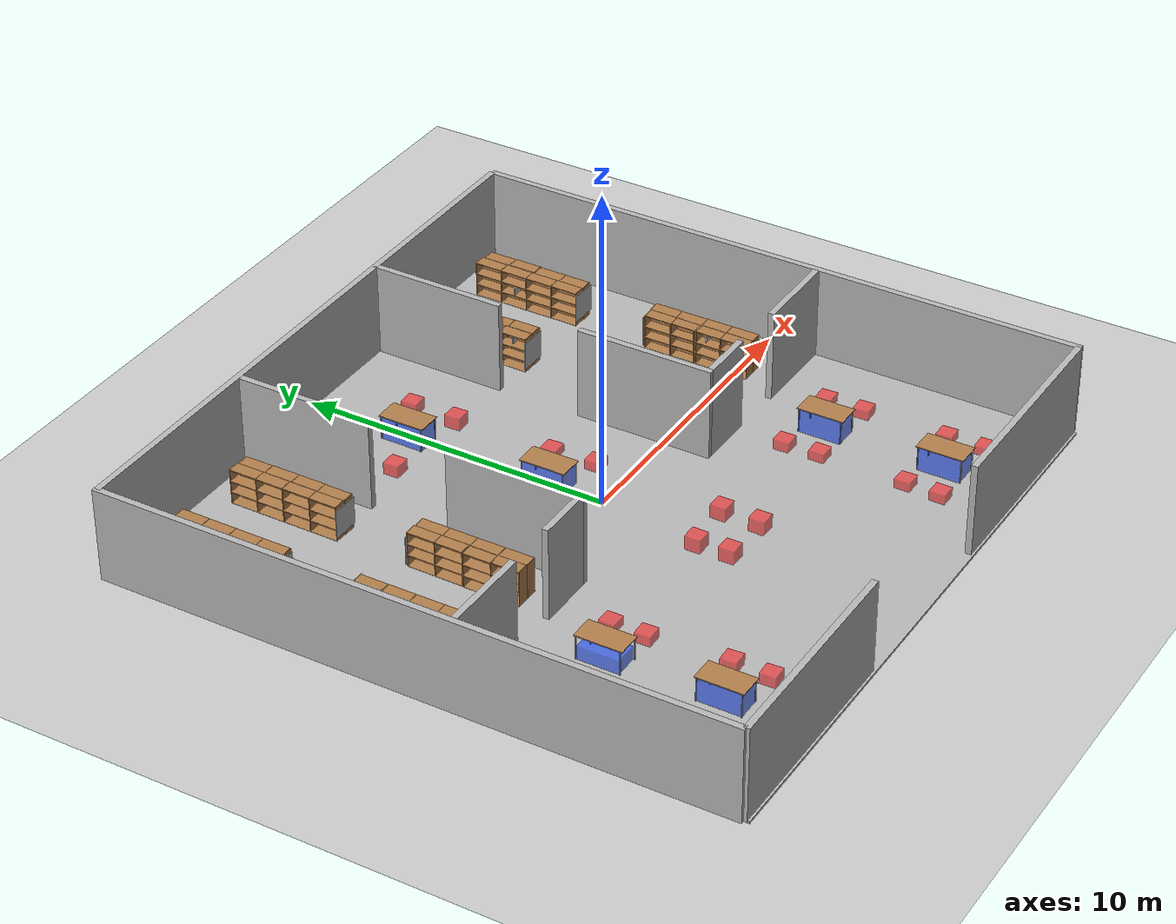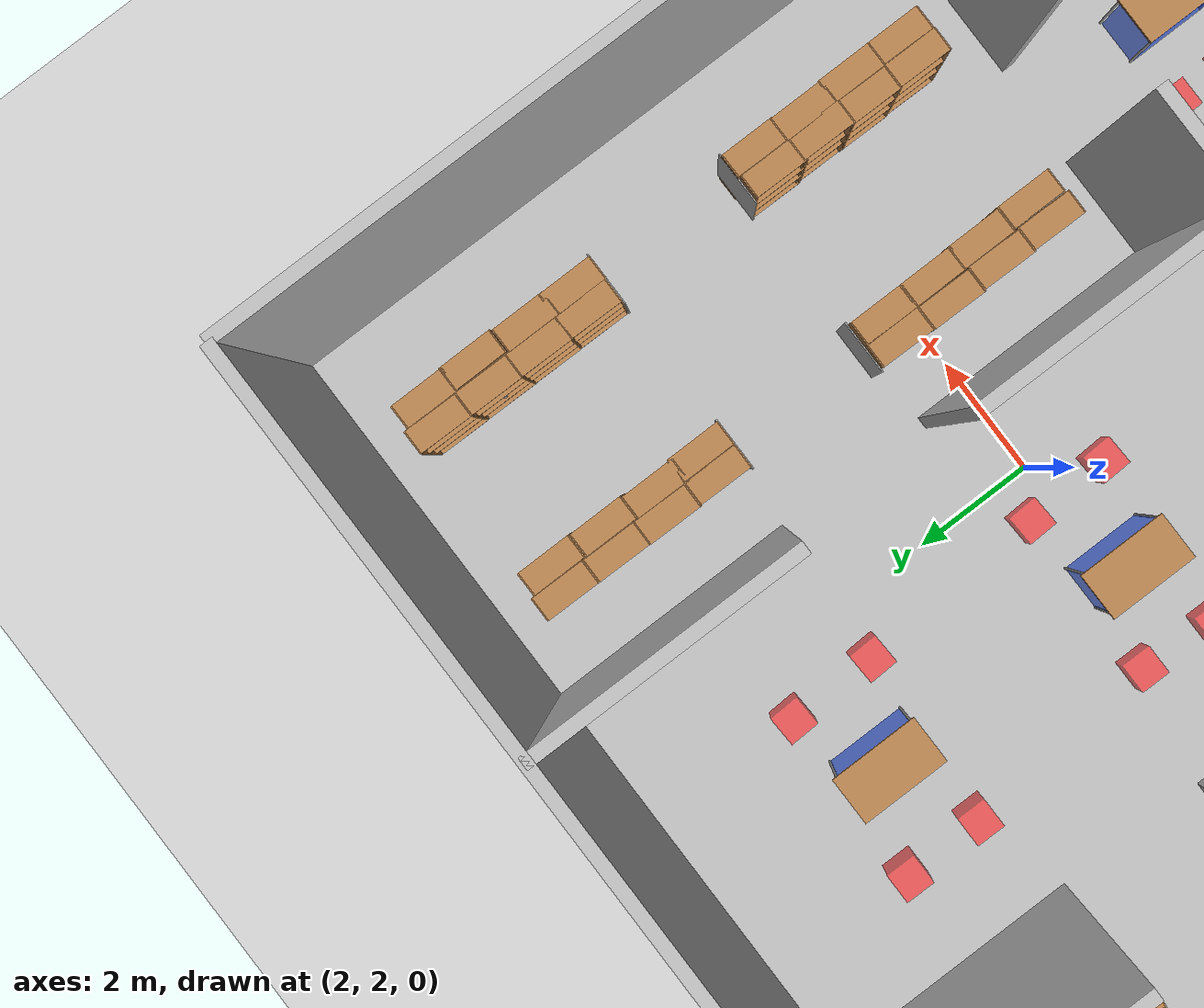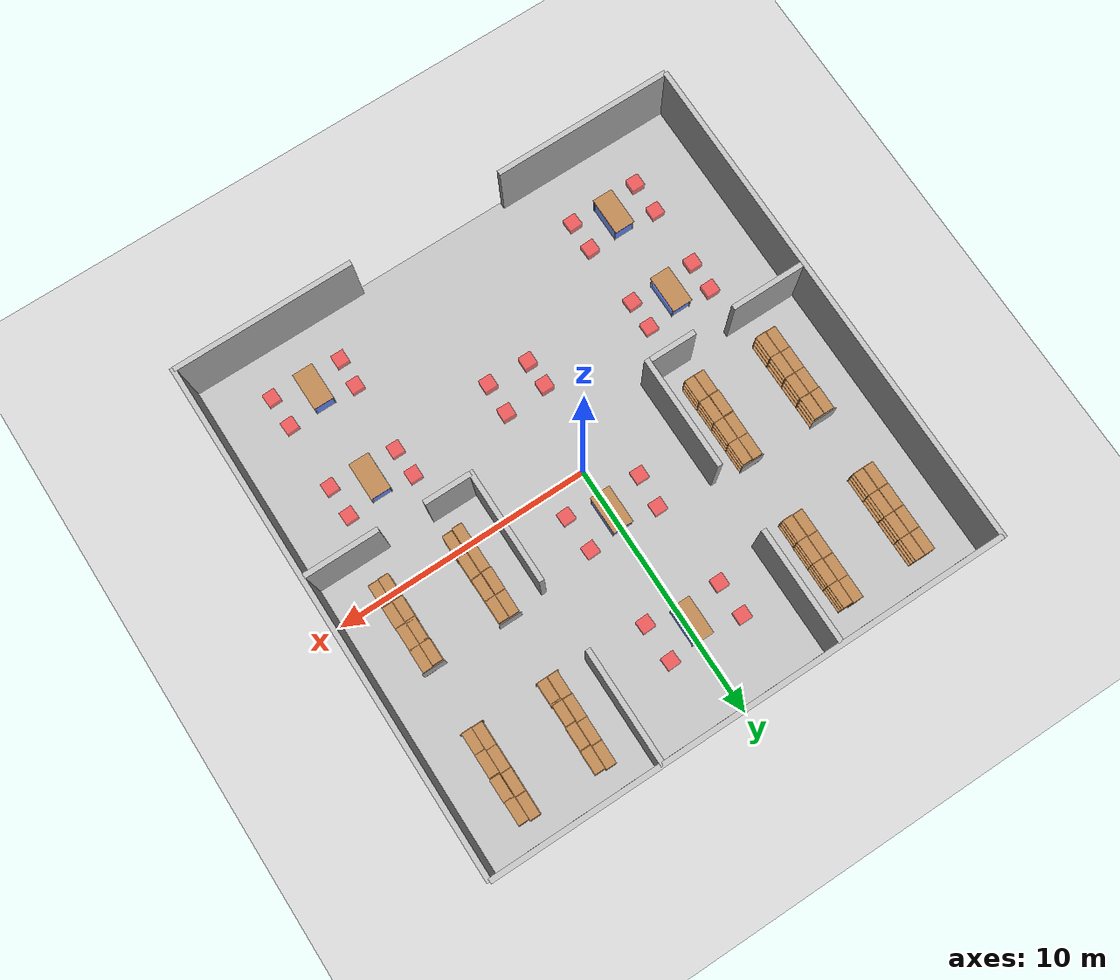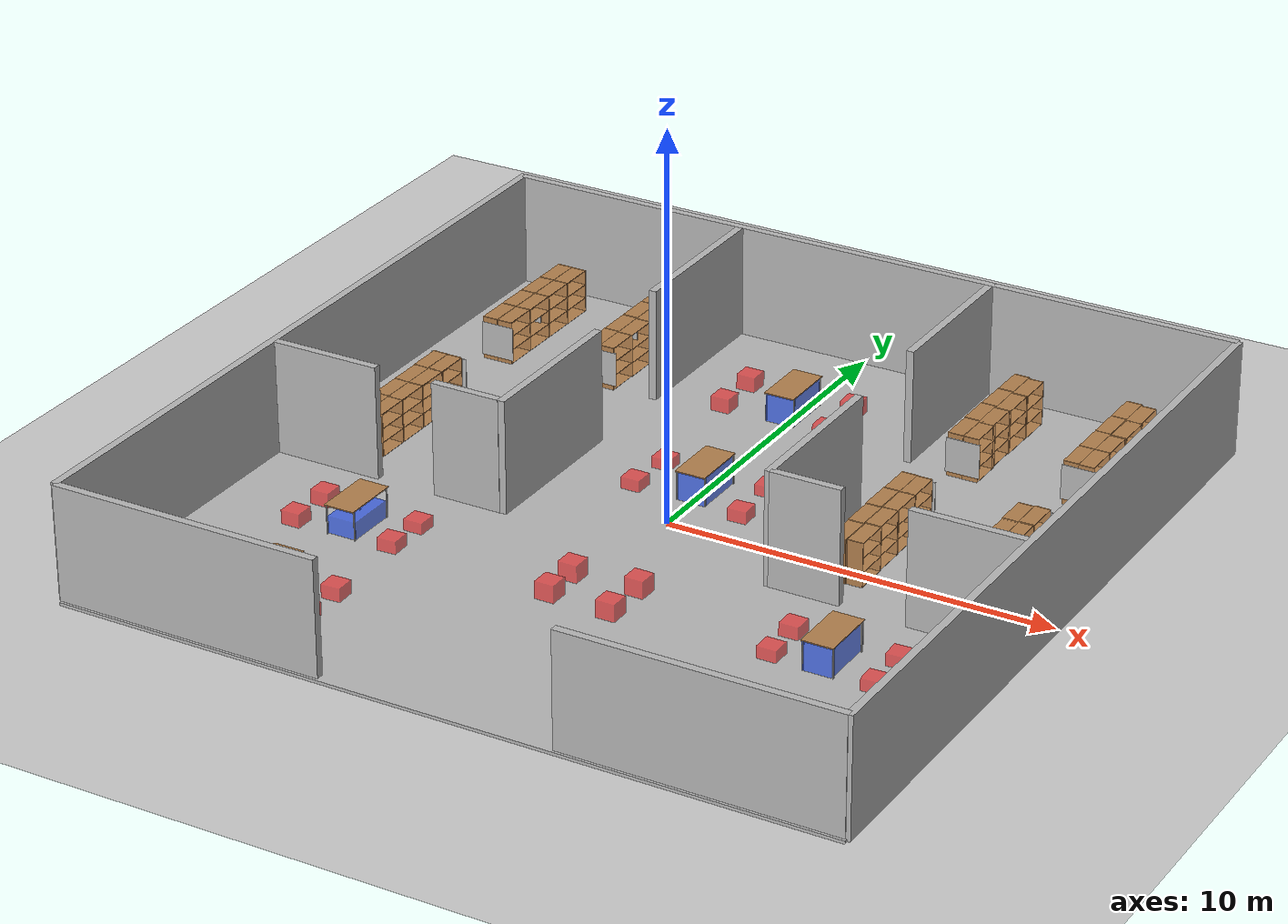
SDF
<sdf version="1.7">
 <world name="library_world">
  <model name="ground_plane">
   <static>1</static>
   <link name="link">
    <collision name="collision">
     <geometry><plane><normal>0 0 1</normal><size>100 100</size></plane></geometry>
     <surface>
      <contact><collide_bitmask>65535</collide_bitmask></contact>
      <friction><ode><mu>100</mu><mu2>50</mu2></ode></friction>
     </surface>
    </collision>
    <visual name="visual">
     <cast_shadows>0</cast_shadows>
     <geometry><plane><normal>0 0 1</normal><size>100 100</size></plane></geometry>
     <material>
      <script><uri>file://media/materials/scripts/gazebo.material</uri><name>Gazebo/Grey</name></script>
     </material>
    </visual>
   </link>
  </model>
  <light name="sun" type="directional">
   <pose>0 0 10 0 -0 0</pose>
   <diffuse>0.8 0.8 0.8 1</diffuse>
   <specular>0.2 0.2 0.2 1</specular>
   <attenuation>
    <range>1000</range>
    <constant>0.9</constant>
    <linear>0.01</linear>
    <quadratic>0.001</quadratic>
   </attenuation>
   <direction>-0.5 0.1 -0.9</direction>
   <spot><inner_angle>0</inner_angle><outer_angle>0</outer_angle><falloff>0</falloff></spot>
  </light>
  <model name="floor">
   <static>1</static>
   <link name="link">
    <collision name="collision"><geometry><box><size>20 20 0.1</size></box></geometry></collision>
    <visual name="visual"><geometry><box><size>20 20 0.1</size></box></geometry></visual>
   </link>
   <pose>0.030291 -0.166177 0 0 -0 0</pose>
  </model>
  <model name="wall_back">
   <static>1</static>
   <link name="link"><visual name="visual"><geometry><box><size>20 0.2 3</size></box></geometry></visual></link>
   <pose>0 9.89894 1.5 0 -0 0</pose>
  </model>
  <model name="wall_left">
   <static>1</static>
   <link name="link"><visual name="visual"><geometry><box><size>0.2 20 3</size></box></geometry></visual></link>
   <pose>-10 0 1.5 0 -0 0</pose>
  </model>
  <model name="wall_right">
   <static>1</static>
   <link name="link"><visual name="visual"><geometry><box><size>0.2 20 3</size></box></geometry></visual></link>
   <pose>10.0092 -0.084031 1.49865 0 -0 0</pose>
  </model>
  <model name="wall_front_left">
   <static>1</static>
   <link name="link"><visual name="visual"><geometry><box><size>7 0.2 3</size></box></geometry></visual></link>
   <pose>-6.5 -10 1.5 0 -0 0</pose>
  </model>
  <model name="wall_front_right">
   <static>1</static>
   <link name="link"><visual name="visual"><geometry><box><size>7 0.2 3</size></box></geometry></visual></link>
   <pose>6.5 -10 1.5 0 -0 0</pose>
  </model>
  <gravity>0 0 -9.8</gravity>
  <magnetic_field>6e-06 2.3e-05 -4.2e-05</magnetic_field>
  <atmosphere type="adiabatic"/>
  <physics type="ode">
   <max_step_size>0.001</max_step_size>
   <real_time_factor>1</real_time_factor>
   <real_time_update_rate>1000</real_time_update_rate>
  </physics>
  <scene><ambient>0.4 0.4 0.4 1</ambient><background>0.7 0.7 0.7 1</background><shadows>1</shadows></scene>
  <spherical_coordinates>
   <surface_model>EARTH_WGS84</surface_model>
   <latitude_deg>0</latitude_deg>
   <longitude_deg>0</longitude_deg>
   <elevation>0</elevation>
   <heading_deg>0</heading_deg>
  </spherical_coordinates>
  <model name="bookshelf_0_clone_2_clone">
   <static>1</static>
   <link name="link">
    <inertial><mass>1</mass></inertial>
    <collision name="back">
     <pose>0 0.005 0.6 0 -0 0</pose>
     <geometry><box><size>0.9 0.01 1.2</size></box></geometry>
    </collision>
    <visual name="visual1">
     <pose>0 0.005 0.6 0 -0 0</pose>
     <geometry><box><size>0.9 0.01 1.2</size></box></geometry>
     <material>
      <script><uri>file://media/materials/scripts/gazebo.material</uri><name>Gazebo/Wood</name></script>
     </material>
    </visual>
    <collision name="left_side">
     <pose>0.45 -0.195 0.6 0 -0 0</pose>
     <geometry><box><size>0.02 0.4 1.2</size></box></geometry>
    </collision>
    <visual name="visual2">
     <pose>0.45 -0.195 0.6 0 -0 0</pose>
     <geometry><box><size>0.02 0.4 1.2</size></box></geometry>
     <material>
      <script><uri>file://media/materials/scripts/gazebo.material</uri><name>Gazebo/Wood</name></script>
     </material>
    </visual>
    <collision name="right_side">
     <pose>-0.45 -0.195 0.6 0 -0 0</pose>
     <geometry><box><size>0.02 0.4 1.2</size></box></geometry>
    </collision>
    <visual name="visual3">
     <pose>-0.45 -0.195 0.6 0 -0 0</pose>
     <geometry><box><size>0.02 0.4 1.2</size></box></geometry>
     <material>
      <script><uri>file://media/materials/scripts/gazebo.material</uri><name>Gazebo/Wood</name></script>
     </material>
    </visual>
    <collision name="bottom">
     <pose>0 -0.195 0.03 0 -0 0</pose>
     <geometry><box><size>0.88 0.4 0.06</size></box></geometry>
    </collision>
    <visual name="visual4">
     <pose>0 -0.195 0.03 0 -0 0</pose>
     <geometry><box><size>0.88 0.4 0.06</size></box></geometry>
     <material>
      <script><uri>file://media/materials/scripts/gazebo.material</uri><name>Gazebo/Wood</name></script>
     </material>
    </visual>
    <collision name="top">
     <pose>0 -0.195 1.19 0 -0 0</pose>
     <geometry><box><size>0.88 0.4 0.02</size></box></geometry>
    </collision>
    <visual name="visual5">
     <pose>0 -0.195 1.19 0 -0 0</pose>
     <geometry><box><size>0.88 0.4 0.02</size></box></geometry>
     <material>
      <script><uri>file://media/materials/scripts/gazebo.material</uri><name>Gazebo/Wood</name></script>
     </material>
    </visual>
    <collision name="low_shelf">
     <pose>0 -0.195 0.43 0 -0 0</pose>
     <geometry><box><size>0.88 0.4 0.02</size></box></geometry>
    </collision>
    <visual name="visual6">
     <pose>0 -0.195 0.43 0 -0 0</pose>
     <geometry><box><size>0.88 0.4 0.02</size></box></geometry>
     <material>
      <script><uri>file://media/materials/scripts/gazebo.material</uri><name>Gazebo/Wood</name></script>
     </material>
    </visual>
    <collision name="high_shelf">
     <pose>0 -0.195 0.8 0 -0 0</pose>
     <geometry><box><size>0.88 0.4 0.02</size></box></geometry>
    </collision>
    <visual name="visual7">
     <pose>0 -0.195 0.8 0 -0 0</pose>
     <geometry><box><size>0.88 0.4 0.02</size></box></geometry>
     <material>
      <script><uri>file://media/materials/scripts/gazebo.material</uri><name>Gazebo/Wood</name></script>
     </material>
    </visual>
   </link>
   <pose>-7.9828 8.52336 0 0 -0 1.57381</pose>
  </model>
  <model name="bookshelf_0_clone_2_clone_0">
   <static>1</static>
   <link name="link">
    <inertial><mass>1</mass></inertial>
    <collision name="back">
     <pose>0 0.005 0.6 0 -0 0</pose>
     <geometry><box><size>0.9 0.01 1.2</size></box></geometry>
    </collision>
    <visual name="visual1">
     <pose>0 0.005 0.6 0 -0 0</pose>
     <geometry><box><size>0.9 0.01 1.2</size></box></geometry>
     <material>
      <script><uri>file://media/materials/scripts/gazebo.material</uri><name>Gazebo/Wood</name></script>
     </material>
    </visual>
    <collision name="left_side">
     <pose>0.45 -0.195 0.6 0 -0 0</pose>
     <geometry><box><size>0.02 0.4 1.2</size></box></geometry>
    </collision>
    <visual name="visual2">
     <pose>0.45 -0.195 0.6 0 -0 0</pose>
     <geometry><box><size>0.02 0.4 1.2</size></box></geometry>
     <material>
      <script><uri>file://media/materials/scripts/gazebo.material</uri><name>Gazebo/Wood</name></script>
     </material>
    </visual>
    <collision name="right_side">
     <pose>-0.45 -0.195 0.6 0 -0 0</pose>
     <geometry><box><size>0.02 0.4 1.2</size></box></geometry>
    </collision>
    <visual name="visual3">
     <pose>-0.45 -0.195 0.6 0 -0 0</pose>
     <geometry><box><size>0.02 0.4 1.2</size></box></geometry>
     <material>
      <script><uri>file://media/materials/scripts/gazebo.material</uri><name>Gazebo/Wood</name></script>
     </material>
    </visual>
    <collision name="bottom">
     <pose>0 -0.195 0.03 0 -0 0</pose>
     <geometry><box><size>0.88 0.4 0.06</size></box></geometry>
    </collision>
    <visual name="visual4">
     <pose>0 -0.195 0.03 0 -0 0</pose>
     <geometry><box><size>0.88 0.4 0.06</size></box></geometry>
     <material>
      <script><uri>file://media/materials/scripts/gazebo.material</uri><name>Gazebo/Wood</name></script>
     </material>
    </visual>
    <collision name="top">
     <pose>0 -0.195 1.19 0 -0 0</pose>
     <geometry><box><size>0.88 0.4 0.02</size></box></geometry>
    </collision>
    <visual name="visual5">
     <pose>0 -0.195 1.19 0 -0 0</pose>
     <geometry><box><size>0.88 0.4 0.02</size></box></geometry>
     <material>
      <script><uri>file://media/materials/scripts/gazebo.material</uri><name>Gazebo/Wood</name></script>
     </material>
    </visual>
    <collision name="low_shelf">
     <pose>0 -0.195 0.43 0 -0 0</pose>
     <geometry><box><size>0.88 0.4 0.02</size></box></geometry>
    </collision>
    <visual name="visual6">
     <pose>0 -0.195 0.43 0 -0 0</pose>
     <geometry><box><size>0.88 0.4 0.02</size></box></geometry>
     <material>
      <script><uri>file://media/materials/scripts/gazebo.material</uri><name>Gazebo/Wood</name></script>
     </material>
    </visual>
    <collision name="high_shelf">
     <pose>0 -0.195 0.8 0 -0 0</pose>
     <geometry><box><size>0.88 0.4 0.02</size></box></geometry>
    </collision>
    <visual name="visual7">
     <pose>0 -0.195 0.8 0 -0 0</pose>
     <geometry><box><size>0.88 0.4 0.02</size></box></geometry>
     <material>
      <script><uri>file://media/materials/scripts/gazebo.material</uri><name>Gazebo/Wood</name></script>
     </material>
    </visual>
   </link>
   <pose>-7.9819 7.61403 0 0 -0 1.57381</pose>
  </model>
  <model name="bookshelf_0_clone_2_clone_1">
   <static>1</static>
   <link name="link">
    <inertial><mass>1</mass></inertial>
    <collision name="back">
     <pose>0 0.005 0.6 0 -0 0</pose>
     <geometry><box><size>0.9 0.01 1.2</size></box></geometry>
    </collision>
    <visual name="visual1">
     <pose>0 0.005 0.6 0 -0 0</pose>
     <geometry><box><size>0.9 0.01 1.2</size></box></geometry>
     <material>
      <script><uri>file://media/materials/scripts/gazebo.material</uri><name>Gazebo/Wood</name></script>
     </material>
    </visual>
    <collision name="left_side">
     <pose>0.45 -0.195 0.6 0 -0 0</pose>
     <geometry><box><size>0.02 0.4 1.2</size></box></geometry>
    </collision>
    <visual name="visual2">
     <pose>0.45 -0.195 0.6 0 -0 0</pose>
     <geometry><box><size>0.02 0.4 1.2</size></box></geometry>
     <material>
      <script><uri>file://media/materials/scripts/gazebo.material</uri><name>Gazebo/Wood</name></script>
     </material>
    </visual>
    <collision name="right_side">
     <pose>-0.45 -0.195 0.6 0 -0 0</pose>
     <geometry><box><size>0.02 0.4 1.2</size></box></geometry>
    </collision>
    <visual name="visual3">
     <pose>-0.45 -0.195 0.6 0 -0 0</pose>
     <geometry><box><size>0.02 0.4 1.2</size></box></geometry>
     <material>
      <script><uri>file://media/materials/scripts/gazebo.material</uri><name>Gazebo/Wood</name></script>
     </material>
    </visual>
    <collision name="bottom">
     <pose>0 -0.195 0.03 0 -0 0</pose>
     <geometry><box><size>0.88 0.4 0.06</size></box></geometry>
    </collision>
    <visual name="visual4">
     <pose>0 -0.195 0.03 0 -0 0</pose>
     <geometry><box><size>0.88 0.4 0.06</size></box></geometry>
     <material>
      <script><uri>file://media/materials/scripts/gazebo.material</uri><name>Gazebo/Wood</name></script>
     </material>
    </visual>
    <collision name="top">
     <pose>0 -0.195 1.19 0 -0 0</pose>
     <geometry><box><size>0.88 0.4 0.02</size></box></geometry>
    </collision>
    <visual name="visual5">
     <pose>0 -0.195 1.19 0 -0 0</pose>
     <geometry><box><size>0.88 0.4 0.02</size></box></geometry>
     <material>
      <script><uri>file://media/materials/scripts/gazebo.material</uri><name>Gazebo/Wood</name></script>
     </material>
    </visual>
    <collision name="low_shelf">
     <pose>0 -0.195 0.43 0 -0 0</pose>
     <geometry><box><size>0.88 0.4 0.02</size></box></geometry>
    </collision>
    <visual name="visual6">
     <pose>0 -0.195 0.43 0 -0 0</pose>
     <geometry><box><size>0.88 0.4 0.02</size></box></geometry>
     <material>
      <script><uri>file://media/materials/scripts/gazebo.material</uri><name>Gazebo/Wood</name></script>
     </material>
    </visual>
    <collision name="high_shelf">
     <pose>0 -0.195 0.8 0 -0 0</pose>
     <geometry><box><size>0.88 0.4 0.02</size></box></geometry>
    </collision>
    <visual name="visual7">
     <pose>0 -0.195 0.8 0 -0 0</pose>
     <geometry><box><size>0.88 0.4 0.02</size></box></geometry>
     <material>
      <script><uri>file://media/materials/scripts/gazebo.material</uri><name>Gazebo/Wood</name></script>
     </material>
    </visual>
   </link>
   <pose>-7.98238 6.70319 0 0 -0 1.57381</pose>
  </model>
  <model name="bookshelf_0_clone_2_clone_2">
   <static>1</static>
   <link name="link">
    <inertial><mass>1</mass></inertial>
    <collision name="back">
     <pose>0 0.005 0.6 0 -0 0</pose>
     <geometry><box><size>0.9 0.01 1.2</size></box></geometry>
    </collision>
    <visual name="visual1">
     <pose>0 0.005 0.6 0 -0 0</pose>
     <geometry><box><size>0.9 0.01 1.2</size></box></geometry>
     <material>
      <script><uri>file://media/materials/scripts/gazebo.material</uri><name>Gazebo/Wood</name></script>
     </material>
    </visual>
    <collision name="left_side">
     <pose>0.45 -0.195 0.6 0 -0 0</pose>
     <geometry><box><size>0.02 0.4 1.2</size></box></geometry>
    </collision>
    <visual name="visual2">
     <pose>0.45 -0.195 0.6 0 -0 0</pose>
     <geometry><box><size>0.02 0.4 1.2</size></box></geometry>
     <material>
      <script><uri>file://media/materials/scripts/gazebo.material</uri><name>Gazebo/Wood</name></script>
     </material>
    </visual>
    <collision name="right_side">
     <pose>-0.45 -0.195 0.6 0 -0 0</pose>
     <geometry><box><size>0.02 0.4 1.2</size></box></geometry>
    </collision>
    <visual name="visual3">
     <pose>-0.45 -0.195 0.6 0 -0 0</pose>
     <geometry><box><size>0.02 0.4 1.2</size></box></geometry>
     <material>
      <script><uri>file://media/materials/scripts/gazebo.material</uri><name>Gazebo/Wood</name></script>
     </material>
    </visual>
    <collision name="bottom">
     <pose>0 -0.195 0.03 0 -0 0</pose>
     <geometry><box><size>0.88 0.4 0.06</size></box></geometry>
    </collision>
    <visual name="visual4">
     <pose>0 -0.195 0.03 0 -0 0</pose>
     <geometry><box><size>0.88 0.4 0.06</size></box></geometry>
     <material>
      <script><uri>file://media/materials/scripts/gazebo.material</uri><name>Gazebo/Wood</name></script>
     </material>
    </visual>
    <collision name="top">
     <pose>0 -0.195 1.19 0 -0 0</pose>
     <geometry><box><size>0.88 0.4 0.02</size></box></geometry>
    </collision>
    <visual name="visual5">
     <pose>0 -0.195 1.19 0 -0 0</pose>
     <geometry><box><size>0.88 0.4 0.02</size></box></geometry>
     <material>
      <script><uri>file://media/materials/scripts/gazebo.material</uri><name>Gazebo/Wood</name></script>
     </material>
    </visual>
    <collision name="low_shelf">
     <pose>0 -0.195 0.43 0 -0 0</pose>
     <geometry><box><size>0.88 0.4 0.02</size></box></geometry>
    </collision>
    <visual name="visual6">
     <pose>0 -0.195 0.43 0 -0 0</pose>
     <geometry><box><size>0.88 0.4 0.02</size></box></geometry>
     <material>
      <script><uri>file://media/materials/scripts/gazebo.material</uri><name>Gazebo/Wood</name></script>
     </material>
    </visual>
    <collision name="high_shelf">
     <pose>0 -0.195 0.8 0 -0 0</pose>
     <geometry><box><size>0.88 0.4 0.02</size></box></geometry>
    </collision>
    <visual name="visual7">
     <pose>0 -0.195 0.8 0 -0 0</pose>
     <geometry><box><size>0.88 0.4 0.02</size></box></geometry>
     <material>
      <script><uri>file://media/materials/scripts/gazebo.material</uri><name>Gazebo/Wood</name></script>
     </material>
    </visual>
   </link>
   <pose>-7.9838 5.79924 0 0 -0 1.57381</pose>
  </model>
  <model name="bookshelf_0_clone_8_clone">
   <static>1</static>
   <link name="link">
    <inertial><mass>1</mass></inertial>
    <collision name="back">
     <pose>0 0.005 0.6 0 -0 0</pose>
     <geometry><box><size>0.9 0.01 1.2</size></box></geometry>
    </collision>
    <visual name="visual1">
     <pose>0 0.005 0.6 0 -0 0</pose>
     <geometry><box><size>0.9 0.01 1.2</size></box></geometry>
     <material>
      <script><uri>file://media/materials/scripts/gazebo.material</uri><name>Gazebo/Wood</name></script>
     </material>
    </visual>
    <collision name="left_side">
     <pose>0.45 -0.195 0.6 0 -0 0</pose>
     <geometry><box><size>0.02 0.4 1.2</size></box></geometry>
    </collision>
    <visual name="visual2">
     <pose>0.45 -0.195 0.6 0 -0 0</pose>
     <geometry><box><size>0.02 0.4 1.2</size></box></geometry>
     <material>
      <script><uri>file://media/materials/scripts/gazebo.material</uri><name>Gazebo/Wood</name></script>
     </material>
    </visual>
    <collision name="right_side">
     <pose>-0.45 -0.195 0.6 0 -0 0</pose>
     <geometry><box><size>0.02 0.4 1.2</size></box></geometry>
    </collision>
    <visual name="visual3">
     <pose>-0.45 -0.195 0.6 0 -0 0</pose>
     <geometry><box><size>0.02 0.4 1.2</size></box></geometry>
     <material>
      <script><uri>file://media/materials/scripts/gazebo.material</uri><name>Gazebo/Wood</name></script>
     </material>
    </visual>
    <collision name="bottom">
     <pose>0 -0.195 0.03 0 -0 0</pose>
     <geometry><box><size>0.88 0.4 0.06</size></box></geometry>
    </collision>
    <visual name="visual4">
     <pose>0 -0.195 0.03 0 -0 0</pose>
     <geometry><box><size>0.88 0.4 0.06</size></box></geometry>
     <material>
      <script><uri>file://media/materials/scripts/gazebo.material</uri><name>Gazebo/Wood</name></script>
     </material>
    </visual>
    <collision name="top">
     <pose>0 -0.195 1.19 0 -0 0</pose>
     <geometry><box><size>0.88 0.4 0.02</size></box></geometry>
    </collision>
    <visual name="visual5">
     <pose>0 -0.195 1.19 0 -0 0</pose>
     <geometry><box><size>0.88 0.4 0.02</size></box></geometry>
     <material>
      <script><uri>file://media/materials/scripts/gazebo.material</uri><name>Gazebo/Wood</name></script>
     </material>
    </visual>
    <collision name="low_shelf">
     <pose>0 -0.195 0.43 0 -0 0</pose>
     <geometry><box><size>0.88 0.4 0.02</size></box></geometry>
    </collision>
    <visual name="visual6">
     <pose>0 -0.195 0.43 0 -0 0</pose>
     <geometry><box><size>0.88 0.4 0.02</size></box></geometry>
     <material>
      <script><uri>file://media/materials/scripts/gazebo.material</uri><name>Gazebo/Wood</name></script>
     </material>
    </visual>
    <collision name="high_shelf">
     <pose>0 -0.195 0.8 0 -0 0</pose>
     <geometry><box><size>0.88 0.4 0.02</size></box></geometry>
    </collision>
    <visual name="visual7">
     <pose>0 -0.195 0.8 0 -0 0</pose>
     <geometry><box><size>0.88 0.4 0.02</size></box></geometry>
     <material>
      <script><uri>file://media/materials/scripts/gazebo.material</uri><name>Gazebo/Wood</name></script>
     </material>
    </visual>
   </link>
   <pose>-8.00188 8.53017 0 0 0 -1.57537</pose>
  </model>
  <model name="bookshelf_0_clone_8_clone_0">
   <static>1</static>
   <link name="link">
    <inertial><mass>1</mass></inertial>
    <collision name="back">
     <pose>0 0.005 0.6 0 -0 0</pose>
     <geometry><box><size>0.9 0.01 1.2</size></box></geometry>
    </collision>
    <visual name="visual1">
     <pose>0 0.005 0.6 0 -0 0</pose>
     <geometry><box><size>0.9 0.01 1.2</size></box></geometry>
     <material>
      <script><uri>file://media/materials/scripts/gazebo.material</uri><name>Gazebo/Wood</name></script>
     </material>
    </visual>
    <collision name="left_side">
     <pose>0.45 -0.195 0.6 0 -0 0</pose>
     <geometry><box><size>0.02 0.4 1.2</size></box></geometry>
    </collision>
    <visual name="visual2">
     <pose>0.45 -0.195 0.6 0 -0 0</pose>
     <geometry><box><size>0.02 0.4 1.2</size></box></geometry>
     <material>
      <script><uri>file://media/materials/scripts/gazebo.material</uri><name>Gazebo/Wood</name></script>
     </material>
    </visual>
    <collision name="right_side">
     <pose>-0.45 -0.195 0.6 0 -0 0</pose>
     <geometry><box><size>0.02 0.4 1.2</size></box></geometry>
    </collision>
    <visual name="visual3">
     <pose>-0.45 -0.195 0.6 0 -0 0</pose>
     <geometry><box><size>0.02 0.4 1.2</size></box></geometry>
     <material>
      <script><uri>file://media/materials/scripts/gazebo.material</uri><name>Gazebo/Wood</name></script>
     </material>
    </visual>
    <collision name="bottom">
     <pose>0 -0.195 0.03 0 -0 0</pose>
     <geometry><box><size>0.88 0.4 0.06</size></box></geometry>
    </collision>
    <visual name="visual4">
     <pose>0 -0.195 0.03 0 -0 0</pose>
     <geometry><box><size>0.88 0.4 0.06</size></box></geometry>
     <material>
      <script><uri>file://media/materials/scripts/gazebo.material</uri><name>Gazebo/Wood</name></script>
     </material>
    </visual>
    <collision name="top">
     <pose>0 -0.195 1.19 0 -0 0</pose>
     <geometry><box><size>0.88 0.4 0.02</size></box></geometry>
    </collision>
    <visual name="visual5">
     <pose>0 -0.195 1.19 0 -0 0</pose>
     <geometry><box><size>0.88 0.4 0.02</size></box></geometry>
     <material>
      <script><uri>file://media/materials/scripts/gazebo.material</uri><name>Gazebo/Wood</name></script>
     </material>
    </visual>
    <collision name="low_shelf">
     <pose>0 -0.195 0.43 0 -0 0</pose>
     <geometry><box><size>0.88 0.4 0.02</size></box></geometry>
    </collision>
    <visual name="visual6">
     <pose>0 -0.195 0.43 0 -0 0</pose>
     <geometry><box><size>0.88 0.4 0.02</size></box></geometry>
     <material>
      <script><uri>file://media/materials/scripts/gazebo.material</uri><name>Gazebo/Wood</name></script>
     </material>
    </visual>
    <collision name="high_shelf">
     <pose>0 -0.195 0.8 0 -0 0</pose>
     <geometry><box><size>0.88 0.4 0.02</size></box></geometry>
    </collision>
    <visual name="visual7">
     <pose>0 -0.195 0.8 0 -0 0</pose>
     <geometry><box><size>0.88 0.4 0.02</size></box></geometry>
     <material>
      <script><uri>file://media/materials/scripts/gazebo.material</uri><name>Gazebo/Wood</name></script>
     </material>
    </visual>
   </link>
   <pose>-8.00429 7.61626 0 0 0 -1.57537</pose>
  </model>
  <model name="bookshelf_0_clone_8_clone_1">
   <static>1</static>
   <link name="link">
    <inertial><mass>1</mass></inertial>
    <collision name="back">
     <pose>0 0.005 0.6 0 -0 0</pose>
     <geometry><box><size>0.9 0.01 1.2</size></box></geometry>
    </collision>
    <visual name="visual1">
     <pose>0 0.005 0.6 0 -0 0</pose>
     <geometry><box><size>0.9 0.01 1.2</size></box></geometry>
     <material>
      <script><uri>file://media/materials/scripts/gazebo.material</uri><name>Gazebo/Wood</name></script>
     </material>
    </visual>
    <collision name="left_side">
     <pose>0.45 -0.195 0.6 0 -0 0</pose>
     <geometry><box><size>0.02 0.4 1.2</size></box></geometry>
    </collision>
    <visual name="visual2">
     <pose>0.45 -0.195 0.6 0 -0 0</pose>
     <geometry><box><size>0.02 0.4 1.2</size></box></geometry>
     <material>
      <script><uri>file://media/materials/scripts/gazebo.material</uri><name>Gazebo/Wood</name></script>
     </material>
    </visual>
    <collision name="right_side">
     <pose>-0.45 -0.195 0.6 0 -0 0</pose>
     <geometry><box><size>0.02 0.4 1.2</size></box></geometry>
    </collision>
    <visual name="visual3">
     <pose>-0.45 -0.195 0.6 0 -0 0</pose>
     <geometry><box><size>0.02 0.4 1.2</size></box></geometry>
     <material>
      <script><uri>file://media/materials/scripts/gazebo.material</uri><name>Gazebo/Wood</name></script>
     </material>
    </visual>
    <collision name="bottom">
     <pose>0 -0.195 0.03 0 -0 0</pose>
     <geometry><box><size>0.88 0.4 0.06</size></box></geometry>
    </collision>
    <visual name="visual4">
     <pose>0 -0.195 0.03 0 -0 0</pose>
     <geometry><box><size>0.88 0.4 0.06</size></box></geometry>
     <material>
      <script><uri>file://media/materials/scripts/gazebo.material</uri><name>Gazebo/Wood</name></script>
     </material>
    </visual>
    <collision name="top">
     <pose>0 -0.195 1.19 0 -0 0</pose>
     <geometry><box><size>0.88 0.4 0.02</size></box></geometry>
    </collision>
    <visual name="visual5">
     <pose>0 -0.195 1.19 0 -0 0</pose>
     <geometry><box><size>0.88 0.4 0.02</size></box></geometry>
     <material>
      <script><uri>file://media/materials/scripts/gazebo.material</uri><name>Gazebo/Wood</name></script>
     </material>
    </visual>
    <collision name="low_shelf">
     <pose>0 -0.195 0.43 0 -0 0</pose>
     <geometry><box><size>0.88 0.4 0.02</size></box></geometry>
    </collision>
    <visual name="visual6">
     <pose>0 -0.195 0.43 0 -0 0</pose>
     <geometry><box><size>0.88 0.4 0.02</size></box></geometry>
     <material>
      <script><uri>file://media/materials/scripts/gazebo.material</uri><name>Gazebo/Wood</name></script>
     </material>
    </visual>
    <collision name="high_shelf">
     <pose>0 -0.195 0.8 0 -0 0</pose>
     <geometry><box><size>0.88 0.4 0.02</size></box></geometry>
    </collision>
    <visual name="visual7">
     <pose>0 -0.195 0.8 0 -0 0</pose>
     <geometry><box><size>0.88 0.4 0.02</size></box></geometry>
     <material>
      <script><uri>file://media/materials/scripts/gazebo.material</uri><name>Gazebo/Wood</name></script>
     </material>
    </visual>
   </link>
   <pose>-8.00535 6.7085 0 0 0 -1.57537</pose>
  </model>
  <model name="bookshelf_0_clone_8_clone_2">
   <static>1</static>
   <link name="link">
    <inertial><mass>1</mass></inertial>
    <collision name="back">
     <pose>0 0.005 0.6 0 -0 0</pose>
     <geometry><box><size>0.9 0.01 1.2</size></box></geometry>
    </collision>
    <visual name="visual1">
     <pose>0 0.005 0.6 0 -0 0</pose>
     <geometry><box><size>0.9 0.01 1.2</size></box></geometry>
     <material>
      <script><uri>file://media/materials/scripts/gazebo.material</uri><name>Gazebo/Wood</name></script>
     </material>
    </visual>
    <collision name="left_side">
     <pose>0.45 -0.195 0.6 0 -0 0</pose>
     <geometry><box><size>0.02 0.4 1.2</size></box></geometry>
    </collision>
    <visual name="visual2">
     <pose>0.45 -0.195 0.6 0 -0 0</pose>
     <geometry><box><size>0.02 0.4 1.2</size></box></geometry>
     <material>
      <script><uri>file://media/materials/scripts/gazebo.material</uri><name>Gazebo/Wood</name></script>
     </material>
    </visual>
    <collision name="right_side">
     <pose>-0.45 -0.195 0.6 0 -0 0</pose>
     <geometry><box><size>0.02 0.4 1.2</size></box></geometry>
    </collision>
    <visual name="visual3">
     <pose>-0.45 -0.195 0.6 0 -0 0</pose>
     <geometry><box><size>0.02 0.4 1.2</size></box></geometry>
     <material>
      <script><uri>file://media/materials/scripts/gazebo.material</uri><name>Gazebo/Wood</name></script>
     </material>
    </visual>
    <collision name="bottom">
     <pose>0 -0.195 0.03 0 -0 0</pose>
     <geometry><box><size>0.88 0.4 0.06</size></box></geometry>
    </collision>
    <visual name="visual4">
     <pose>0 -0.195 0.03 0 -0 0</pose>
     <geometry><box><size>0.88 0.4 0.06</size></box></geometry>
     <material>
      <script><uri>file://media/materials/scripts/gazebo.material</uri><name>Gazebo/Wood</name></script>
     </material>
    </visual>
    <collision name="top">
     <pose>0 -0.195 1.19 0 -0 0</pose>
     <geometry><box><size>0.88 0.4 0.02</size></box></geometry>
    </collision>
    <visual name="visual5">
     <pose>0 -0.195 1.19 0 -0 0</pose>
     <geometry><box><size>0.88 0.4 0.02</size></box></geometry>
     <material>
      <script><uri>file://media/materials/scripts/gazebo.material</uri><name>Gazebo/Wood</name></script>
     </material>
    </visual>
    <collision name="low_shelf">
     <pose>0 -0.195 0.43 0 -0 0</pose>
     <geometry><box><size>0.88 0.4 0.02</size></box></geometry>
    </collision>
    <visual name="visual6">
     <pose>0 -0.195 0.43 0 -0 0</pose>
     <geometry><box><size>0.88 0.4 0.02</size></box></geometry>
     <material>
      <script><uri>file://media/materials/scripts/gazebo.material</uri><name>Gazebo/Wood</name></script>
     </material>
    </visual>
    <collision name="high_shelf">
     <pose>0 -0.195 0.8 0 -0 0</pose>
     <geometry><box><size>0.88 0.4 0.02</size></box></geometry>
    </collision>
    <visual name="visual7">
     <pose>0 -0.195 0.8 0 -0 0</pose>
     <geometry><box><size>0.88 0.4 0.02</size></box></geometry>
     <material>
      <script><uri>file://media/materials/scripts/gazebo.material</uri><name>Gazebo/Wood</name></script>
     </material>
    </visual>
   </link>
   <pose>-8.00488 5.79635 0 0 0 -1.57537</pose>
  </model>
  <model name="bookshelf_0_clone_8_clone_4">
   <static>1</static>
   <link name="link">
    <inertial><mass>1</mass></inertial>
    <collision name="back">
     <pose>0 0.005 0.6 0 -0 0</pose>
     <geometry><box><size>0.9 0.01 1.2</size></box></geometry>
    </collision>
    <visual name="visual1">
     <pose>0 0.005 0.6 0 -0 0</pose>
     <geometry><box><size>0.9 0.01 1.2</size></box></geometry>
     <material>
      <script><uri>file://media/materials/scripts/gazebo.material</uri><name>Gazebo/Wood</name></script>
     </material>
    </visual>
    <collision name="left_side">
     <pose>0.45 -0.195 0.6 0 -0 0</pose>
     <geometry><box><size>0.02 0.4 1.2</size></box></geometry>
    </collision>
    <visual name="visual2">
     <pose>0.45 -0.195 0.6 0 -0 0</pose>
     <geometry><box><size>0.02 0.4 1.2</size></box></geometry>
     <material>
      <script><uri>file://media/materials/scripts/gazebo.material</uri><name>Gazebo/Wood</name></script>
     </material>
    </visual>
    <collision name="right_side">
     <pose>-0.45 -0.195 0.6 0 -0 0</pose>
     <geometry><box><size>0.02 0.4 1.2</size></box></geometry>
    </collision>
    <visual name="visual3">
     <pose>-0.45 -0.195 0.6 0 -0 0</pose>
     <geometry><box><size>0.02 0.4 1.2</size></box></geometry>
     <material>
      <script><uri>file://media/materials/scripts/gazebo.material</uri><name>Gazebo/Wood</name></script>
     </material>
    </visual>
    <collision name="bottom">
     <pose>0 -0.195 0.03 0 -0 0</pose>
     <geometry><box><size>0.88 0.4 0.06</size></box></geometry>
    </collision>
    <visual name="visual4">
     <pose>0 -0.195 0.03 0 -0 0</pose>
     <geometry><box><size>0.88 0.4 0.06</size></box></geometry>
     <material>
      <script><uri>file://media/materials/scripts/gazebo.material</uri><name>Gazebo/Wood</name></script>
     </material>
    </visual>
    <collision name="top">
     <pose>0 -0.195 1.19 0 -0 0</pose>
     <geometry><box><size>0.88 0.4 0.02</size></box></geometry>
    </collision>
    <visual name="visual5">
     <pose>0 -0.195 1.19 0 -0 0</pose>
     <geometry><box><size>0.88 0.4 0.02</size></box></geometry>
     <material>
      <script><uri>file://media/materials/scripts/gazebo.material</uri><name>Gazebo/Wood</name></script>
     </material>
    </visual>
    <collision name="low_shelf">
     <pose>0 -0.195 0.43 0 -0 0</pose>
     <geometry><box><size>0.88 0.4 0.02</size></box></geometry>
    </collision>
    <visual name="visual6">
     <pose>0 -0.195 0.43 0 -0 0</pose>
     <geometry><box><size>0.88 0.4 0.02</size></box></geometry>
     <material>
      <script><uri>file://media/materials/scripts/gazebo.material</uri><name>Gazebo/Wood</name></script>
     </material>
    </visual>
    <collision name="high_shelf">
     <pose>0 -0.195 0.8 0 -0 0</pose>
     <geometry><box><size>0.88 0.4 0.02</size></box></geometry>
    </collision>
    <visual name="visual7">
     <pose>0 -0.195 0.8 0 -0 0</pose>
     <geometry><box><size>0.88 0.4 0.02</size></box></geometry>
     <material>
      <script><uri>file://media/materials/scripts/gazebo.material</uri><name>Gazebo/Wood</name></script>
     </material>
    </visual>
   </link>
   <pose>-5.00485 8.53788 0 0 0 -1.57537</pose>
  </model>
  <model name="bookshelf_0_clone_8_clone_5">
   <static>1</static>
   <link name="link">
    <inertial><mass>1</mass></inertial>
    <collision name="back">
     <pose>0 0.005 0.6 0 -0 0</pose>
     <geometry><box><size>0.9 0.01 1.2</size></box></geometry>
    </collision>
    <visual name="visual1">
     <pose>0 0.005 0.6 0 -0 0</pose>
     <geometry><box><size>0.9 0.01 1.2</size></box></geometry>
     <material>
      <script><uri>file://media/materials/scripts/gazebo.material</uri><name>Gazebo/Wood</name></script>
     </material>
    </visual>
    <collision name="left_side">
     <pose>0.45 -0.195 0.6 0 -0 0</pose>
     <geometry><box><size>0.02 0.4 1.2</size></box></geometry>
    </collision>
    <visual name="visual2">
     <pose>0.45 -0.195 0.6 0 -0 0</pose>
     <geometry><box><size>0.02 0.4 1.2</size></box></geometry>
     <material>
      <script><uri>file://media/materials/scripts/gazebo.material</uri><name>Gazebo/Wood</name></script>
     </material>
    </visual>
    <collision name="right_side">
     <pose>-0.45 -0.195 0.6 0 -0 0</pose>
     <geometry><box><size>0.02 0.4 1.2</size></box></geometry>
    </collision>
    <visual name="visual3">
     <pose>-0.45 -0.195 0.6 0 -0 0</pose>
     <geometry><box><size>0.02 0.4 1.2</size></box></geometry>
     <material>
      <script><uri>file://media/materials/scripts/gazebo.material</uri><name>Gazebo/Wood</name></script>
     </material>
    </visual>
    <collision name="bottom">
     <pose>0 -0.195 0.03 0 -0 0</pose>
     <geometry><box><size>0.88 0.4 0.06</size></box></geometry>
    </collision>
    <visual name="visual4">
     <pose>0 -0.195 0.03 0 -0 0</pose>
     <geometry><box><size>0.88 0.4 0.06</size></box></geometry>
     <material>
      <script><uri>file://media/materials/scripts/gazebo.material</uri><name>Gazebo/Wood</name></script>
     </material>
    </visual>
    <collision name="top">
     <pose>0 -0.195 1.19 0 -0 0</pose>
     <geometry><box><size>0.88 0.4 0.02</size></box></geometry>
    </collision>
    <visual name="visual5">
     <pose>0 -0.195 1.19 0 -0 0</pose>
     <geometry><box><size>0.88 0.4 0.02</size></box></geometry>
     <material>
      <script><uri>file://media/materials/scripts/gazebo.material</uri><name>Gazebo/Wood</name></script>
     </material>
    </visual>
    <collision name="low_shelf">
     <pose>0 -0.195 0.43 0 -0 0</pose>
     <geometry><box><size>0.88 0.4 0.02</size></box></geometry>
    </collision>
    <visual name="visual6">
     <pose>0 -0.195 0.43 0 -0 0</pose>
     <geometry><box><size>0.88 0.4 0.02</size></box></geometry>
     <material>
      <script><uri>file://media/materials/scripts/gazebo.material</uri><name>Gazebo/Wood</name></script>
     </material>
    </visual>
    <collision name="high_shelf">
     <pose>0 -0.195 0.8 0 -0 0</pose>
     <geometry><box><size>0.88 0.4 0.02</size></box></geometry>
    </collision>
    <visual name="visual7">
     <pose>0 -0.195 0.8 0 -0 0</pose>
     <geometry><box><size>0.88 0.4 0.02</size></box></geometry>
     <material>
      <script><uri>file://media/materials/scripts/gazebo.material</uri><name>Gazebo/Wood</name></script>
     </material>
    </visual>
   </link>
   <pose>-5.00895 7.64 0 0 0 -1.57537</pose>
  </model>
  <model name="bookshelf_0_clone_8_clone_6">
   <static>1</static>
   <link name="link">
    <inertial><mass>1</mass></inertial>
    <collision name="back">
     <pose>0 0.005 0.6 0 -0 0</pose>
     <geometry><box><size>0.9 0.01 1.2</size></box></geometry>
    </collision>
    <visual name="visual1">
     <pose>0 0.005 0.6 0 -0 0</pose>
     <geometry><box><size>0.9 0.01 1.2</size></box></geometry>
     <material>
      <script><uri>file://media/materials/scripts/gazebo.material</uri><name>Gazebo/Wood</name></script>
     </material>
    </visual>
    <collision name="left_side">
     <pose>0.45 -0.195 0.6 0 -0 0</pose>
     <geometry><box><size>0.02 0.4 1.2</size></box></geometry>
    </collision>
    <visual name="visual2">
     <pose>0.45 -0.195 0.6 0 -0 0</pose>
     <geometry><box><size>0.02 0.4 1.2</size></box></geometry>
     <material>
      <script><uri>file://media/materials/scripts/gazebo.material</uri><name>Gazebo/Wood</name></script>
     </material>
    </visual>
    <collision name="right_side">
     <pose>-0.45 -0.195 0.6 0 -0 0</pose>
     <geometry><box><size>0.02 0.4 1.2</size></box></geometry>
    </collision>
    <visual name="visual3">
     <pose>-0.45 -0.195 0.6 0 -0 0</pose>
     <geometry><box><size>0.02 0.4 1.2</size></box></geometry>
     <material>
      <script><uri>file://media/materials/scripts/gazebo.material</uri><name>Gazebo/Wood</name></script>
     </material>
    </visual>
    <collision name="bottom">
     <pose>0 -0.195 0.03 0 -0 0</pose>
     <geometry><box><size>0.88 0.4 0.06</size></box></geometry>
    </collision>
    <visual name="visual4">
     <pose>0 -0.195 0.03 0 -0 0</pose>
     <geometry><box><size>0.88 0.4 0.06</size></box></geometry>
     <material>
      <script><uri>file://media/materials/scripts/gazebo.material</uri><name>Gazebo/Wood</name></script>
     </material>
    </visual>
    <collision name="top">
     <pose>0 -0.195 1.19 0 -0 0</pose>
     <geometry><box><size>0.88 0.4 0.02</size></box></geometry>
    </collision>
    <visual name="visual5">
     <pose>0 -0.195 1.19 0 -0 0</pose>
     <geometry><box><size>0.88 0.4 0.02</size></box></geometry>
     <material>
      <script><uri>file://media/materials/scripts/gazebo.material</uri><name>Gazebo/Wood</name></script>
     </material>
    </visual>
    <collision name="low_shelf">
     <pose>0 -0.195 0.43 0 -0 0</pose>
     <geometry><box><size>0.88 0.4 0.02</size></box></geometry>
    </collision>
    <visual name="visual6">
     <pose>0 -0.195 0.43 0 -0 0</pose>
     <geometry><box><size>0.88 0.4 0.02</size></box></geometry>
     <material>
      <script><uri>file://media/materials/scripts/gazebo.material</uri><name>Gazebo/Wood</name></script>
     </material>
    </visual>
    <collision name="high_shelf">
     <pose>0 -0.195 0.8 0 -0 0</pose>
     <geometry><box><size>0.88 0.4 0.02</size></box></geometry>
    </collision>
    <visual name="visual7">
     <pose>0 -0.195 0.8 0 -0 0</pose>
     <geometry><box><size>0.88 0.4 0.02</size></box></geometry>
     <material>
      <script><uri>file://media/materials/scripts/gazebo.material</uri><name>Gazebo/Wood</name></script>
     </material>
    </visual>
   </link>
   <pose>-5.00978 6.73031 0 0 0 -1.57537</pose>
  </model>
  <model name="bookshelf_0_clone_8_clone_7">
   <static>1</static>
   <link name="link">
    <inertial><mass>1</mass></inertial>
    <collision name="back">
     <pose>0 0.005 0.6 0 -0 0</pose>
     <geometry><box><size>0.9 0.01 1.2</size></box></geometry>
    </collision>
    <visual name="visual1">
     <pose>0 0.005 0.6 0 -0 0</pose>
     <geometry><box><size>0.9 0.01 1.2</size></box></geometry>
     <material>
      <script><uri>file://media/materials/scripts/gazebo.material</uri><name>Gazebo/Wood</name></script>
     </material>
    </visual>
    <collision name="left_side">
     <pose>0.45 -0.195 0.6 0 -0 0</pose>
     <geometry><box><size>0.02 0.4 1.2</size></box></geometry>
    </collision>
    <visual name="visual2">
     <pose>0.45 -0.195 0.6 0 -0 0</pose>
     <geometry><box><size>0.02 0.4 1.2</size></box></geometry>
     <material>
      <script><uri>file://media/materials/scripts/gazebo.material</uri><name>Gazebo/Wood</name></script>
     </material>
    </visual>
    <collision name="right_side">
     <pose>-0.45 -0.195 0.6 0 -0 0</pose>
     <geometry><box><size>0.02 0.4 1.2</size></box></geometry>
    </collision>
    <visual name="visual3">
     <pose>-0.45 -0.195 0.6 0 -0 0</pose>
     <geometry><box><size>0.02 0.4 1.2</size></box></geometry>
     <material>
      <script><uri>file://media/materials/scripts/gazebo.material</uri><name>Gazebo/Wood</name></script>
     </material>
    </visual>
    <collision name="bottom">
     <pose>0 -0.195 0.03 0 -0 0</pose>
     <geometry><box><size>0.88 0.4 0.06</size></box></geometry>
    </collision>
    <visual name="visual4">
     <pose>0 -0.195 0.03 0 -0 0</pose>
     <geometry><box><size>0.88 0.4 0.06</size></box></geometry>
     <material>
      <script><uri>file://media/materials/scripts/gazebo.material</uri><name>Gazebo/Wood</name></script>
     </material>
    </visual>
    <collision name="top">
     <pose>0 -0.195 1.19 0 -0 0</pose>
     <geometry><box><size>0.88 0.4 0.02</size></box></geometry>
    </collision>
    <visual name="visual5">
     <pose>0 -0.195 1.19 0 -0 0</pose>
     <geometry><box><size>0.88 0.4 0.02</size></box></geometry>
     <material>
      <script><uri>file://media/materials/scripts/gazebo.material</uri><name>Gazebo/Wood</name></script>
     </material>
    </visual>
    <collision name="low_shelf">
     <pose>0 -0.195 0.43 0 -0 0</pose>
     <geometry><box><size>0.88 0.4 0.02</size></box></geometry>
    </collision>
    <visual name="visual6">
     <pose>0 -0.195 0.43 0 -0 0</pose>
     <geometry><box><size>0.88 0.4 0.02</size></box></geometry>
     <material>
      <script><uri>file://media/materials/scripts/gazebo.material</uri><name>Gazebo/Wood</name></script>
     </material>
    </visual>
    <collision name="high_shelf">
     <pose>0 -0.195 0.8 0 -0 0</pose>
     <geometry><box><size>0.88 0.4 0.02</size></box></geometry>
    </collision>
    <visual name="visual7">
     <pose>0 -0.195 0.8 0 -0 0</pose>
     <geometry><box><size>0.88 0.4 0.02</size></box></geometry>
     <material>
      <script><uri>file://media/materials/scripts/gazebo.material</uri><name>Gazebo/Wood</name></script>
     </material>
    </visual>
   </link>
   <pose>-5.01238 5.82855 0 0 0 -1.57537</pose>
  </model>
  <model name="bookshelf_0_clone_8_clone_9">
   <static>1</static>
   <link name="link">
    <inertial><mass>1</mass></inertial>
    <collision name="back">
     <pose>0 0.005 0.6 0 -0 0</pose>
     <geometry><box><size>0.9 0.01 1.2</size></box></geometry>
    </collision>
    <visual name="visual1">
     <pose>0 0.005 0.6 0 -0 0</pose>
     <geometry><box><size>0.9 0.01 1.2</size></box></geometry>
     <material>
      <script><uri>file://media/materials/scripts/gazebo.material</uri><name>Gazebo/Wood</name></script>
     </material>
    </visual>
    <collision name="left_side">
     <pose>0.45 -0.195 0.6 0 -0 0</pose>
     <geometry><box><size>0.02 0.4 1.2</size></box></geometry>
    </collision>
    <visual name="visual2">
     <pose>0.45 -0.195 0.6 0 -0 0</pose>
     <geometry><box><size>0.02 0.4 1.2</size></box></geometry>
     <material>
      <script><uri>file://media/materials/scripts/gazebo.material</uri><name>Gazebo/Wood</name></script>
     </material>
    </visual>
    <collision name="right_side">
     <pose>-0.45 -0.195 0.6 0 -0 0</pose>
     <geometry><box><size>0.02 0.4 1.2</size></box></geometry>
    </collision>
    <visual name="visual3">
     <pose>-0.45 -0.195 0.6 0 -0 0</pose>
     <geometry><box><size>0.02 0.4 1.2</size></box></geometry>
     <material>
      <script><uri>file://media/materials/scripts/gazebo.material</uri><name>Gazebo/Wood</name></script>
     </material>
    </visual>
    <collision name="bottom">
     <pose>0 -0.195 0.03 0 -0 0</pose>
     <geometry><box><size>0.88 0.4 0.06</size></box></geometry>
    </collision>
    <visual name="visual4">
     <pose>0 -0.195 0.03 0 -0 0</pose>
     <geometry><box><size>0.88 0.4 0.06</size></box></geometry>
     <material>
      <script><uri>file://media/materials/scripts/gazebo.material</uri><name>Gazebo/Wood</name></script>
     </material>
    </visual>
    <collision name="top">
     <pose>0 -0.195 1.19 0 -0 0</pose>
     <geometry><box><size>0.88 0.4 0.02</size></box></geometry>
    </collision>
    <visual name="visual5">
     <pose>0 -0.195 1.19 0 -0 0</pose>
     <geometry><box><size>0.88 0.4 0.02</size></box></geometry>
     <material>
      <script><uri>file://media/materials/scripts/gazebo.material</uri><name>Gazebo/Wood</name></script>
     </material>
    </visual>
    <collision name="low_shelf">
     <pose>0 -0.195 0.43 0 -0 0</pose>
     <geometry><box><size>0.88 0.4 0.02</size></box></geometry>
    </collision>
    <visual name="visual6">
     <pose>0 -0.195 0.43 0 -0 0</pose>
     <geometry><box><size>0.88 0.4 0.02</size></box></geometry>
     <material>
      <script><uri>file://media/materials/scripts/gazebo.material</uri><name>Gazebo/Wood</name></script>
     </material>
    </visual>
    <collision name="high_shelf">
     <pose>0 -0.195 0.8 0 -0 0</pose>
     <geometry><box><size>0.88 0.4 0.02</size></box></geometry>
    </collision>
    <visual name="visual7">
     <pose>0 -0.195 0.8 0 -0 0</pose>
     <geometry><box><size>0.88 0.4 0.02</size></box></geometry>
     <material>
      <script><uri>file://media/materials/scripts/gazebo.material</uri><name>Gazebo/Wood</name></script>
     </material>
    </visual>
   </link>
   <pose>7.99259 8.5749 0 0 0 -1.57537</pose>
  </model>
  <model name="bookshelf_0_clone_8_clone_10">
   <static>1</static>
   <link name="link">
    <inertial><mass>1</mass></inertial>
    <collision name="back">
     <pose>0 0.005 0.6 0 -0 0</pose>
     <geometry><box><size>0.9 0.01 1.2</size></box></geometry>
    </collision>
    <visual name="visual1">
     <pose>0 0.005 0.6 0 -0 0</pose>
     <geometry><box><size>0.9 0.01 1.2</size></box></geometry>
     <material>
      <script><uri>file://media/materials/scripts/gazebo.material</uri><name>Gazebo/Wood</name></script>
     </material>
    </visual>
    <collision name="left_side">
     <pose>0.45 -0.195 0.6 0 -0 0</pose>
     <geometry><box><size>0.02 0.4 1.2</size></box></geometry>
    </collision>
    <visual name="visual2">
     <pose>0.45 -0.195 0.6 0 -0 0</pose>
     <geometry><box><size>0.02 0.4 1.2</size></box></geometry>
     <material>
      <script><uri>file://media/materials/scripts/gazebo.material</uri><name>Gazebo/Wood</name></script>
     </material>
    </visual>
    <collision name="right_side">
     <pose>-0.45 -0.195 0.6 0 -0 0</pose>
     <geometry><box><size>0.02 0.4 1.2</size></box></geometry>
    </collision>
    <visual name="visual3">
     <pose>-0.45 -0.195 0.6 0 -0 0</pose>
     <geometry><box><size>0.02 0.4 1.2</size></box></geometry>
     <material>
      <script><uri>file://media/materials/scripts/gazebo.material</uri><name>Gazebo/Wood</name></script>
     </material>
    </visual>
    <collision name="bottom">
     <pose>0 -0.195 0.03 0 -0 0</pose>
     <geometry><box><size>0.88 0.4 0.06</size></box></geometry>
    </collision>
    <visual name="visual4">
     <pose>0 -0.195 0.03 0 -0 0</pose>
     <geometry><box><size>0.88 0.4 0.06</size></box></geometry>
     <material>
      <script><uri>file://media/materials/scripts/gazebo.material</uri><name>Gazebo/Wood</name></script>
     </material>
    </visual>
    <collision name="top">
     <pose>0 -0.195 1.19 0 -0 0</pose>
     <geometry><box><size>0.88 0.4 0.02</size></box></geometry>
    </collision>
    <visual name="visual5">
     <pose>0 -0.195 1.19 0 -0 0</pose>
     <geometry><box><size>0.88 0.4 0.02</size></box></geometry>
     <material>
      <script><uri>file://media/materials/scripts/gazebo.material</uri><name>Gazebo/Wood</name></script>
     </material>
    </visual>
    <collision name="low_shelf">
     <pose>0 -0.195 0.43 0 -0 0</pose>
     <geometry><box><size>0.88 0.4 0.02</size></box></geometry>
    </collision>
    <visual name="visual6">
     <pose>0 -0.195 0.43 0 -0 0</pose>
     <geometry><box><size>0.88 0.4 0.02</size></box></geometry>
     <material>
      <script><uri>file://media/materials/scripts/gazebo.material</uri><name>Gazebo/Wood</name></script>
     </material>
    </visual>
    <collision name="high_shelf">
     <pose>0 -0.195 0.8 0 -0 0</pose>
     <geometry><box><size>0.88 0.4 0.02</size></box></geometry>
    </collision>
    <visual name="visual7">
     <pose>0 -0.195 0.8 0 -0 0</pose>
     <geometry><box><size>0.88 0.4 0.02</size></box></geometry>
     <material>
      <script><uri>file://media/materials/scripts/gazebo.material</uri><name>Gazebo/Wood</name></script>
     </material>
    </visual>
   </link>
   <pose>7.99197 7.6683 0 0 0 -1.57537</pose>
  </model>
  <model name="bookshelf_0_clone_8_clone_11">
   <static>1</static>
   <link name="link">
    <inertial><mass>1</mass></inertial>
    <collision name="back">
     <pose>0 0.005 0.6 0 -0 0</pose>
     <geometry><box><size>0.9 0.01 1.2</size></box></geometry>
    </collision>
    <visual name="visual1">
     <pose>0 0.005 0.6 0 -0 0</pose>
     <geometry><box><size>0.9 0.01 1.2</size></box></geometry>
     <material>
      <script><uri>file://media/materials/scripts/gazebo.material</uri><name>Gazebo/Wood</name></script>
     </material>
    </visual>
    <collision name="left_side">
     <pose>0.45 -0.195 0.6 0 -0 0</pose>
     <geometry><box><size>0.02 0.4 1.2</size></box></geometry>
    </collision>
    <visual name="visual2">
     <pose>0.45 -0.195 0.6 0 -0 0</pose>
     <geometry><box><size>0.02 0.4 1.2</size></box></geometry>
     <material>
      <script><uri>file://media/materials/scripts/gazebo.material</uri><name>Gazebo/Wood</name></script>
     </material>
    </visual>
    <collision name="right_side">
     <pose>-0.45 -0.195 0.6 0 -0 0</pose>
     <geometry><box><size>0.02 0.4 1.2</size></box></geometry>
    </collision>
    <visual name="visual3">
     <pose>-0.45 -0.195 0.6 0 -0 0</pose>
     <geometry><box><size>0.02 0.4 1.2</size></box></geometry>
     <material>
      <script><uri>file://media/materials/scripts/gazebo.material</uri><name>Gazebo/Wood</name></script>
     </material>
    </visual>
    <collision name="bottom">
     <pose>0 -0.195 0.03 0 -0 0</pose>
     <geometry><box><size>0.88 0.4 0.06</size></box></geometry>
    </collision>
    <visual name="visual4">
     <pose>0 -0.195 0.03 0 -0 0</pose>
     <geometry><box><size>0.88 0.4 0.06</size></box></geometry>
     <material>
      <script><uri>file://media/materials/scripts/gazebo.material</uri><name>Gazebo/Wood</name></script>
     </material>
    </visual>
    <collision name="top">
     <pose>0 -0.195 1.19 0 -0 0</pose>
     <geometry><box><size>0.88 0.4 0.02</size></box></geometry>
    </collision>
    <visual name="visual5">
     <pose>0 -0.195 1.19 0 -0 0</pose>
     <geometry><box><size>0.88 0.4 0.02</size></box></geometry>
     <material>
      <script><uri>file://media/materials/scripts/gazebo.material</uri><name>Gazebo/Wood</name></script>
     </material>
    </visual>
    <collision name="low_shelf">
     <pose>0 -0.195 0.43 0 -0 0</pose>
     <geometry><box><size>0.88 0.4 0.02</size></box></geometry>
    </collision>
    <visual name="visual6">
     <pose>0 -0.195 0.43 0 -0 0</pose>
     <geometry><box><size>0.88 0.4 0.02</size></box></geometry>
     <material>
      <script><uri>file://media/materials/scripts/gazebo.material</uri><name>Gazebo/Wood</name></script>
     </material>
    </visual>
    <collision name="high_shelf">
     <pose>0 -0.195 0.8 0 -0 0</pose>
     <geometry><box><size>0.88 0.4 0.02</size></box></geometry>
    </collision>
    <visual name="visual7">
     <pose>0 -0.195 0.8 0 -0 0</pose>
     <geometry><box><size>0.88 0.4 0.02</size></box></geometry>
     <material>
      <script><uri>file://media/materials/scripts/gazebo.material</uri><name>Gazebo/Wood</name></script>
     </material>
    </visual>
   </link>
   <pose>7.99272 6.76938 0 0 0 -1.57537</pose>
  </model>
  <model name="bookshelf_0_clone_8_clone_12">
   <static>1</static>
   <link name="link">
    <inertial><mass>1</mass></inertial>
    <collision name="back">
     <pose>0 0.005 0.6 0 -0 0</pose>
     <geometry><box><size>0.9 0.01 1.2</size></box></geometry>
    </collision>
    <visual name="visual1">
     <pose>0 0.005 0.6 0 -0 0</pose>
     <geometry><box><size>0.9 0.01 1.2</size></box></geometry>
     <material>
      <script><uri>file://media/materials/scripts/gazebo.material</uri><name>Gazebo/Wood</name></script>
     </material>
    </visual>
    <collision name="left_side">
     <pose>0.45 -0.195 0.6 0 -0 0</pose>
     <geometry><box><size>0.02 0.4 1.2</size></box></geometry>
    </collision>
    <visual name="visual2">
     <pose>0.45 -0.195 0.6 0 -0 0</pose>
     <geometry><box><size>0.02 0.4 1.2</size></box></geometry>
     <material>
      <script><uri>file://media/materials/scripts/gazebo.material</uri><name>Gazebo/Wood</name></script>
     </material>
    </visual>
    <collision name="right_side">
     <pose>-0.45 -0.195 0.6 0 -0 0</pose>
     <geometry><box><size>0.02 0.4 1.2</size></box></geometry>
    </collision>
    <visual name="visual3">
     <pose>-0.45 -0.195 0.6 0 -0 0</pose>
     <geometry><box><size>0.02 0.4 1.2</size></box></geometry>
     <material>
      <script><uri>file://media/materials/scripts/gazebo.material</uri><name>Gazebo/Wood</name></script>
     </material>
    </visual>
    <collision name="bottom">
     <pose>0 -0.195 0.03 0 -0 0</pose>
     <geometry><box><size>0.88 0.4 0.06</size></box></geometry>
    </collision>
    <visual name="visual4">
     <pose>0 -0.195 0.03 0 -0 0</pose>
     <geometry><box><size>0.88 0.4 0.06</size></box></geometry>
     <material>
      <script><uri>file://media/materials/scripts/gazebo.material</uri><name>Gazebo/Wood</name></script>
     </material>
    </visual>
    <collision name="top">
     <pose>0 -0.195 1.19 0 -0 0</pose>
     <geometry><box><size>0.88 0.4 0.02</size></box></geometry>
    </collision>
    <visual name="visual5">
     <pose>0 -0.195 1.19 0 -0 0</pose>
     <geometry><box><size>0.88 0.4 0.02</size></box></geometry>
     <material>
      <script><uri>file://media/materials/scripts/gazebo.material</uri><name>Gazebo/Wood</name></script>
     </material>
    </visual>
    <collision name="low_shelf">
     <pose>0 -0.195 0.43 0 -0 0</pose>
     <geometry><box><size>0.88 0.4 0.02</size></box></geometry>
    </collision>
    <visual name="visual6">
     <pose>0 -0.195 0.43 0 -0 0</pose>
     <geometry><box><size>0.88 0.4 0.02</size></box></geometry>
     <material>
      <script><uri>file://media/materials/scripts/gazebo.material</uri><name>Gazebo/Wood</name></script>
     </material>
    </visual>
    <collision name="high_shelf">
     <pose>0 -0.195 0.8 0 -0 0</pose>
     <geometry><box><size>0.88 0.4 0.02</size></box></geometry>
    </collision>
    <visual name="visual7">
     <pose>0 -0.195 0.8 0 -0 0</pose>
     <geometry><box><size>0.88 0.4 0.02</size></box></geometry>
     <material>
      <script><uri>file://media/materials/scripts/gazebo.material</uri><name>Gazebo/Wood</name></script>
     </material>
    </visual>
   </link>
   <pose>7.99458 5.88295 0 0 0 -1.57537</pose>
  </model>
  <model name="bookshelf_0_clone_8_clone_14">
   <static>1</static>
   <link name="link">
    <inertial><mass>1</mass></inertial>
    <collision name="back">
     <pose>0 0.005 0.6 0 -0 0</pose>
     <geometry><box><size>0.9 0.01 1.2</size></box></geometry>
    </collision>
    <visual name="visual1">
     <pose>0 0.005 0.6 0 -0 0</pose>
     <geometry><box><size>0.9 0.01 1.2</size></box></geometry>
     <material>
      <script><uri>file://media/materials/scripts/gazebo.material</uri><name>Gazebo/Wood</name></script>
     </material>
    </visual>
    <collision name="left_side">
     <pose>0.45 -0.195 0.6 0 -0 0</pose>
     <geometry><box><size>0.02 0.4 1.2</size></box></geometry>
    </collision>
    <visual name="visual2">
     <pose>0.45 -0.195 0.6 0 -0 0</pose>
     <geometry><box><size>0.02 0.4 1.2</size></box></geometry>
     <material>
      <script><uri>file://media/materials/scripts/gazebo.material</uri><name>Gazebo/Wood</name></script>
     </material>
    </visual>
    <collision name="right_side">
     <pose>-0.45 -0.195 0.6 0 -0 0</pose>
     <geometry><box><size>0.02 0.4 1.2</size></box></geometry>
    </collision>
    <visual name="visual3">
     <pose>-0.45 -0.195 0.6 0 -0 0</pose>
     <geometry><box><size>0.02 0.4 1.2</size></box></geometry>
     <material>
      <script><uri>file://media/materials/scripts/gazebo.material</uri><name>Gazebo/Wood</name></script>
     </material>
    </visual>
    <collision name="bottom">
     <pose>0 -0.195 0.03 0 -0 0</pose>
     <geometry><box><size>0.88 0.4 0.06</size></box></geometry>
    </collision>
    <visual name="visual4">
     <pose>0 -0.195 0.03 0 -0 0</pose>
     <geometry><box><size>0.88 0.4 0.06</size></box></geometry>
     <material>
      <script><uri>file://media/materials/scripts/gazebo.material</uri><name>Gazebo/Wood</name></script>
     </material>
    </visual>
    <collision name="top">
     <pose>0 -0.195 1.19 0 -0 0</pose>
     <geometry><box><size>0.88 0.4 0.02</size></box></geometry>
    </collision>
    <visual name="visual5">
     <pose>0 -0.195 1.19 0 -0 0</pose>
     <geometry><box><size>0.88 0.4 0.02</size></box></geometry>
     <material>
      <script><uri>file://media/materials/scripts/gazebo.material</uri><name>Gazebo/Wood</name></script>
     </material>
    </visual>
    <collision name="low_shelf">
     <pose>0 -0.195 0.43 0 -0 0</pose>
     <geometry><box><size>0.88 0.4 0.02</size></box></geometry>
    </collision>
    <visual name="visual6">
     <pose>0 -0.195 0.43 0 -0 0</pose>
     <geometry><box><size>0.88 0.4 0.02</size></box></geometry>
     <material>
      <script><uri>file://media/materials/scripts/gazebo.material</uri><name>Gazebo/Wood</name></script>
     </material>
    </visual>
    <collision name="high_shelf">
     <pose>0 -0.195 0.8 0 -0 0</pose>
     <geometry><box><size>0.88 0.4 0.02</size></box></geometry>
    </collision>
    <visual name="visual7">
     <pose>0 -0.195 0.8 0 -0 0</pose>
     <geometry><box><size>0.88 0.4 0.02</size></box></geometry>
     <material>
      <script><uri>file://media/materials/scripts/gazebo.material</uri><name>Gazebo/Wood</name></script>
     </material>
    </visual>
   </link>
   <pose>5.00395 8.56957 0 0 0 -1.57537</pose>
  </model>
  <model name="bookshelf_0_clone_8_clone_15">
   <static>1</static>
   <link name="link">
    <inertial><mass>1</mass></inertial>
    <collision name="back">
     <pose>0 0.005 0.6 0 -0 0</pose>
     <geometry><box><size>0.9 0.01 1.2</size></box></geometry>
    </collision>
    <visual name="visual1">
     <pose>0 0.005 0.6 0 -0 0</pose>
     <geometry><box><size>0.9 0.01 1.2</size></box></geometry>
     <material>
      <script><uri>file://media/materials/scripts/gazebo.material</uri><name>Gazebo/Wood</name></script>
     </material>
    </visual>
    <collision name="left_side">
     <pose>0.45 -0.195 0.6 0 -0 0</pose>
     <geometry><box><size>0.02 0.4 1.2</size></box></geometry>
    </collision>
    <visual name="visual2">
     <pose>0.45 -0.195 0.6 0 -0 0</pose>
     <geometry><box><size>0.02 0.4 1.2</size></box></geometry>
     <material>
      <script><uri>file://media/materials/scripts/gazebo.material</uri><name>Gazebo/Wood</name></script>
     </material>
    </visual>
    <collision name="right_side">
     <pose>-0.45 -0.195 0.6 0 -0 0</pose>
     <geometry><box><size>0.02 0.4 1.2</size></box></geometry>
    </collision>
    <visual name="visual3">
     <pose>-0.45 -0.195 0.6 0 -0 0</pose>
     <geometry><box><size>0.02 0.4 1.2</size></box></geometry>
     <material>
      <script><uri>file://media/materials/scripts/gazebo.material</uri><name>Gazebo/Wood</name></script>
     </material>
    </visual>
    <collision name="bottom">
     <pose>0 -0.195 0.03 0 -0 0</pose>
     <geometry><box><size>0.88 0.4 0.06</size></box></geometry>
    </collision>
    <visual name="visual4">
     <pose>0 -0.195 0.03 0 -0 0</pose>
     <geometry><box><size>0.88 0.4 0.06</size></box></geometry>
     <material>
      <script><uri>file://media/materials/scripts/gazebo.material</uri><name>Gazebo/Wood</name></script>
     </material>
    </visual>
    <collision name="top">
     <pose>0 -0.195 1.19 0 -0 0</pose>
     <geometry><box><size>0.88 0.4 0.02</size></box></geometry>
    </collision>
    <visual name="visual5">
     <pose>0 -0.195 1.19 0 -0 0</pose>
     <geometry><box><size>0.88 0.4 0.02</size></box></geometry>
     <material>
      <script><uri>file://media/materials/scripts/gazebo.material</uri><name>Gazebo/Wood</name></script>
     </material>
    </visual>
    <collision name="low_shelf">
     <pose>0 -0.195 0.43 0 -0 0</pose>
     <geometry><box><size>0.88 0.4 0.02</size></box></geometry>
    </collision>
    <visual name="visual6">
     <pose>0 -0.195 0.43 0 -0 0</pose>
     <geometry><box><size>0.88 0.4 0.02</size></box></geometry>
     <material>
      <script><uri>file://media/materials/scripts/gazebo.material</uri><name>Gazebo/Wood</name></script>
     </material>
    </visual>
    <collision name="high_shelf">
     <pose>0 -0.195 0.8 0 -0 0</pose>
     <geometry><box><size>0.88 0.4 0.02</size></box></geometry>
    </collision>
    <visual name="visual7">
     <pose>0 -0.195 0.8 0 -0 0</pose>
     <geometry><box><size>0.88 0.4 0.02</size></box></geometry>
     <material>
      <script><uri>file://media/materials/scripts/gazebo.material</uri><name>Gazebo/Wood</name></script>
     </material>
    </visual>
   </link>
   <pose>4.99735 7.65848 0 0 0 -1.57537</pose>
  </model>
  <model name="bookshelf_0_clone_8_clone_16">
   <static>1</static>
   <link name="link">
    <inertial><mass>1</mass></inertial>
    <collision name="back">
     <pose>0 0.005 0.6 0 -0 0</pose>
     <geometry><box><size>0.9 0.01 1.2</size></box></geometry>
    </collision>
    <visual name="visual1">
     <pose>0 0.005 0.6 0 -0 0</pose>
     <geometry><box><size>0.9 0.01 1.2</size></box></geometry>
     <material>
      <script><uri>file://media/materials/scripts/gazebo.material</uri><name>Gazebo/Wood</name></script>
     </material>
    </visual>
    <collision name="left_side">
     <pose>0.45 -0.195 0.6 0 -0 0</pose>
     <geometry><box><size>0.02 0.4 1.2</size></box></geometry>
    </collision>
    <visual name="visual2">
     <pose>0.45 -0.195 0.6 0 -0 0</pose>
     <geometry><box><size>0.02 0.4 1.2</size></box></geometry>
     <material>
      <script><uri>file://media/materials/scripts/gazebo.material</uri><name>Gazebo/Wood</name></script>
     </material>
    </visual>
    <collision name="right_side">
     <pose>-0.45 -0.195 0.6 0 -0 0</pose>
     <geometry><box><size>0.02 0.4 1.2</size></box></geometry>
    </collision>
    <visual name="visual3">
     <pose>-0.45 -0.195 0.6 0 -0 0</pose>
     <geometry><box><size>0.02 0.4 1.2</size></box></geometry>
     <material>
      <script><uri>file://media/materials/scripts/gazebo.material</uri><name>Gazebo/Wood</name></script>
     </material>
    </visual>
    <collision name="bottom">
     <pose>0 -0.195 0.03 0 -0 0</pose>
     <geometry><box><size>0.88 0.4 0.06</size></box></geometry>
    </collision>
    <visual name="visual4">
     <pose>0 -0.195 0.03 0 -0 0</pose>
     <geometry><box><size>0.88 0.4 0.06</size></box></geometry>
     <material>
      <script><uri>file://media/materials/scripts/gazebo.material</uri><name>Gazebo/Wood</name></script>
     </material>
    </visual>
    <collision name="top">
     <pose>0 -0.195 1.19 0 -0 0</pose>
     <geometry><box><size>0.88 0.4 0.02</size></box></geometry>
    </collision>
    <visual name="visual5">
     <pose>0 -0.195 1.19 0 -0 0</pose>
     <geometry><box><size>0.88 0.4 0.02</size></box></geometry>
     <material>
      <script><uri>file://media/materials/scripts/gazebo.material</uri><name>Gazebo/Wood</name></script>
     </material>
    </visual>
    <collision name="low_shelf">
     <pose>0 -0.195 0.43 0 -0 0</pose>
     <geometry><box><size>0.88 0.4 0.02</size></box></geometry>
    </collision>
    <visual name="visual6">
     <pose>0 -0.195 0.43 0 -0 0</pose>
     <geometry><box><size>0.88 0.4 0.02</size></box></geometry>
     <material>
      <script><uri>file://media/materials/scripts/gazebo.material</uri><name>Gazebo/Wood</name></script>
     </material>
    </visual>
    <collision name="high_shelf">
     <pose>0 -0.195 0.8 0 -0 0</pose>
     <geometry><box><size>0.88 0.4 0.02</size></box></geometry>
    </collision>
    <visual name="visual7">
     <pose>0 -0.195 0.8 0 -0 0</pose>
     <geometry><box><size>0.88 0.4 0.02</size></box></geometry>
     <material>
      <script><uri>file://media/materials/scripts/gazebo.material</uri><name>Gazebo/Wood</name></script>
     </material>
    </visual>
   </link>
   <pose>4.98552 6.75734 0 0 0 -1.57537</pose>
  </model>
  <model name="bookshelf_0_clone_8_clone_17">
   <static>1</static>
   <link name="link">
    <inertial><mass>1</mass></inertial>
    <collision name="back">
     <pose>0 0.005 0.6 0 -0 0</pose>
     <geometry><box><size>0.9 0.01 1.2</size></box></geometry>
    </collision>
    <visual name="visual1">
     <pose>0 0.005 0.6 0 -0 0</pose>
     <geometry><box><size>0.9 0.01 1.2</size></box></geometry>
     <material>
      <script><uri>file://media/materials/scripts/gazebo.material</uri><name>Gazebo/Wood</name></script>
     </material>
    </visual>
    <collision name="left_side">
     <pose>0.45 -0.195 0.6 0 -0 0</pose>
     <geometry><box><size>0.02 0.4 1.2</size></box></geometry>
    </collision>
    <visual name="visual2">
     <pose>0.45 -0.195 0.6 0 -0 0</pose>
     <geometry><box><size>0.02 0.4 1.2</size></box></geometry>
     <material>
      <script><uri>file://media/materials/scripts/gazebo.material</uri><name>Gazebo/Wood</name></script>
     </material>
    </visual>
    <collision name="right_side">
     <pose>-0.45 -0.195 0.6 0 -0 0</pose>
     <geometry><box><size>0.02 0.4 1.2</size></box></geometry>
    </collision>
    <visual name="visual3">
     <pose>-0.45 -0.195 0.6 0 -0 0</pose>
     <geometry><box><size>0.02 0.4 1.2</size></box></geometry>
     <material>
      <script><uri>file://media/materials/scripts/gazebo.material</uri><name>Gazebo/Wood</name></script>
     </material>
    </visual>
    <collision name="bottom">
     <pose>0 -0.195 0.03 0 -0 0</pose>
     <geometry><box><size>0.88 0.4 0.06</size></box></geometry>
    </collision>
    <visual name="visual4">
     <pose>0 -0.195 0.03 0 -0 0</pose>
     <geometry><box><size>0.88 0.4 0.06</size></box></geometry>
     <material>
      <script><uri>file://media/materials/scripts/gazebo.material</uri><name>Gazebo/Wood</name></script>
     </material>
    </visual>
    <collision name="top">
     <pose>0 -0.195 1.19 0 -0 0</pose>
     <geometry><box><size>0.88 0.4 0.02</size></box></geometry>
    </collision>
    <visual name="visual5">
     <pose>0 -0.195 1.19 0 -0 0</pose>
     <geometry><box><size>0.88 0.4 0.02</size></box></geometry>
     <material>
      <script><uri>file://media/materials/scripts/gazebo.material</uri><name>Gazebo/Wood</name></script>
     </material>
    </visual>
    <collision name="low_shelf">
     <pose>0 -0.195 0.43 0 -0 0</pose>
     <geometry><box><size>0.88 0.4 0.02</size></box></geometry>
    </collision>
    <visual name="visual6">
     <pose>0 -0.195 0.43 0 -0 0</pose>
     <geometry><box><size>0.88 0.4 0.02</size></box></geometry>
     <material>
      <script><uri>file://media/materials/scripts/gazebo.material</uri><name>Gazebo/Wood</name></script>
     </material>
    </visual>
    <collision name="high_shelf">
     <pose>0 -0.195 0.8 0 -0 0</pose>
     <geometry><box><size>0.88 0.4 0.02</size></box></geometry>
    </collision>
    <visual name="visual7">
     <pose>0 -0.195 0.8 0 -0 0</pose>
     <geometry><box><size>0.88 0.4 0.02</size></box></geometry>
     <material>
      <script><uri>file://media/materials/scripts/gazebo.material</uri><name>Gazebo/Wood</name></script>
     </material>
    </visual>
   </link>
   <pose>4.99636 5.84577 0 0 0 -1.57537</pose>
  </model>
  <model name="bookshelf_0_clone_2_clone_4">
   <static>1</static>
   <link name="link">
    <inertial><mass>1</mass></inertial>
    <collision name="back">
     <pose>0 0.005 0.6 0 -0 0</pose>
     <geometry><box><size>0.9 0.01 1.2</size></box></geometry>
    </collision>
    <visual name="visual1">
     <pose>0 0.005 0.6 0 -0 0</pose>
     <geometry><box><size>0.9 0.01 1.2</size></box></geometry>
     <material>
      <script><uri>file://media/materials/scripts/gazebo.material</uri><name>Gazebo/Wood</name></script>
     </material>
    </visual>
    <collision name="left_side">
     <pose>0.45 -0.195 0.6 0 -0 0</pose>
     <geometry><box><size>0.02 0.4 1.2</size></box></geometry>
    </collision>
    <visual name="visual2">
     <pose>0.45 -0.195 0.6 0 -0 0</pose>
     <geometry><box><size>0.02 0.4 1.2</size></box></geometry>
     <material>
      <script><uri>file://media/materials/scripts/gazebo.material</uri><name>Gazebo/Wood</name></script>
     </material>
    </visual>
    <collision name="right_side">
     <pose>-0.45 -0.195 0.6 0 -0 0</pose>
     <geometry><box><size>0.02 0.4 1.2</size></box></geometry>
    </collision>
    <visual name="visual3">
     <pose>-0.45 -0.195 0.6 0 -0 0</pose>
     <geometry><box><size>0.02 0.4 1.2</size></box></geometry>
     <material>
      <script><uri>file://media/materials/scripts/gazebo.material</uri><name>Gazebo/Wood</name></script>
     </material>
    </visual>
    <collision name="bottom">
     <pose>0 -0.195 0.03 0 -0 0</pose>
     <geometry><box><size>0.88 0.4 0.06</size></box></geometry>
    </collision>
    <visual name="visual4">
     <pose>0 -0.195 0.03 0 -0 0</pose>
     <geometry><box><size>0.88 0.4 0.06</size></box></geometry>
     <material>
      <script><uri>file://media/materials/scripts/gazebo.material</uri><name>Gazebo/Wood</name></script>
     </material>
    </visual>
    <collision name="top">
     <pose>0 -0.195 1.19 0 -0 0</pose>
     <geometry><box><size>0.88 0.4 0.02</size></box></geometry>
    </collision>
    <visual name="visual5">
     <pose>0 -0.195 1.19 0 -0 0</pose>
     <geometry><box><size>0.88 0.4 0.02</size></box></geometry>
     <material>
      <script><uri>file://media/materials/scripts/gazebo.material</uri><name>Gazebo/Wood</name></script>
     </material>
    </visual>
    <collision name="low_shelf">
     <pose>0 -0.195 0.43 0 -0 0</pose>
     <geometry><box><size>0.88 0.4 0.02</size></box></geometry>
    </collision>
    <visual name="visual6">
     <pose>0 -0.195 0.43 0 -0 0</pose>
     <geometry><box><size>0.88 0.4 0.02</size></box></geometry>
     <material>
      <script><uri>file://media/materials/scripts/gazebo.material</uri><name>Gazebo/Wood</name></script>
     </material>
    </visual>
    <collision name="high_shelf">
     <pose>0 -0.195 0.8 0 -0 0</pose>
     <geometry><box><size>0.88 0.4 0.02</size></box></geometry>
    </collision>
    <visual name="visual7">
     <pose>0 -0.195 0.8 0 -0 0</pose>
     <geometry><box><size>0.88 0.4 0.02</size></box></geometry>
     <material>
      <script><uri>file://media/materials/scripts/gazebo.material</uri><name>Gazebo/Wood</name></script>
     </material>
    </visual>
   </link>
   <pose>-5.00561 8.50286 0 0 -0 1.57381</pose>
  </model>
  <model name="bookshelf_0_clone_2_clone_5">
   <static>1</static>
   <link name="link">
    <inertial><mass>1</mass></inertial>
    <collision name="back">
     <pose>0 0.005 0.6 0 -0 0</pose>
     <geometry><box><size>0.9 0.01 1.2</size></box></geometry>
    </collision>
    <visual name="visual1">
     <pose>0 0.005 0.6 0 -0 0</pose>
     <geometry><box><size>0.9 0.01 1.2</size></box></geometry>
     <material>
      <script><uri>file://media/materials/scripts/gazebo.material</uri><name>Gazebo/Wood</name></script>
     </material>
    </visual>
    <collision name="left_side">
     <pose>0.45 -0.195 0.6 0 -0 0</pose>
     <geometry><box><size>0.02 0.4 1.2</size></box></geometry>
    </collision>
    <visual name="visual2">
     <pose>0.45 -0.195 0.6 0 -0 0</pose>
     <geometry><box><size>0.02 0.4 1.2</size></box></geometry>
     <material>
      <script><uri>file://media/materials/scripts/gazebo.material</uri><name>Gazebo/Wood</name></script>
     </material>
    </visual>
    <collision name="right_side">
     <pose>-0.45 -0.195 0.6 0 -0 0</pose>
     <geometry><box><size>0.02 0.4 1.2</size></box></geometry>
    </collision>
    <visual name="visual3">
     <pose>-0.45 -0.195 0.6 0 -0 0</pose>
     <geometry><box><size>0.02 0.4 1.2</size></box></geometry>
     <material>
      <script><uri>file://media/materials/scripts/gazebo.material</uri><name>Gazebo/Wood</name></script>
     </material>
    </visual>
    <collision name="bottom">
     <pose>0 -0.195 0.03 0 -0 0</pose>
     <geometry><box><size>0.88 0.4 0.06</size></box></geometry>
    </collision>
    <visual name="visual4">
     <pose>0 -0.195 0.03 0 -0 0</pose>
     <geometry><box><size>0.88 0.4 0.06</size></box></geometry>
     <material>
      <script><uri>file://media/materials/scripts/gazebo.material</uri><name>Gazebo/Wood</name></script>
     </material>
    </visual>
    <collision name="top">
     <pose>0 -0.195 1.19 0 -0 0</pose>
     <geometry><box><size>0.88 0.4 0.02</size></box></geometry>
    </collision>
    <visual name="visual5">
     <pose>0 -0.195 1.19 0 -0 0</pose>
     <geometry><box><size>0.88 0.4 0.02</size></box></geometry>
     <material>
      <script><uri>file://media/materials/scripts/gazebo.material</uri><name>Gazebo/Wood</name></script>
     </material>
    </visual>
    <collision name="low_shelf">
     <pose>0 -0.195 0.43 0 -0 0</pose>
     <geometry><box><size>0.88 0.4 0.02</size></box></geometry>
    </collision>
    <visual name="visual6">
     <pose>0 -0.195 0.43 0 -0 0</pose>
     <geometry><box><size>0.88 0.4 0.02</size></box></geometry>
     <material>
      <script><uri>file://media/materials/scripts/gazebo.material</uri><name>Gazebo/Wood</name></script>
     </material>
    </visual>
    <collision name="high_shelf">
     <pose>0 -0.195 0.8 0 -0 0</pose>
     <geometry><box><size>0.88 0.4 0.02</size></box></geometry>
    </collision>
    <visual name="visual7">
     <pose>0 -0.195 0.8 0 -0 0</pose>
     <geometry><box><size>0.88 0.4 0.02</size></box></geometry>
     <material>
      <script><uri>file://media/materials/scripts/gazebo.material</uri><name>Gazebo/Wood</name></script>
     </material>
    </visual>
   </link>
   <pose>-4.99149 7.59861 0 0 -0 1.57381</pose>
  </model>
  <model name="bookshelf_0_clone_2_clone_6">
   <static>1</static>
   <link name="link">
    <inertial><mass>1</mass></inertial>
    <collision name="back">
     <pose>0 0.005 0.6 0 -0 0</pose>
     <geometry><box><size>0.9 0.01 1.2</size></box></geometry>
    </collision>
    <visual name="visual1">
     <pose>0 0.005 0.6 0 -0 0</pose>
     <geometry><box><size>0.9 0.01 1.2</size></box></geometry>
     <material>
      <script><uri>file://media/materials/scripts/gazebo.material</uri><name>Gazebo/Wood</name></script>
     </material>
    </visual>
    <collision name="left_side">
     <pose>0.45 -0.195 0.6 0 -0 0</pose>
     <geometry><box><size>0.02 0.4 1.2</size></box></geometry>
    </collision>
    <visual name="visual2">
     <pose>0.45 -0.195 0.6 0 -0 0</pose>
     <geometry><box><size>0.02 0.4 1.2</size></box></geometry>
     <material>
      <script><uri>file://media/materials/scripts/gazebo.material</uri><name>Gazebo/Wood</name></script>
     </material>
    </visual>
    <collision name="right_side">
     <pose>-0.45 -0.195 0.6 0 -0 0</pose>
     <geometry><box><size>0.02 0.4 1.2</size></box></geometry>
    </collision>
    <visual name="visual3">
     <pose>-0.45 -0.195 0.6 0 -0 0</pose>
     <geometry><box><size>0.02 0.4 1.2</size></box></geometry>
     <material>
      <script><uri>file://media/materials/scripts/gazebo.material</uri><name>Gazebo/Wood</name></script>
     </material>
    </visual>
    <collision name="bottom">
     <pose>0 -0.195 0.03 0 -0 0</pose>
     <geometry><box><size>0.88 0.4 0.06</size></box></geometry>
    </collision>
    <visual name="visual4">
     <pose>0 -0.195 0.03 0 -0 0</pose>
     <geometry><box><size>0.88 0.4 0.06</size></box></geometry>
     <material>
      <script><uri>file://media/materials/scripts/gazebo.material</uri><name>Gazebo/Wood</name></script>
     </material>
    </visual>
    <collision name="top">
     <pose>0 -0.195 1.19 0 -0 0</pose>
     <geometry><box><size>0.88 0.4 0.02</size></box></geometry>
    </collision>
    <visual name="visual5">
     <pose>0 -0.195 1.19 0 -0 0</pose>
     <geometry><box><size>0.88 0.4 0.02</size></box></geometry>
     <material>
      <script><uri>file://media/materials/scripts/gazebo.material</uri><name>Gazebo/Wood</name></script>
     </material>
    </visual>
    <collision name="low_shelf">
     <pose>0 -0.195 0.43 0 -0 0</pose>
     <geometry><box><size>0.88 0.4 0.02</size></box></geometry>
    </collision>
    <visual name="visual6">
     <pose>0 -0.195 0.43 0 -0 0</pose>
     <geometry><box><size>0.88 0.4 0.02</size></box></geometry>
     <material>
      <script><uri>file://media/materials/scripts/gazebo.material</uri><name>Gazebo/Wood</name></script>
     </material>
    </visual>
    <collision name="high_shelf">
     <pose>0 -0.195 0.8 0 -0 0</pose>
     <geometry><box><size>0.88 0.4 0.02</size></box></geometry>
    </collision>
    <visual name="visual7">
     <pose>0 -0.195 0.8 0 -0 0</pose>
     <geometry><box><size>0.88 0.4 0.02</size></box></geometry>
     <material>
      <script><uri>file://media/materials/scripts/gazebo.material</uri><name>Gazebo/Wood</name></script>
     </material>
    </visual>
   </link>
   <pose>-4.99257 6.69412 0 0 -0 1.57381</pose>
  </model>
  <model name="bookshelf_0_clone_2_clone_7">
   <static>1</static>
   <link name="link">
    <inertial><mass>1</mass></inertial>
    <collision name="back">
     <pose>0 0.005 0.6 0 -0 0</pose>
     <geometry><box><size>0.9 0.01 1.2</size></box></geometry>
    </collision>
    <visual name="visual1">
     <pose>0 0.005 0.6 0 -0 0</pose>
     <geometry><box><size>0.9 0.01 1.2</size></box></geometry>
     <material>
      <script><uri>file://media/materials/scripts/gazebo.material</uri><name>Gazebo/Wood</name></script>
     </material>
    </visual>
    <collision name="left_side">
     <pose>0.45 -0.195 0.6 0 -0 0</pose>
     <geometry><box><size>0.02 0.4 1.2</size></box></geometry>
    </collision>
    <visual name="visual2">
     <pose>0.45 -0.195 0.6 0 -0 0</pose>
     <geometry><box><size>0.02 0.4 1.2</size></box></geometry>
     <material>
      <script><uri>file://media/materials/scripts/gazebo.material</uri><name>Gazebo/Wood</name></script>
     </material>
    </visual>
    <collision name="right_side">
     <pose>-0.45 -0.195 0.6 0 -0 0</pose>
     <geometry><box><size>0.02 0.4 1.2</size></box></geometry>
    </collision>
    <visual name="visual3">
     <pose>-0.45 -0.195 0.6 0 -0 0</pose>
     <geometry><box><size>0.02 0.4 1.2</size></box></geometry>
     <material>
      <script><uri>file://media/materials/scripts/gazebo.material</uri><name>Gazebo/Wood</name></script>
     </material>
    </visual>
    <collision name="bottom">
     <pose>0 -0.195 0.03 0 -0 0</pose>
     <geometry><box><size>0.88 0.4 0.06</size></box></geometry>
    </collision>
    <visual name="visual4">
     <pose>0 -0.195 0.03 0 -0 0</pose>
     <geometry><box><size>0.88 0.4 0.06</size></box></geometry>
     <material>
      <script><uri>file://media/materials/scripts/gazebo.material</uri><name>Gazebo/Wood</name></script>
     </material>
    </visual>
    <collision name="top">
     <pose>0 -0.195 1.19 0 -0 0</pose>
     <geometry><box><size>0.88 0.4 0.02</size></box></geometry>
    </collision>
    <visual name="visual5">
     <pose>0 -0.195 1.19 0 -0 0</pose>
     <geometry><box><size>0.88 0.4 0.02</size></box></geometry>
     <material>
      <script><uri>file://media/materials/scripts/gazebo.material</uri><name>Gazebo/Wood</name></script>
     </material>
    </visual>
    <collision name="low_shelf">
     <pose>0 -0.195 0.43 0 -0 0</pose>
     <geometry><box><size>0.88 0.4 0.02</size></box></geometry>
    </collision>
    <visual name="visual6">
     <pose>0 -0.195 0.43 0 -0 0</pose>
     <geometry><box><size>0.88 0.4 0.02</size></box></geometry>
     <material>
      <script><uri>file://media/materials/scripts/gazebo.material</uri><name>Gazebo/Wood</name></script>
     </material>
    </visual>
    <collision name="high_shelf">
     <pose>0 -0.195 0.8 0 -0 0</pose>
     <geometry><box><size>0.88 0.4 0.02</size></box></geometry>
    </collision>
    <visual name="visual7">
     <pose>0 -0.195 0.8 0 -0 0</pose>
     <geometry><box><size>0.88 0.4 0.02</size></box></geometry>
     <material>
      <script><uri>file://media/materials/scripts/gazebo.material</uri><name>Gazebo/Wood</name></script>
     </material>
    </visual>
   </link>
   <pose>-5.00928 5.81214 0 0 -0 1.57381</pose>
  </model>
  <model name="bookshelf_0_clone_2_clone_9">
   <static>1</static>
   <link name="link">
    <inertial><mass>1</mass></inertial>
    <collision name="back">
     <pose>0 0.005 0.6 0 -0 0</pose>
     <geometry><box><size>0.9 0.01 1.2</size></box></geometry>
    </collision>
    <visual name="visual1">
     <pose>0 0.005 0.6 0 -0 0</pose>
     <geometry><box><size>0.9 0.01 1.2</size></box></geometry>
     <material>
      <script><uri>file://media/materials/scripts/gazebo.material</uri><name>Gazebo/Wood</name></script>
     </material>
    </visual>
    <collision name="left_side">
     <pose>0.45 -0.195 0.6 0 -0 0</pose>
     <geometry><box><size>0.02 0.4 1.2</size></box></geometry>
    </collision>
    <visual name="visual2">
     <pose>0.45 -0.195 0.6 0 -0 0</pose>
     <geometry><box><size>0.02 0.4 1.2</size></box></geometry>
     <material>
      <script><uri>file://media/materials/scripts/gazebo.material</uri><name>Gazebo/Wood</name></script>
     </material>
    </visual>
    <collision name="right_side">
     <pose>-0.45 -0.195 0.6 0 -0 0</pose>
     <geometry><box><size>0.02 0.4 1.2</size></box></geometry>
    </collision>
    <visual name="visual3">
     <pose>-0.45 -0.195 0.6 0 -0 0</pose>
     <geometry><box><size>0.02 0.4 1.2</size></box></geometry>
     <material>
      <script><uri>file://media/materials/scripts/gazebo.material</uri><name>Gazebo/Wood</name></script>
     </material>
    </visual>
    <collision name="bottom">
     <pose>0 -0.195 0.03 0 -0 0</pose>
     <geometry><box><size>0.88 0.4 0.06</size></box></geometry>
    </collision>
    <visual name="visual4">
     <pose>0 -0.195 0.03 0 -0 0</pose>
     <geometry><box><size>0.88 0.4 0.06</size></box></geometry>
     <material>
      <script><uri>file://media/materials/scripts/gazebo.material</uri><name>Gazebo/Wood</name></script>
     </material>
    </visual>
    <collision name="top">
     <pose>0 -0.195 1.19 0 -0 0</pose>
     <geometry><box><size>0.88 0.4 0.02</size></box></geometry>
    </collision>
    <visual name="visual5">
     <pose>0 -0.195 1.19 0 -0 0</pose>
     <geometry><box><size>0.88 0.4 0.02</size></box></geometry>
     <material>
      <script><uri>file://media/materials/scripts/gazebo.material</uri><name>Gazebo/Wood</name></script>
     </material>
    </visual>
    <collision name="low_shelf">
     <pose>0 -0.195 0.43 0 -0 0</pose>
     <geometry><box><size>0.88 0.4 0.02</size></box></geometry>
    </collision>
    <visual name="visual6">
     <pose>0 -0.195 0.43 0 -0 0</pose>
     <geometry><box><size>0.88 0.4 0.02</size></box></geometry>
     <material>
      <script><uri>file://media/materials/scripts/gazebo.material</uri><name>Gazebo/Wood</name></script>
     </material>
    </visual>
    <collision name="high_shelf">
     <pose>0 -0.195 0.8 0 -0 0</pose>
     <geometry><box><size>0.88 0.4 0.02</size></box></geometry>
    </collision>
    <visual name="visual7">
     <pose>0 -0.195 0.8 0 -0 0</pose>
     <geometry><box><size>0.88 0.4 0.02</size></box></geometry>
     <material>
      <script><uri>file://media/materials/scripts/gazebo.material</uri><name>Gazebo/Wood</name></script>
     </material>
    </visual>
   </link>
   <pose>5.02177 8.50989 0 0 -0 1.57381</pose>
  </model>
  <model name="bookshelf_0_clone_2_clone_10">
   <static>1</static>
   <link name="link">
    <inertial><mass>1</mass></inertial>
    <collision name="back">
     <pose>0 0.005 0.6 0 -0 0</pose>
     <geometry><box><size>0.9 0.01 1.2</size></box></geometry>
    </collision>
    <visual name="visual1">
     <pose>0 0.005 0.6 0 -0 0</pose>
     <geometry><box><size>0.9 0.01 1.2</size></box></geometry>
     <material>
      <script><uri>file://media/materials/scripts/gazebo.material</uri><name>Gazebo/Wood</name></script>
     </material>
    </visual>
    <collision name="left_side">
     <pose>0.45 -0.195 0.6 0 -0 0</pose>
     <geometry><box><size>0.02 0.4 1.2</size></box></geometry>
    </collision>
    <visual name="visual2">
     <pose>0.45 -0.195 0.6 0 -0 0</pose>
     <geometry><box><size>0.02 0.4 1.2</size></box></geometry>
     <material>
      <script><uri>file://media/materials/scripts/gazebo.material</uri><name>Gazebo/Wood</name></script>
     </material>
    </visual>
    <collision name="right_side">
     <pose>-0.45 -0.195 0.6 0 -0 0</pose>
     <geometry><box><size>0.02 0.4 1.2</size></box></geometry>
    </collision>
    <visual name="visual3">
     <pose>-0.45 -0.195 0.6 0 -0 0</pose>
     <geometry><box><size>0.02 0.4 1.2</size></box></geometry>
     <material>
      <script><uri>file://media/materials/scripts/gazebo.material</uri><name>Gazebo/Wood</name></script>
     </material>
    </visual>
    <collision name="bottom">
     <pose>0 -0.195 0.03 0 -0 0</pose>
     <geometry><box><size>0.88 0.4 0.06</size></box></geometry>
    </collision>
    <visual name="visual4">
     <pose>0 -0.195 0.03 0 -0 0</pose>
     <geometry><box><size>0.88 0.4 0.06</size></box></geometry>
     <material>
      <script><uri>file://media/materials/scripts/gazebo.material</uri><name>Gazebo/Wood</name></script>
     </material>
    </visual>
    <collision name="top">
     <pose>0 -0.195 1.19 0 -0 0</pose>
     <geometry><box><size>0.88 0.4 0.02</size></box></geometry>
    </collision>
    <visual name="visual5">
     <pose>0 -0.195 1.19 0 -0 0</pose>
     <geometry><box><size>0.88 0.4 0.02</size></box></geometry>
     <material>
      <script><uri>file://media/materials/scripts/gazebo.material</uri><name>Gazebo/Wood</name></script>
     </material>
    </visual>
    <collision name="low_shelf">
     <pose>0 -0.195 0.43 0 -0 0</pose>
     <geometry><box><size>0.88 0.4 0.02</size></box></geometry>
    </collision>
    <visual name="visual6">
     <pose>0 -0.195 0.43 0 -0 0</pose>
     <geometry><box><size>0.88 0.4 0.02</size></box></geometry>
     <material>
      <script><uri>file://media/materials/scripts/gazebo.material</uri><name>Gazebo/Wood</name></script>
     </material>
    </visual>
    <collision name="high_shelf">
     <pose>0 -0.195 0.8 0 -0 0</pose>
     <geometry><box><size>0.88 0.4 0.02</size></box></geometry>
    </collision>
    <visual name="visual7">
     <pose>0 -0.195 0.8 0 -0 0</pose>
     <geometry><box><size>0.88 0.4 0.02</size></box></geometry>
     <material>
      <script><uri>file://media/materials/scripts/gazebo.material</uri><name>Gazebo/Wood</name></script>
     </material>
    </visual>
   </link>
   <pose>5.01189 7.58746 0 0 -0 1.57381</pose>
  </model>
  <model name="bookshelf_0_clone_2_clone_11">
   <static>1</static>
   <link name="link">
    <inertial><mass>1</mass></inertial>
    <collision name="back">
     <pose>0 0.005 0.6 0 -0 0</pose>
     <geometry><box><size>0.9 0.01 1.2</size></box></geometry>
    </collision>
    <visual name="visual1">
     <pose>0 0.005 0.6 0 -0 0</pose>
     <geometry><box><size>0.9 0.01 1.2</size></box></geometry>
     <material>
      <script><uri>file://media/materials/scripts/gazebo.material</uri><name>Gazebo/Wood</name></script>
     </material>
    </visual>
    <collision name="left_side">
     <pose>0.45 -0.195 0.6 0 -0 0</pose>
     <geometry><box><size>0.02 0.4 1.2</size></box></geometry>
    </collision>
    <visual name="visual2">
     <pose>0.45 -0.195 0.6 0 -0 0</pose>
     <geometry><box><size>0.02 0.4 1.2</size></box></geometry>
     <material>
      <script><uri>file://media/materials/scripts/gazebo.material</uri><name>Gazebo/Wood</name></script>
     </material>
    </visual>
    <collision name="right_side">
     <pose>-0.45 -0.195 0.6 0 -0 0</pose>
     <geometry><box><size>0.02 0.4 1.2</size></box></geometry>
    </collision>
    <visual name="visual3">
     <pose>-0.45 -0.195 0.6 0 -0 0</pose>
     <geometry><box><size>0.02 0.4 1.2</size></box></geometry>
     <material>
      <script><uri>file://media/materials/scripts/gazebo.material</uri><name>Gazebo/Wood</name></script>
     </material>
    </visual>
    <collision name="bottom">
     <pose>0 -0.195 0.03 0 -0 0</pose>
     <geometry><box><size>0.88 0.4 0.06</size></box></geometry>
    </collision>
    <visual name="visual4">
     <pose>0 -0.195 0.03 0 -0 0</pose>
     <geometry><box><size>0.88 0.4 0.06</size></box></geometry>
     <material>
      <script><uri>file://media/materials/scripts/gazebo.material</uri><name>Gazebo/Wood</name></script>
     </material>
    </visual>
    <collision name="top">
     <pose>0 -0.195 1.19 0 -0 0</pose>
     <geometry><box><size>0.88 0.4 0.02</size></box></geometry>
    </collision>
    <visual name="visual5">
     <pose>0 -0.195 1.19 0 -0 0</pose>
     <geometry><box><size>0.88 0.4 0.02</size></box></geometry>
     <material>
      <script><uri>file://media/materials/scripts/gazebo.material</uri><name>Gazebo/Wood</name></script>
     </material>
    </visual>
    <collision name="low_shelf">
     <pose>0 -0.195 0.43 0 -0 0</pose>
     <geometry><box><size>0.88 0.4 0.02</size></box></geometry>
    </collision>
    <visual name="visual6">
     <pose>0 -0.195 0.43 0 -0 0</pose>
     <geometry><box><size>0.88 0.4 0.02</size></box></geometry>
     <material>
      <script><uri>file://media/materials/scripts/gazebo.material</uri><name>Gazebo/Wood</name></script>
     </material>
    </visual>
    <collision name="high_shelf">
     <pose>0 -0.195 0.8 0 -0 0</pose>
     <geometry><box><size>0.88 0.4 0.02</size></box></geometry>
    </collision>
    <visual name="visual7">
     <pose>0 -0.195 0.8 0 -0 0</pose>
     <geometry><box><size>0.88 0.4 0.02</size></box></geometry>
     <material>
      <script><uri>file://media/materials/scripts/gazebo.material</uri><name>Gazebo/Wood</name></script>
     </material>
    </visual>
   </link>
   <pose>4.98632 6.6777 0 0 -0 1.57381</pose>
  </model>
  <model name="bookshelf_0_clone_2_clone_12">
   <static>1</static>
   <link name="link">
    <inertial><mass>1</mass></inertial>
    <collision name="back">
     <pose>0 0.005 0.6 0 -0 0</pose>
     <geometry><box><size>0.9 0.01 1.2</size></box></geometry>
    </collision>
    <visual name="visual1">
     <pose>0 0.005 0.6 0 -0 0</pose>
     <geometry><box><size>0.9 0.01 1.2</size></box></geometry>
     <material>
      <script><uri>file://media/materials/scripts/gazebo.material</uri><name>Gazebo/Wood</name></script>
     </material>
    </visual>
    <collision name="left_side">
     <pose>0.45 -0.195 0.6 0 -0 0</pose>
     <geometry><box><size>0.02 0.4 1.2</size></box></geometry>
    </collision>
    <visual name="visual2">
     <pose>0.45 -0.195 0.6 0 -0 0</pose>
     <geometry><box><size>0.02 0.4 1.2</size></box></geometry>
     <material>
      <script><uri>file://media/materials/scripts/gazebo.material</uri><name>Gazebo/Wood</name></script>
     </material>
    </visual>
    <collision name="right_side">
     <pose>-0.45 -0.195 0.6 0 -0 0</pose>
     <geometry><box><size>0.02 0.4 1.2</size></box></geometry>
    </collision>
    <visual name="visual3">
     <pose>-0.45 -0.195 0.6 0 -0 0</pose>
     <geometry><box><size>0.02 0.4 1.2</size></box></geometry>
     <material>
      <script><uri>file://media/materials/scripts/gazebo.material</uri><name>Gazebo/Wood</name></script>
     </material>
    </visual>
    <collision name="bottom">
     <pose>0 -0.195 0.03 0 -0 0</pose>
     <geometry><box><size>0.88 0.4 0.06</size></box></geometry>
    </collision>
    <visual name="visual4">
     <pose>0 -0.195 0.03 0 -0 0</pose>
     <geometry><box><size>0.88 0.4 0.06</size></box></geometry>
     <material>
      <script><uri>file://media/materials/scripts/gazebo.material</uri><name>Gazebo/Wood</name></script>
     </material>
    </visual>
    <collision name="top">
     <pose>0 -0.195 1.19 0 -0 0</pose>
     <geometry><box><size>0.88 0.4 0.02</size></box></geometry>
    </collision>
    <visual name="visual5">
     <pose>0 -0.195 1.19 0 -0 0</pose>
     <geometry><box><size>0.88 0.4 0.02</size></box></geometry>
     <material>
      <script><uri>file://media/materials/scripts/gazebo.material</uri><name>Gazebo/Wood</name></script>
     </material>
    </visual>
    <collision name="low_shelf">
     <pose>0 -0.195 0.43 0 -0 0</pose>
     <geometry><box><size>0.88 0.4 0.02</size></box></geometry>
    </collision>
    <visual name="visual6">
     <pose>0 -0.195 0.43 0 -0 0</pose>
     <geometry><box><size>0.88 0.4 0.02</size></box></geometry>
     <material>
      <script><uri>file://media/materials/scripts/gazebo.material</uri><name>Gazebo/Wood</name></script>
     </material>
    </visual>
    <collision name="high_shelf">
     <pose>0 -0.195 0.8 0 -0 0</pose>
     <geometry><box><size>0.88 0.4 0.02</size></box></geometry>
    </collision>
    <visual name="visual7">
     <pose>0 -0.195 0.8 0 -0 0</pose>
     <geometry><box><size>0.88 0.4 0.02</size></box></geometry>
     <material>
      <script><uri>file://media/materials/scripts/gazebo.material</uri><name>Gazebo/Wood</name></script>
     </material>
    </visual>
   </link>
   <pose>5.0161 5.84184 0 0 -0 1.57381</pose>
  </model>
  <model name="bookshelf_0_clone_2_clone_14">
   <static>1</static>
   <link name="link">
    <inertial><mass>1</mass></inertial>
    <collision name="back">
     <pose>0 0.005 0.6 0 -0 0</pose>
     <geometry><box><size>0.9 0.01 1.2</size></box></geometry>
    </collision>
    <visual name="visual1">
     <pose>0 0.005 0.6 0 -0 0</pose>
     <geometry><box><size>0.9 0.01 1.2</size></box></geometry>
     <material>
      <script><uri>file://media/materials/scripts/gazebo.material</uri><name>Gazebo/Wood</name></script>
     </material>
    </visual>
    <collision name="left_side">
     <pose>0.45 -0.195 0.6 0 -0 0</pose>
     <geometry><box><size>0.02 0.4 1.2</size></box></geometry>
    </collision>
    <visual name="visual2">
     <pose>0.45 -0.195 0.6 0 -0 0</pose>
     <geometry><box><size>0.02 0.4 1.2</size></box></geometry>
     <material>
      <script><uri>file://media/materials/scripts/gazebo.material</uri><name>Gazebo/Wood</name></script>
     </material>
    </visual>
    <collision name="right_side">
     <pose>-0.45 -0.195 0.6 0 -0 0</pose>
     <geometry><box><size>0.02 0.4 1.2</size></box></geometry>
    </collision>
    <visual name="visual3">
     <pose>-0.45 -0.195 0.6 0 -0 0</pose>
     <geometry><box><size>0.02 0.4 1.2</size></box></geometry>
     <material>
      <script><uri>file://media/materials/scripts/gazebo.material</uri><name>Gazebo/Wood</name></script>
     </material>
    </visual>
    <collision name="bottom">
     <pose>0 -0.195 0.03 0 -0 0</pose>
     <geometry><box><size>0.88 0.4 0.06</size></box></geometry>
    </collision>
    <visual name="visual4">
     <pose>0 -0.195 0.03 0 -0 0</pose>
     <geometry><box><size>0.88 0.4 0.06</size></box></geometry>
     <material>
      <script><uri>file://media/materials/scripts/gazebo.material</uri><name>Gazebo/Wood</name></script>
     </material>
    </visual>
    <collision name="top">
     <pose>0 -0.195 1.19 0 -0 0</pose>
     <geometry><box><size>0.88 0.4 0.02</size></box></geometry>
    </collision>
    <visual name="visual5">
     <pose>0 -0.195 1.19 0 -0 0</pose>
     <geometry><box><size>0.88 0.4 0.02</size></box></geometry>
     <material>
      <script><uri>file://media/materials/scripts/gazebo.material</uri><name>Gazebo/Wood</name></script>
     </material>
    </visual>
    <collision name="low_shelf">
     <pose>0 -0.195 0.43 0 -0 0</pose>
     <geometry><box><size>0.88 0.4 0.02</size></box></geometry>
    </collision>
    <visual name="visual6">
     <pose>0 -0.195 0.43 0 -0 0</pose>
     <geometry><box><size>0.88 0.4 0.02</size></box></geometry>
     <material>
      <script><uri>file://media/materials/scripts/gazebo.material</uri><name>Gazebo/Wood</name></script>
     </material>
    </visual>
    <collision name="high_shelf">
     <pose>0 -0.195 0.8 0 -0 0</pose>
     <geometry><box><size>0.88 0.4 0.02</size></box></geometry>
    </collision>
    <visual name="visual7">
     <pose>0 -0.195 0.8 0 -0 0</pose>
     <geometry><box><size>0.88 0.4 0.02</size></box></geometry>
     <material>
      <script><uri>file://media/materials/scripts/gazebo.material</uri><name>Gazebo/Wood</name></script>
     </material>
    </visual>
   </link>
   <pose>8.00906 8.50724 0 0 -0 1.57381</pose>
  </model>
  <model name="bookshelf_0_clone_2_clone_15">
   <static>1</static>
   <link name="link">
    <inertial><mass>1</mass></inertial>
    <collision name="back">
     <pose>0 0.005 0.6 0 -0 0</pose>
     <geometry><box><size>0.9 0.01 1.2</size></box></geometry>
    </collision>
    <visual name="visual1">
     <pose>0 0.005 0.6 0 -0 0</pose>
     <geometry><box><size>0.9 0.01 1.2</size></box></geometry>
     <material>
      <script><uri>file://media/materials/scripts/gazebo.material</uri><name>Gazebo/Wood</name></script>
     </material>
    </visual>
    <collision name="left_side">
     <pose>0.45 -0.195 0.6 0 -0 0</pose>
     <geometry><box><size>0.02 0.4 1.2</size></box></geometry>
    </collision>
    <visual name="visual2">
     <pose>0.45 -0.195 0.6 0 -0 0</pose>
     <geometry><box><size>0.02 0.4 1.2</size></box></geometry>
     <material>
      <script><uri>file://media/materials/scripts/gazebo.material</uri><name>Gazebo/Wood</name></script>
     </material>
    </visual>
    <collision name="right_side">
     <pose>-0.45 -0.195 0.6 0 -0 0</pose>
     <geometry><box><size>0.02 0.4 1.2</size></box></geometry>
    </collision>
    <visual name="visual3">
     <pose>-0.45 -0.195 0.6 0 -0 0</pose>
     <geometry><box><size>0.02 0.4 1.2</size></box></geometry>
     <material>
      <script><uri>file://media/materials/scripts/gazebo.material</uri><name>Gazebo/Wood</name></script>
     </material>
    </visual>
    <collision name="bottom">
     <pose>0 -0.195 0.03 0 -0 0</pose>
     <geometry><box><size>0.88 0.4 0.06</size></box></geometry>
    </collision>
    <visual name="visual4">
     <pose>0 -0.195 0.03 0 -0 0</pose>
     <geometry><box><size>0.88 0.4 0.06</size></box></geometry>
     <material>
      <script><uri>file://media/materials/scripts/gazebo.material</uri><name>Gazebo/Wood</name></script>
     </material>
    </visual>
    <collision name="top">
     <pose>0 -0.195 1.19 0 -0 0</pose>
     <geometry><box><size>0.88 0.4 0.02</size></box></geometry>
    </collision>
    <visual name="visual5">
     <pose>0 -0.195 1.19 0 -0 0</pose>
     <geometry><box><size>0.88 0.4 0.02</size></box></geometry>
     <material>
      <script><uri>file://media/materials/scripts/gazebo.material</uri><name>Gazebo/Wood</name></script>
     </material>
    </visual>
    <collision name="low_shelf">
     <pose>0 -0.195 0.43 0 -0 0</pose>
     <geometry><box><size>0.88 0.4 0.02</size></box></geometry>
    </collision>
    <visual name="visual6">
     <pose>0 -0.195 0.43 0 -0 0</pose>
     <geometry><box><size>0.88 0.4 0.02</size></box></geometry>
     <material>
      <script><uri>file://media/materials/scripts/gazebo.material</uri><name>Gazebo/Wood</name></script>
     </material>
    </visual>
    <collision name="high_shelf">
     <pose>0 -0.195 0.8 0 -0 0</pose>
     <geometry><box><size>0.88 0.4 0.02</size></box></geometry>
    </collision>
    <visual name="visual7">
     <pose>0 -0.195 0.8 0 -0 0</pose>
     <geometry><box><size>0.88 0.4 0.02</size></box></geometry>
     <material>
      <script><uri>file://media/materials/scripts/gazebo.material</uri><name>Gazebo/Wood</name></script>
     </material>
    </visual>
   </link>
   <pose>8.02803 7.63552 0 0 -0 1.57381</pose>
  </model>
  <model name="bookshelf_0_clone_2_clone_16">
   <static>1</static>
   <link name="link">
    <inertial><mass>1</mass></inertial>
    <collision name="back">
     <pose>0 0.005 0.6 0 -0 0</pose>
     <geometry><box><size>0.9 0.01 1.2</size></box></geometry>
    </collision>
    <visual name="visual1">
     <pose>0 0.005 0.6 0 -0 0</pose>
     <geometry><box><size>0.9 0.01 1.2</size></box></geometry>
     <material>
      <script><uri>file://media/materials/scripts/gazebo.material</uri><name>Gazebo/Wood</name></script>
     </material>
    </visual>
    <collision name="left_side">
     <pose>0.45 -0.195 0.6 0 -0 0</pose>
     <geometry><box><size>0.02 0.4 1.2</size></box></geometry>
    </collision>
    <visual name="visual2">
     <pose>0.45 -0.195 0.6 0 -0 0</pose>
     <geometry><box><size>0.02 0.4 1.2</size></box></geometry>
     <material>
      <script><uri>file://media/materials/scripts/gazebo.material</uri><name>Gazebo/Wood</name></script>
     </material>
    </visual>
    <collision name="right_side">
     <pose>-0.45 -0.195 0.6 0 -0 0</pose>
     <geometry><box><size>0.02 0.4 1.2</size></box></geometry>
    </collision>
    <visual name="visual3">
     <pose>-0.45 -0.195 0.6 0 -0 0</pose>
     <geometry><box><size>0.02 0.4 1.2</size></box></geometry>
     <material>
      <script><uri>file://media/materials/scripts/gazebo.material</uri><name>Gazebo/Wood</name></script>
     </material>
    </visual>
    <collision name="bottom">
     <pose>0 -0.195 0.03 0 -0 0</pose>
     <geometry><box><size>0.88 0.4 0.06</size></box></geometry>
    </collision>
    <visual name="visual4">
     <pose>0 -0.195 0.03 0 -0 0</pose>
     <geometry><box><size>0.88 0.4 0.06</size></box></geometry>
     <material>
      <script><uri>file://media/materials/scripts/gazebo.material</uri><name>Gazebo/Wood</name></script>
     </material>
    </visual>
    <collision name="top">
     <pose>0 -0.195 1.19 0 -0 0</pose>
     <geometry><box><size>0.88 0.4 0.02</size></box></geometry>
    </collision>
    <visual name="visual5">
     <pose>0 -0.195 1.19 0 -0 0</pose>
     <geometry><box><size>0.88 0.4 0.02</size></box></geometry>
     <material>
      <script><uri>file://media/materials/scripts/gazebo.material</uri><name>Gazebo/Wood</name></script>
     </material>
    </visual>
    <collision name="low_shelf">
     <pose>0 -0.195 0.43 0 -0 0</pose>
     <geometry><box><size>0.88 0.4 0.02</size></box></geometry>
    </collision>
    <visual name="visual6">
     <pose>0 -0.195 0.43 0 -0 0</pose>
     <geometry><box><size>0.88 0.4 0.02</size></box></geometry>
     <material>
      <script><uri>file://media/materials/scripts/gazebo.material</uri><name>Gazebo/Wood</name></script>
     </material>
    </visual>
    <collision name="high_shelf">
     <pose>0 -0.195 0.8 0 -0 0</pose>
     <geometry><box><size>0.88 0.4 0.02</size></box></geometry>
    </collision>
    <visual name="visual7">
     <pose>0 -0.195 0.8 0 -0 0</pose>
     <geometry><box><size>0.88 0.4 0.02</size></box></geometry>
     <material>
      <script><uri>file://media/materials/scripts/gazebo.material</uri><name>Gazebo/Wood</name></script>
     </material>
    </visual>
   </link>
   <pose>8.003 6.70272 0 0 -0 1.57381</pose>
  </model>
  <model name="bookshelf_0_clone_2_clone_17">
   <static>1</static>
   <link name="link">
    <inertial><mass>1</mass></inertial>
    <collision name="back">
     <pose>0 0.005 0.6 0 -0 0</pose>
     <geometry><box><size>0.9 0.01 1.2</size></box></geometry>
    </collision>
    <visual name="visual1">
     <pose>0 0.005 0.6 0 -0 0</pose>
     <geometry><box><size>0.9 0.01 1.2</size></box></geometry>
     <material>
      <script><uri>file://media/materials/scripts/gazebo.material</uri><name>Gazebo/Wood</name></script>
     </material>
    </visual>
    <collision name="left_side">
     <pose>0.45 -0.195 0.6 0 -0 0</pose>
     <geometry><box><size>0.02 0.4 1.2</size></box></geometry>
    </collision>
    <visual name="visual2">
     <pose>0.45 -0.195 0.6 0 -0 0</pose>
     <geometry><box><size>0.02 0.4 1.2</size></box></geometry>
     <material>
      <script><uri>file://media/materials/scripts/gazebo.material</uri><name>Gazebo/Wood</name></script>
     </material>
    </visual>
    <collision name="right_side">
     <pose>-0.45 -0.195 0.6 0 -0 0</pose>
     <geometry><box><size>0.02 0.4 1.2</size></box></geometry>
    </collision>
    <visual name="visual3">
     <pose>-0.45 -0.195 0.6 0 -0 0</pose>
     <geometry><box><size>0.02 0.4 1.2</size></box></geometry>
     <material>
      <script><uri>file://media/materials/scripts/gazebo.material</uri><name>Gazebo/Wood</name></script>
     </material>
    </visual>
    <collision name="bottom">
     <pose>0 -0.195 0.03 0 -0 0</pose>
     <geometry><box><size>0.88 0.4 0.06</size></box></geometry>
    </collision>
    <visual name="visual4">
     <pose>0 -0.195 0.03 0 -0 0</pose>
     <geometry><box><size>0.88 0.4 0.06</size></box></geometry>
     <material>
      <script><uri>file://media/materials/scripts/gazebo.material</uri><name>Gazebo/Wood</name></script>
     </material>
    </visual>
    <collision name="top">
     <pose>0 -0.195 1.19 0 -0 0</pose>
     <geometry><box><size>0.88 0.4 0.02</size></box></geometry>
    </collision>
    <visual name="visual5">
     <pose>0 -0.195 1.19 0 -0 0</pose>
     <geometry><box><size>0.88 0.4 0.02</size></box></geometry>
     <material>
      <script><uri>file://media/materials/scripts/gazebo.material</uri><name>Gazebo/Wood</name></script>
     </material>
    </visual>
    <collision name="low_shelf">
     <pose>0 -0.195 0.43 0 -0 0</pose>
     <geometry><box><size>0.88 0.4 0.02</size></box></geometry>
    </collision>
    <visual name="visual6">
     <pose>0 -0.195 0.43 0 -0 0</pose>
     <geometry><box><size>0.88 0.4 0.02</size></box></geometry>
     <material>
      <script><uri>file://media/materials/scripts/gazebo.material</uri><name>Gazebo/Wood</name></script>
     </material>
    </visual>
    <collision name="high_shelf">
     <pose>0 -0.195 0.8 0 -0 0</pose>
     <geometry><box><size>0.88 0.4 0.02</size></box></geometry>
    </collision>
    <visual name="visual7">
     <pose>0 -0.195 0.8 0 -0 0</pose>
     <geometry><box><size>0.88 0.4 0.02</size></box></geometry>
     <material>
      <script><uri>file://media/materials/scripts/gazebo.material</uri><name>Gazebo/Wood</name></script>
     </material>
    </visual>
   </link>
   <pose>8.0008 5.86669 0 0 -0 1.57381</pose>
  </model>
  <model name="bookshelf_0_clone_2_clone_19">
   <static>1</static>
   <link name="link">
    <inertial><mass>1</mass></inertial>
    <collision name="back">
     <pose>0 0.005 0.6 0 -0 0</pose>
     <geometry><box><size>0.9 0.01 1.2</size></box></geometry>
    </collision>
    <visual name="visual1">
     <pose>0 0.005 0.6 0 -0 0</pose>
     <geometry><box><size>0.9 0.01 1.2</size></box></geometry>
     <material>
      <script><uri>file://media/materials/scripts/gazebo.material</uri><name>Gazebo/Wood</name></script>
     </material>
    </visual>
    <collision name="left_side">
     <pose>0.45 -0.195 0.6 0 -0 0</pose>
     <geometry><box><size>0.02 0.4 1.2</size></box></geometry>
    </collision>
    <visual name="visual2">
     <pose>0.45 -0.195 0.6 0 -0 0</pose>
     <geometry><box><size>0.02 0.4 1.2</size></box></geometry>
     <material>
      <script><uri>file://media/materials/scripts/gazebo.material</uri><name>Gazebo/Wood</name></script>
     </material>
    </visual>
    <collision name="right_side">
     <pose>-0.45 -0.195 0.6 0 -0 0</pose>
     <geometry><box><size>0.02 0.4 1.2</size></box></geometry>
    </collision>
    <visual name="visual3">
     <pose>-0.45 -0.195 0.6 0 -0 0</pose>
     <geometry><box><size>0.02 0.4 1.2</size></box></geometry>
     <material>
      <script><uri>file://media/materials/scripts/gazebo.material</uri><name>Gazebo/Wood</name></script>
     </material>
    </visual>
    <collision name="bottom">
     <pose>0 -0.195 0.03 0 -0 0</pose>
     <geometry><box><size>0.88 0.4 0.06</size></box></geometry>
    </collision>
    <visual name="visual4">
     <pose>0 -0.195 0.03 0 -0 0</pose>
     <geometry><box><size>0.88 0.4 0.06</size></box></geometry>
     <material>
      <script><uri>file://media/materials/scripts/gazebo.material</uri><name>Gazebo/Wood</name></script>
     </material>
    </visual>
    <collision name="top">
     <pose>0 -0.195 1.19 0 -0 0</pose>
     <geometry><box><size>0.88 0.4 0.02</size></box></geometry>
    </collision>
    <visual name="visual5">
     <pose>0 -0.195 1.19 0 -0 0</pose>
     <geometry><box><size>0.88 0.4 0.02</size></box></geometry>
     <material>
      <script><uri>file://media/materials/scripts/gazebo.material</uri><name>Gazebo/Wood</name></script>
     </material>
    </visual>
    <collision name="low_shelf">
     <pose>0 -0.195 0.43 0 -0 0</pose>
     <geometry><box><size>0.88 0.4 0.02</size></box></geometry>
    </collision>
    <visual name="visual6">
     <pose>0 -0.195 0.43 0 -0 0</pose>
     <geometry><box><size>0.88 0.4 0.02</size></box></geometry>
     <material>
      <script><uri>file://media/materials/scripts/gazebo.material</uri><name>Gazebo/Wood</name></script>
     </material>
    </visual>
    <collision name="high_shelf">
     <pose>0 -0.195 0.8 0 -0 0</pose>
     <geometry><box><size>0.88 0.4 0.02</size></box></geometry>
    </collision>
    <visual name="visual7">
     <pose>0 -0.195 0.8 0 -0 0</pose>
     <geometry><box><size>0.88 0.4 0.02</size></box></geometry>
     <material>
      <script><uri>file://media/materials/scripts/gazebo.material</uri><name>Gazebo/Wood</name></script>
     </material>
    </visual>
   </link>
   <pose>-7.98645 2.59272 0 0 -0 1.57381</pose>
  </model>
  <model name="bookshelf_0_clone_2_clone_20">
   <static>1</static>
   <link name="link">
    <inertial><mass>1</mass></inertial>
    <collision name="back">
     <pose>0 0.005 0.6 0 -0 0</pose>
     <geometry><box><size>0.9 0.01 1.2</size></box></geometry>
    </collision>
    <visual name="visual1">
     <pose>0 0.005 0.6 0 -0 0</pose>
     <geometry><box><size>0.9 0.01 1.2</size></box></geometry>
     <material>
      <script><uri>file://media/materials/scripts/gazebo.material</uri><name>Gazebo/Wood</name></script>
     </material>
    </visual>
    <collision name="left_side">
     <pose>0.45 -0.195 0.6 0 -0 0</pose>
     <geometry><box><size>0.02 0.4 1.2</size></box></geometry>
    </collision>
    <visual name="visual2">
     <pose>0.45 -0.195 0.6 0 -0 0</pose>
     <geometry><box><size>0.02 0.4 1.2</size></box></geometry>
     <material>
      <script><uri>file://media/materials/scripts/gazebo.material</uri><name>Gazebo/Wood</name></script>
     </material>
    </visual>
    <collision name="right_side">
     <pose>-0.45 -0.195 0.6 0 -0 0</pose>
     <geometry><box><size>0.02 0.4 1.2</size></box></geometry>
    </collision>
    <visual name="visual3">
     <pose>-0.45 -0.195 0.6 0 -0 0</pose>
     <geometry><box><size>0.02 0.4 1.2</size></box></geometry>
     <material>
      <script><uri>file://media/materials/scripts/gazebo.material</uri><name>Gazebo/Wood</name></script>
     </material>
    </visual>
    <collision name="bottom">
     <pose>0 -0.195 0.03 0 -0 0</pose>
     <geometry><box><size>0.88 0.4 0.06</size></box></geometry>
    </collision>
    <visual name="visual4">
     <pose>0 -0.195 0.03 0 -0 0</pose>
     <geometry><box><size>0.88 0.4 0.06</size></box></geometry>
     <material>
      <script><uri>file://media/materials/scripts/gazebo.material</uri><name>Gazebo/Wood</name></script>
     </material>
    </visual>
    <collision name="top">
     <pose>0 -0.195 1.19 0 -0 0</pose>
     <geometry><box><size>0.88 0.4 0.02</size></box></geometry>
    </collision>
    <visual name="visual5">
     <pose>0 -0.195 1.19 0 -0 0</pose>
     <geometry><box><size>0.88 0.4 0.02</size></box></geometry>
     <material>
      <script><uri>file://media/materials/scripts/gazebo.material</uri><name>Gazebo/Wood</name></script>
     </material>
    </visual>
    <collision name="low_shelf">
     <pose>0 -0.195 0.43 0 -0 0</pose>
     <geometry><box><size>0.88 0.4 0.02</size></box></geometry>
    </collision>
    <visual name="visual6">
     <pose>0 -0.195 0.43 0 -0 0</pose>
     <geometry><box><size>0.88 0.4 0.02</size></box></geometry>
     <material>
      <script><uri>file://media/materials/scripts/gazebo.material</uri><name>Gazebo/Wood</name></script>
     </material>
    </visual>
    <collision name="high_shelf">
     <pose>0 -0.195 0.8 0 -0 0</pose>
     <geometry><box><size>0.88 0.4 0.02</size></box></geometry>
    </collision>
    <visual name="visual7">
     <pose>0 -0.195 0.8 0 -0 0</pose>
     <geometry><box><size>0.88 0.4 0.02</size></box></geometry>
     <material>
      <script><uri>file://media/materials/scripts/gazebo.material</uri><name>Gazebo/Wood</name></script>
     </material>
    </visual>
   </link>
   <pose>-7.98283 1.71617 0 0 -0 1.57381</pose>
  </model>
  <model name="bookshelf_0_clone_2_clone_21">
   <static>1</static>
   <link name="link">
    <inertial><mass>1</mass></inertial>
    <collision name="back">
     <pose>0 0.005 0.6 0 -0 0</pose>
     <geometry><box><size>0.9 0.01 1.2</size></box></geometry>
    </collision>
    <visual name="visual1">
     <pose>0 0.005 0.6 0 -0 0</pose>
     <geometry><box><size>0.9 0.01 1.2</size></box></geometry>
     <material>
      <script><uri>file://media/materials/scripts/gazebo.material</uri><name>Gazebo/Wood</name></script>
     </material>
    </visual>
    <collision name="left_side">
     <pose>0.45 -0.195 0.6 0 -0 0</pose>
     <geometry><box><size>0.02 0.4 1.2</size></box></geometry>
    </collision>
    <visual name="visual2">
     <pose>0.45 -0.195 0.6 0 -0 0</pose>
     <geometry><box><size>0.02 0.4 1.2</size></box></geometry>
     <material>
      <script><uri>file://media/materials/scripts/gazebo.material</uri><name>Gazebo/Wood</name></script>
     </material>
    </visual>
    <collision name="right_side">
     <pose>-0.45 -0.195 0.6 0 -0 0</pose>
     <geometry><box><size>0.02 0.4 1.2</size></box></geometry>
    </collision>
    <visual name="visual3">
     <pose>-0.45 -0.195 0.6 0 -0 0</pose>
     <geometry><box><size>0.02 0.4 1.2</size></box></geometry>
     <material>
      <script><uri>file://media/materials/scripts/gazebo.material</uri><name>Gazebo/Wood</name></script>
     </material>
    </visual>
    <collision name="bottom">
     <pose>0 -0.195 0.03 0 -0 0</pose>
     <geometry><box><size>0.88 0.4 0.06</size></box></geometry>
    </collision>
    <visual name="visual4">
     <pose>0 -0.195 0.03 0 -0 0</pose>
     <geometry><box><size>0.88 0.4 0.06</size></box></geometry>
     <material>
      <script><uri>file://media/materials/scripts/gazebo.material</uri><name>Gazebo/Wood</name></script>
     </material>
    </visual>
    <collision name="top">
     <pose>0 -0.195 1.19 0 -0 0</pose>
     <geometry><box><size>0.88 0.4 0.02</size></box></geometry>
    </collision>
    <visual name="visual5">
     <pose>0 -0.195 1.19 0 -0 0</pose>
     <geometry><box><size>0.88 0.4 0.02</size></box></geometry>
     <material>
      <script><uri>file://media/materials/scripts/gazebo.material</uri><name>Gazebo/Wood</name></script>
     </material>
    </visual>
    <collision name="low_shelf">
     <pose>0 -0.195 0.43 0 -0 0</pose>
     <geometry><box><size>0.88 0.4 0.02</size></box></geometry>
    </collision>
    <visual name="visual6">
     <pose>0 -0.195 0.43 0 -0 0</pose>
     <geometry><box><size>0.88 0.4 0.02</size></box></geometry>
     <material>
      <script><uri>file://media/materials/scripts/gazebo.material</uri><name>Gazebo/Wood</name></script>
     </material>
    </visual>
    <collision name="high_shelf">
     <pose>0 -0.195 0.8 0 -0 0</pose>
     <geometry><box><size>0.88 0.4 0.02</size></box></geometry>
    </collision>
    <visual name="visual7">
     <pose>0 -0.195 0.8 0 -0 0</pose>
     <geometry><box><size>0.88 0.4 0.02</size></box></geometry>
     <material>
      <script><uri>file://media/materials/scripts/gazebo.material</uri><name>Gazebo/Wood</name></script>
     </material>
    </visual>
   </link>
   <pose>-7.97891 0.803139 0 0 -0 1.57381</pose>
  </model>
  <model name="bookshelf_0_clone_2_clone_22">
   <static>1</static>
   <link name="link">
    <inertial><mass>1</mass></inertial>
    <collision name="back">
     <pose>0 0.005 0.6 0 -0 0</pose>
     <geometry><box><size>0.9 0.01 1.2</size></box></geometry>
    </collision>
    <visual name="visual1">
     <pose>0 0.005 0.6 0 -0 0</pose>
     <geometry><box><size>0.9 0.01 1.2</size></box></geometry>
     <material>
      <script><uri>file://media/materials/scripts/gazebo.material</uri><name>Gazebo/Wood</name></script>
     </material>
    </visual>
    <collision name="left_side">
     <pose>0.45 -0.195 0.6 0 -0 0</pose>
     <geometry><box><size>0.02 0.4 1.2</size></box></geometry>
    </collision>
    <visual name="visual2">
     <pose>0.45 -0.195 0.6 0 -0 0</pose>
     <geometry><box><size>0.02 0.4 1.2</size></box></geometry>
     <material>
      <script><uri>file://media/materials/scripts/gazebo.material</uri><name>Gazebo/Wood</name></script>
     </material>
    </visual>
    <collision name="right_side">
     <pose>-0.45 -0.195 0.6 0 -0 0</pose>
     <geometry><box><size>0.02 0.4 1.2</size></box></geometry>
    </collision>
    <visual name="visual3">
     <pose>-0.45 -0.195 0.6 0 -0 0</pose>
     <geometry><box><size>0.02 0.4 1.2</size></box></geometry>
     <material>
      <script><uri>file://media/materials/scripts/gazebo.material</uri><name>Gazebo/Wood</name></script>
     </material>
    </visual>
    <collision name="bottom">
     <pose>0 -0.195 0.03 0 -0 0</pose>
     <geometry><box><size>0.88 0.4 0.06</size></box></geometry>
    </collision>
    <visual name="visual4">
     <pose>0 -0.195 0.03 0 -0 0</pose>
     <geometry><box><size>0.88 0.4 0.06</size></box></geometry>
     <material>
      <script><uri>file://media/materials/scripts/gazebo.material</uri><name>Gazebo/Wood</name></script>
     </material>
    </visual>
    <collision name="top">
     <pose>0 -0.195 1.19 0 -0 0</pose>
     <geometry><box><size>0.88 0.4 0.02</size></box></geometry>
    </collision>
    <visual name="visual5">
     <pose>0 -0.195 1.19 0 -0 0</pose>
     <geometry><box><size>0.88 0.4 0.02</size></box></geometry>
     <material>
      <script><uri>file://media/materials/scripts/gazebo.material</uri><name>Gazebo/Wood</name></script>
     </material>
    </visual>
    <collision name="low_shelf">
     <pose>0 -0.195 0.43 0 -0 0</pose>
     <geometry><box><size>0.88 0.4 0.02</size></box></geometry>
    </collision>
    <visual name="visual6">
     <pose>0 -0.195 0.43 0 -0 0</pose>
     <geometry><box><size>0.88 0.4 0.02</size></box></geometry>
     <material>
      <script><uri>file://media/materials/scripts/gazebo.material</uri><name>Gazebo/Wood</name></script>
     </material>
    </visual>
    <collision name="high_shelf">
     <pose>0 -0.195 0.8 0 -0 0</pose>
     <geometry><box><size>0.88 0.4 0.02</size></box></geometry>
    </collision>
    <visual name="visual7">
     <pose>0 -0.195 0.8 0 -0 0</pose>
     <geometry><box><size>0.88 0.4 0.02</size></box></geometry>
     <material>
      <script><uri>file://media/materials/scripts/gazebo.material</uri><name>Gazebo/Wood</name></script>
     </material>
    </visual>
   </link>
   <pose>-7.97514 -0.07728 0 0 -0 1.57381</pose>
  </model>
  <model name="bookshelf_0_clone_2_clone_24">
   <static>1</static>
   <link name="link">
    <inertial><mass>1</mass></inertial>
    <collision name="back">
     <pose>0 0.005 0.6 0 -0 0</pose>
     <geometry><box><size>0.9 0.01 1.2</size></box></geometry>
    </collision>
    <visual name="visual1">
     <pose>0 0.005 0.6 0 -0 0</pose>
     <geometry><box><size>0.9 0.01 1.2</size></box></geometry>
     <material>
      <script><uri>file://media/materials/scripts/gazebo.material</uri><name>Gazebo/Wood</name></script>
     </material>
    </visual>
    <collision name="left_side">
     <pose>0.45 -0.195 0.6 0 -0 0</pose>
     <geometry><box><size>0.02 0.4 1.2</size></box></geometry>
    </collision>
    <visual name="visual2">
     <pose>0.45 -0.195 0.6 0 -0 0</pose>
     <geometry><box><size>0.02 0.4 1.2</size></box></geometry>
     <material>
      <script><uri>file://media/materials/scripts/gazebo.material</uri><name>Gazebo/Wood</name></script>
     </material>
    </visual>
    <collision name="right_side">
     <pose>-0.45 -0.195 0.6 0 -0 0</pose>
     <geometry><box><size>0.02 0.4 1.2</size></box></geometry>
    </collision>
    <visual name="visual3">
     <pose>-0.45 -0.195 0.6 0 -0 0</pose>
     <geometry><box><size>0.02 0.4 1.2</size></box></geometry>
     <material>
      <script><uri>file://media/materials/scripts/gazebo.material</uri><name>Gazebo/Wood</name></script>
     </material>
    </visual>
    <collision name="bottom">
     <pose>0 -0.195 0.03 0 -0 0</pose>
     <geometry><box><size>0.88 0.4 0.06</size></box></geometry>
    </collision>
    <visual name="visual4">
     <pose>0 -0.195 0.03 0 -0 0</pose>
     <geometry><box><size>0.88 0.4 0.06</size></box></geometry>
     <material>
      <script><uri>file://media/materials/scripts/gazebo.material</uri><name>Gazebo/Wood</name></script>
     </material>
    </visual>
    <collision name="top">
     <pose>0 -0.195 1.19 0 -0 0</pose>
     <geometry><box><size>0.88 0.4 0.02</size></box></geometry>
    </collision>
    <visual name="visual5">
     <pose>0 -0.195 1.19 0 -0 0</pose>
     <geometry><box><size>0.88 0.4 0.02</size></box></geometry>
     <material>
      <script><uri>file://media/materials/scripts/gazebo.material</uri><name>Gazebo/Wood</name></script>
     </material>
    </visual>
    <collision name="low_shelf">
     <pose>0 -0.195 0.43 0 -0 0</pose>
     <geometry><box><size>0.88 0.4 0.02</size></box></geometry>
    </collision>
    <visual name="visual6">
     <pose>0 -0.195 0.43 0 -0 0</pose>
     <geometry><box><size>0.88 0.4 0.02</size></box></geometry>
     <material>
      <script><uri>file://media/materials/scripts/gazebo.material</uri><name>Gazebo/Wood</name></script>
     </material>
    </visual>
    <collision name="high_shelf">
     <pose>0 -0.195 0.8 0 -0 0</pose>
     <geometry><box><size>0.88 0.4 0.02</size></box></geometry>
    </collision>
    <visual name="visual7">
     <pose>0 -0.195 0.8 0 -0 0</pose>
     <geometry><box><size>0.88 0.4 0.02</size></box></geometry>
     <material>
      <script><uri>file://media/materials/scripts/gazebo.material</uri><name>Gazebo/Wood</name></script>
     </material>
    </visual>
   </link>
   <pose>-4.98388 2.56453 0 0 -0 1.57381</pose>
  </model>
  <model name="bookshelf_0_clone_2_clone_25">
   <static>1</static>
   <link name="link">
    <inertial><mass>1</mass></inertial>
    <collision name="back">
     <pose>0 0.005 0.6 0 -0 0</pose>
     <geometry><box><size>0.9 0.01 1.2</size></box></geometry>
    </collision>
    <visual name="visual1">
     <pose>0 0.005 0.6 0 -0 0</pose>
     <geometry><box><size>0.9 0.01 1.2</size></box></geometry>
     <material>
      <script><uri>file://media/materials/scripts/gazebo.material</uri><name>Gazebo/Wood</name></script>
     </material>
    </visual>
    <collision name="left_side">
     <pose>0.45 -0.195 0.6 0 -0 0</pose>
     <geometry><box><size>0.02 0.4 1.2</size></box></geometry>
    </collision>
    <visual name="visual2">
     <pose>0.45 -0.195 0.6 0 -0 0</pose>
     <geometry><box><size>0.02 0.4 1.2</size></box></geometry>
     <material>
      <script><uri>file://media/materials/scripts/gazebo.material</uri><name>Gazebo/Wood</name></script>
     </material>
    </visual>
    <collision name="right_side">
     <pose>-0.45 -0.195 0.6 0 -0 0</pose>
     <geometry><box><size>0.02 0.4 1.2</size></box></geometry>
    </collision>
    <visual name="visual3">
     <pose>-0.45 -0.195 0.6 0 -0 0</pose>
     <geometry><box><size>0.02 0.4 1.2</size></box></geometry>
     <material>
      <script><uri>file://media/materials/scripts/gazebo.material</uri><name>Gazebo/Wood</name></script>
     </material>
    </visual>
    <collision name="bottom">
     <pose>0 -0.195 0.03 0 -0 0</pose>
     <geometry><box><size>0.88 0.4 0.06</size></box></geometry>
    </collision>
    <visual name="visual4">
     <pose>0 -0.195 0.03 0 -0 0</pose>
     <geometry><box><size>0.88 0.4 0.06</size></box></geometry>
     <material>
      <script><uri>file://media/materials/scripts/gazebo.material</uri><name>Gazebo/Wood</name></script>
     </material>
    </visual>
    <collision name="top">
     <pose>0 -0.195 1.19 0 -0 0</pose>
     <geometry><box><size>0.88 0.4 0.02</size></box></geometry>
    </collision>
    <visual name="visual5">
     <pose>0 -0.195 1.19 0 -0 0</pose>
     <geometry><box><size>0.88 0.4 0.02</size></box></geometry>
     <material>
      <script><uri>file://media/materials/scripts/gazebo.material</uri><name>Gazebo/Wood</name></script>
     </material>
    </visual>
    <collision name="low_shelf">
     <pose>0 -0.195 0.43 0 -0 0</pose>
     <geometry><box><size>0.88 0.4 0.02</size></box></geometry>
    </collision>
    <visual name="visual6">
     <pose>0 -0.195 0.43 0 -0 0</pose>
     <geometry><box><size>0.88 0.4 0.02</size></box></geometry>
     <material>
      <script><uri>file://media/materials/scripts/gazebo.material</uri><name>Gazebo/Wood</name></script>
     </material>
    </visual>
    <collision name="high_shelf">
     <pose>0 -0.195 0.8 0 -0 0</pose>
     <geometry><box><size>0.88 0.4 0.02</size></box></geometry>
    </collision>
    <visual name="visual7">
     <pose>0 -0.195 0.8 0 -0 0</pose>
     <geometry><box><size>0.88 0.4 0.02</size></box></geometry>
     <material>
      <script><uri>file://media/materials/scripts/gazebo.material</uri><name>Gazebo/Wood</name></script>
     </material>
    </visual>
   </link>
   <pose>-4.98749 1.67458 0 0 -0 1.57381</pose>
  </model>
  <model name="bookshelf_0_clone_2_clone_26">
   <static>1</static>
   <link name="link">
    <inertial><mass>1</mass></inertial>
    <collision name="back">
     <pose>0 0.005 0.6 0 -0 0</pose>
     <geometry><box><size>0.9 0.01 1.2</size></box></geometry>
    </collision>
    <visual name="visual1">
     <pose>0 0.005 0.6 0 -0 0</pose>
     <geometry><box><size>0.9 0.01 1.2</size></box></geometry>
     <material>
      <script><uri>file://media/materials/scripts/gazebo.material</uri><name>Gazebo/Wood</name></script>
     </material>
    </visual>
    <collision name="left_side">
     <pose>0.45 -0.195 0.6 0 -0 0</pose>
     <geometry><box><size>0.02 0.4 1.2</size></box></geometry>
    </collision>
    <visual name="visual2">
     <pose>0.45 -0.195 0.6 0 -0 0</pose>
     <geometry><box><size>0.02 0.4 1.2</size></box></geometry>
     <material>
      <script><uri>file://media/materials/scripts/gazebo.material</uri><name>Gazebo/Wood</name></script>
     </material>
    </visual>
    <collision name="right_side">
     <pose>-0.45 -0.195 0.6 0 -0 0</pose>
     <geometry><box><size>0.02 0.4 1.2</size></box></geometry>
    </collision>
    <visual name="visual3">
     <pose>-0.45 -0.195 0.6 0 -0 0</pose>
     <geometry><box><size>0.02 0.4 1.2</size></box></geometry>
     <material>
      <script><uri>file://media/materials/scripts/gazebo.material</uri><name>Gazebo/Wood</name></script>
     </material>
    </visual>
    <collision name="bottom">
     <pose>0 -0.195 0.03 0 -0 0</pose>
     <geometry><box><size>0.88 0.4 0.06</size></box></geometry>
    </collision>
    <visual name="visual4">
     <pose>0 -0.195 0.03 0 -0 0</pose>
     <geometry><box><size>0.88 0.4 0.06</size></box></geometry>
     <material>
      <script><uri>file://media/materials/scripts/gazebo.material</uri><name>Gazebo/Wood</name></script>
     </material>
    </visual>
    <collision name="top">
     <pose>0 -0.195 1.19 0 -0 0</pose>
     <geometry><box><size>0.88 0.4 0.02</size></box></geometry>
    </collision>
    <visual name="visual5">
     <pose>0 -0.195 1.19 0 -0 0</pose>
     <geometry><box><size>0.88 0.4 0.02</size></box></geometry>
     <material>
      <script><uri>file://media/materials/scripts/gazebo.material</uri><name>Gazebo/Wood</name></script>
     </material>
    </visual>
    <collision name="low_shelf">
     <pose>0 -0.195 0.43 0 -0 0</pose>
     <geometry><box><size>0.88 0.4 0.02</size></box></geometry>
    </collision>
    <visual name="visual6">
     <pose>0 -0.195 0.43 0 -0 0</pose>
     <geometry><box><size>0.88 0.4 0.02</size></box></geometry>
     <material>
      <script><uri>file://media/materials/scripts/gazebo.material</uri><name>Gazebo/Wood</name></script>
     </material>
    </visual>
    <collision name="high_shelf">
     <pose>0 -0.195 0.8 0 -0 0</pose>
     <geometry><box><size>0.88 0.4 0.02</size></box></geometry>
    </collision>
    <visual name="visual7">
     <pose>0 -0.195 0.8 0 -0 0</pose>
     <geometry><box><size>0.88 0.4 0.02</size></box></geometry>
     <material>
      <script><uri>file://media/materials/scripts/gazebo.material</uri><name>Gazebo/Wood</name></script>
     </material>
    </visual>
   </link>
   <pose>-4.98785 0.777625 0 0 -0 1.57381</pose>
  </model>
  <model name="bookshelf_0_clone_2_clone_27">
   <static>1</static>
   <link name="link">
    <inertial><mass>1</mass></inertial>
    <collision name="back">
     <pose>0 0.005 0.6 0 -0 0</pose>
     <geometry><box><size>0.9 0.01 1.2</size></box></geometry>
    </collision>
    <visual name="visual1">
     <pose>0 0.005 0.6 0 -0 0</pose>
     <geometry><box><size>0.9 0.01 1.2</size></box></geometry>
     <material>
      <script><uri>file://media/materials/scripts/gazebo.material</uri><name>Gazebo/Wood</name></script>
     </material>
    </visual>
    <collision name="left_side">
     <pose>0.45 -0.195 0.6 0 -0 0</pose>
     <geometry><box><size>0.02 0.4 1.2</size></box></geometry>
    </collision>
    <visual name="visual2">
     <pose>0.45 -0.195 0.6 0 -0 0</pose>
     <geometry><box><size>0.02 0.4 1.2</size></box></geometry>
     <material>
      <script><uri>file://media/materials/scripts/gazebo.material</uri><name>Gazebo/Wood</name></script>
     </material>
    </visual>
    <collision name="right_side">
     <pose>-0.45 -0.195 0.6 0 -0 0</pose>
     <geometry><box><size>0.02 0.4 1.2</size></box></geometry>
    </collision>
    <visual name="visual3">
     <pose>-0.45 -0.195 0.6 0 -0 0</pose>
     <geometry><box><size>0.02 0.4 1.2</size></box></geometry>
     <material>
      <script><uri>file://media/materials/scripts/gazebo.material</uri><name>Gazebo/Wood</name></script>
     </material>
    </visual>
    <collision name="bottom">
     <pose>0 -0.195 0.03 0 -0 0</pose>
     <geometry><box><size>0.88 0.4 0.06</size></box></geometry>
    </collision>
    <visual name="visual4">
     <pose>0 -0.195 0.03 0 -0 0</pose>
     <geometry><box><size>0.88 0.4 0.06</size></box></geometry>
     <material>
      <script><uri>file://media/materials/scripts/gazebo.material</uri><name>Gazebo/Wood</name></script>
     </material>
    </visual>
    <collision name="top">
     <pose>0 -0.195 1.19 0 -0 0</pose>
     <geometry><box><size>0.88 0.4 0.02</size></box></geometry>
    </collision>
    <visual name="visual5">
     <pose>0 -0.195 1.19 0 -0 0</pose>
     <geometry><box><size>0.88 0.4 0.02</size></box></geometry>
     <material>
      <script><uri>file://media/materials/scripts/gazebo.material</uri><name>Gazebo/Wood</name></script>
     </material>
    </visual>
    <collision name="low_shelf">
     <pose>0 -0.195 0.43 0 -0 0</pose>
     <geometry><box><size>0.88 0.4 0.02</size></box></geometry>
    </collision>
    <visual name="visual6">
     <pose>0 -0.195 0.43 0 -0 0</pose>
     <geometry><box><size>0.88 0.4 0.02</size></box></geometry>
     <material>
      <script><uri>file://media/materials/scripts/gazebo.material</uri><name>Gazebo/Wood</name></script>
     </material>
    </visual>
    <collision name="high_shelf">
     <pose>0 -0.195 0.8 0 -0 0</pose>
     <geometry><box><size>0.88 0.4 0.02</size></box></geometry>
    </collision>
    <visual name="visual7">
     <pose>0 -0.195 0.8 0 -0 0</pose>
     <geometry><box><size>0.88 0.4 0.02</size></box></geometry>
     <material>
      <script><uri>file://media/materials/scripts/gazebo.material</uri><name>Gazebo/Wood</name></script>
     </material>
    </visual>
   </link>
   <pose>-4.97715 -0.128722 0 0 -0 1.57381</pose>
  </model>
  <model name="bookshelf_0_clone_2_clone_29">
   <static>1</static>
   <link name="link">
    <inertial><mass>1</mass></inertial>
    <collision name="back">
     <pose>0 0.005 0.6 0 -0 0</pose>
     <geometry><box><size>0.9 0.01 1.2</size></box></geometry>
    </collision>
    <visual name="visual1">
     <pose>0 0.005 0.6 0 -0 0</pose>
     <geometry><box><size>0.9 0.01 1.2</size></box></geometry>
     <material>
      <script><uri>file://media/materials/scripts/gazebo.material</uri><name>Gazebo/Wood</name></script>
     </material>
    </visual>
    <collision name="left_side">
     <pose>0.45 -0.195 0.6 0 -0 0</pose>
     <geometry><box><size>0.02 0.4 1.2</size></box></geometry>
    </collision>
    <visual name="visual2">
     <pose>0.45 -0.195 0.6 0 -0 0</pose>
     <geometry><box><size>0.02 0.4 1.2</size></box></geometry>
     <material>
      <script><uri>file://media/materials/scripts/gazebo.material</uri><name>Gazebo/Wood</name></script>
     </material>
    </visual>
    <collision name="right_side">
     <pose>-0.45 -0.195 0.6 0 -0 0</pose>
     <geometry><box><size>0.02 0.4 1.2</size></box></geometry>
    </collision>
    <visual name="visual3">
     <pose>-0.45 -0.195 0.6 0 -0 0</pose>
     <geometry><box><size>0.02 0.4 1.2</size></box></geometry>
     <material>
      <script><uri>file://media/materials/scripts/gazebo.material</uri><name>Gazebo/Wood</name></script>
     </material>
    </visual>
    <collision name="bottom">
     <pose>0 -0.195 0.03 0 -0 0</pose>
     <geometry><box><size>0.88 0.4 0.06</size></box></geometry>
    </collision>
    <visual name="visual4">
     <pose>0 -0.195 0.03 0 -0 0</pose>
     <geometry><box><size>0.88 0.4 0.06</size></box></geometry>
     <material>
      <script><uri>file://media/materials/scripts/gazebo.material</uri><name>Gazebo/Wood</name></script>
     </material>
    </visual>
    <collision name="top">
     <pose>0 -0.195 1.19 0 -0 0</pose>
     <geometry><box><size>0.88 0.4 0.02</size></box></geometry>
    </collision>
    <visual name="visual5">
     <pose>0 -0.195 1.19 0 -0 0</pose>
     <geometry><box><size>0.88 0.4 0.02</size></box></geometry>
     <material>
      <script><uri>file://media/materials/scripts/gazebo.material</uri><name>Gazebo/Wood</name></script>
     </material>
    </visual>
    <collision name="low_shelf">
     <pose>0 -0.195 0.43 0 -0 0</pose>
     <geometry><box><size>0.88 0.4 0.02</size></box></geometry>
    </collision>
    <visual name="visual6">
     <pose>0 -0.195 0.43 0 -0 0</pose>
     <geometry><box><size>0.88 0.4 0.02</size></box></geometry>
     <material>
      <script><uri>file://media/materials/scripts/gazebo.material</uri><name>Gazebo/Wood</name></script>
     </material>
    </visual>
    <collision name="high_shelf">
     <pose>0 -0.195 0.8 0 -0 0</pose>
     <geometry><box><size>0.88 0.4 0.02</size></box></geometry>
    </collision>
    <visual name="visual7">
     <pose>0 -0.195 0.8 0 -0 0</pose>
     <geometry><box><size>0.88 0.4 0.02</size></box></geometry>
     <material>
      <script><uri>file://media/materials/scripts/gazebo.material</uri><name>Gazebo/Wood</name></script>
     </material>
    </visual>
   </link>
   <pose>4.98298 2.57261 0 0 -0 1.57381</pose>
  </model>
  <model name="bookshelf_0_clone_2_clone_30">
   <static>1</static>
   <link name="link">
    <inertial><mass>1</mass></inertial>
    <collision name="back">
     <pose>0 0.005 0.6 0 -0 0</pose>
     <geometry><box><size>0.9 0.01 1.2</size></box></geometry>
    </collision>
    <visual name="visual1">
     <pose>0 0.005 0.6 0 -0 0</pose>
     <geometry><box><size>0.9 0.01 1.2</size></box></geometry>
     <material>
      <script><uri>file://media/materials/scripts/gazebo.material</uri><name>Gazebo/Wood</name></script>
     </material>
    </visual>
    <collision name="left_side">
     <pose>0.45 -0.195 0.6 0 -0 0</pose>
     <geometry><box><size>0.02 0.4 1.2</size></box></geometry>
    </collision>
    <visual name="visual2">
     <pose>0.45 -0.195 0.6 0 -0 0</pose>
     <geometry><box><size>0.02 0.4 1.2</size></box></geometry>
     <material>
      <script><uri>file://media/materials/scripts/gazebo.material</uri><name>Gazebo/Wood</name></script>
     </material>
    </visual>
    <collision name="right_side">
     <pose>-0.45 -0.195 0.6 0 -0 0</pose>
     <geometry><box><size>0.02 0.4 1.2</size></box></geometry>
    </collision>
    <visual name="visual3">
     <pose>-0.45 -0.195 0.6 0 -0 0</pose>
     <geometry><box><size>0.02 0.4 1.2</size></box></geometry>
     <material>
      <script><uri>file://media/materials/scripts/gazebo.material</uri><name>Gazebo/Wood</name></script>
     </material>
    </visual>
    <collision name="bottom">
     <pose>0 -0.195 0.03 0 -0 0</pose>
     <geometry><box><size>0.88 0.4 0.06</size></box></geometry>
    </collision>
    <visual name="visual4">
     <pose>0 -0.195 0.03 0 -0 0</pose>
     <geometry><box><size>0.88 0.4 0.06</size></box></geometry>
     <material>
      <script><uri>file://media/materials/scripts/gazebo.material</uri><name>Gazebo/Wood</name></script>
     </material>
    </visual>
    <collision name="top">
     <pose>0 -0.195 1.19 0 -0 0</pose>
     <geometry><box><size>0.88 0.4 0.02</size></box></geometry>
    </collision>
    <visual name="visual5">
     <pose>0 -0.195 1.19 0 -0 0</pose>
     <geometry><box><size>0.88 0.4 0.02</size></box></geometry>
     <material>
      <script><uri>file://media/materials/scripts/gazebo.material</uri><name>Gazebo/Wood</name></script>
     </material>
    </visual>
    <collision name="low_shelf">
     <pose>0 -0.195 0.43 0 -0 0</pose>
     <geometry><box><size>0.88 0.4 0.02</size></box></geometry>
    </collision>
    <visual name="visual6">
     <pose>0 -0.195 0.43 0 -0 0</pose>
     <geometry><box><size>0.88 0.4 0.02</size></box></geometry>
     <material>
      <script><uri>file://media/materials/scripts/gazebo.material</uri><name>Gazebo/Wood</name></script>
     </material>
    </visual>
    <collision name="high_shelf">
     <pose>0 -0.195 0.8 0 -0 0</pose>
     <geometry><box><size>0.88 0.4 0.02</size></box></geometry>
    </collision>
    <visual name="visual7">
     <pose>0 -0.195 0.8 0 -0 0</pose>
     <geometry><box><size>0.88 0.4 0.02</size></box></geometry>
     <material>
      <script><uri>file://media/materials/scripts/gazebo.material</uri><name>Gazebo/Wood</name></script>
     </material>
    </visual>
   </link>
   <pose>4.98765 1.69254 0 0 -0 1.57381</pose>
  </model>
  <model name="bookshelf_0_clone_2_clone_31">
   <static>1</static>
   <link name="link">
    <inertial><mass>1</mass></inertial>
    <collision name="back">
     <pose>0 0.005 0.6 0 -0 0</pose>
     <geometry><box><size>0.9 0.01 1.2</size></box></geometry>
    </collision>
    <visual name="visual1">
     <pose>0 0.005 0.6 0 -0 0</pose>
     <geometry><box><size>0.9 0.01 1.2</size></box></geometry>
     <material>
      <script><uri>file://media/materials/scripts/gazebo.material</uri><name>Gazebo/Wood</name></script>
     </material>
    </visual>
    <collision name="left_side">
     <pose>0.45 -0.195 0.6 0 -0 0</pose>
     <geometry><box><size>0.02 0.4 1.2</size></box></geometry>
    </collision>
    <visual name="visual2">
     <pose>0.45 -0.195 0.6 0 -0 0</pose>
     <geometry><box><size>0.02 0.4 1.2</size></box></geometry>
     <material>
      <script><uri>file://media/materials/scripts/gazebo.material</uri><name>Gazebo/Wood</name></script>
     </material>
    </visual>
    <collision name="right_side">
     <pose>-0.45 -0.195 0.6 0 -0 0</pose>
     <geometry><box><size>0.02 0.4 1.2</size></box></geometry>
    </collision>
    <visual name="visual3">
     <pose>-0.45 -0.195 0.6 0 -0 0</pose>
     <geometry><box><size>0.02 0.4 1.2</size></box></geometry>
     <material>
      <script><uri>file://media/materials/scripts/gazebo.material</uri><name>Gazebo/Wood</name></script>
     </material>
    </visual>
    <collision name="bottom">
     <pose>0 -0.195 0.03 0 -0 0</pose>
     <geometry><box><size>0.88 0.4 0.06</size></box></geometry>
    </collision>
    <visual name="visual4">
     <pose>0 -0.195 0.03 0 -0 0</pose>
     <geometry><box><size>0.88 0.4 0.06</size></box></geometry>
     <material>
      <script><uri>file://media/materials/scripts/gazebo.material</uri><name>Gazebo/Wood</name></script>
     </material>
    </visual>
    <collision name="top">
     <pose>0 -0.195 1.19 0 -0 0</pose>
     <geometry><box><size>0.88 0.4 0.02</size></box></geometry>
    </collision>
    <visual name="visual5">
     <pose>0 -0.195 1.19 0 -0 0</pose>
     <geometry><box><size>0.88 0.4 0.02</size></box></geometry>
     <material>
      <script><uri>file://media/materials/scripts/gazebo.material</uri><name>Gazebo/Wood</name></script>
     </material>
    </visual>
    <collision name="low_shelf">
     <pose>0 -0.195 0.43 0 -0 0</pose>
     <geometry><box><size>0.88 0.4 0.02</size></box></geometry>
    </collision>
    <visual name="visual6">
     <pose>0 -0.195 0.43 0 -0 0</pose>
     <geometry><box><size>0.88 0.4 0.02</size></box></geometry>
     <material>
      <script><uri>file://media/materials/scripts/gazebo.material</uri><name>Gazebo/Wood</name></script>
     </material>
    </visual>
    <collision name="high_shelf">
     <pose>0 -0.195 0.8 0 -0 0</pose>
     <geometry><box><size>0.88 0.4 0.02</size></box></geometry>
    </collision>
    <visual name="visual7">
     <pose>0 -0.195 0.8 0 -0 0</pose>
     <geometry><box><size>0.88 0.4 0.02</size></box></geometry>
     <material>
      <script><uri>file://media/materials/scripts/gazebo.material</uri><name>Gazebo/Wood</name></script>
     </material>
    </visual>
   </link>
   <pose>5.00093 0.815391 0 0 -0 1.57381</pose>
  </model>
  <model name="bookshelf_0_clone_2_clone_32">
   <static>1</static>
   <link name="link">
    <inertial><mass>1</mass></inertial>
    <collision name="back">
     <pose>0 0.005 0.6 0 -0 0</pose>
     <geometry><box><size>0.9 0.01 1.2</size></box></geometry>
    </collision>
    <visual name="visual1">
     <pose>0 0.005 0.6 0 -0 0</pose>
     <geometry><box><size>0.9 0.01 1.2</size></box></geometry>
     <material>
      <script><uri>file://media/materials/scripts/gazebo.material</uri><name>Gazebo/Wood</name></script>
     </material>
    </visual>
    <collision name="left_side">
     <pose>0.45 -0.195 0.6 0 -0 0</pose>
     <geometry><box><size>0.02 0.4 1.2</size></box></geometry>
    </collision>
    <visual name="visual2">
     <pose>0.45 -0.195 0.6 0 -0 0</pose>
     <geometry><box><size>0.02 0.4 1.2</size></box></geometry>
     <material>
      <script><uri>file://media/materials/scripts/gazebo.material</uri><name>Gazebo/Wood</name></script>
     </material>
    </visual>
    <collision name="right_side">
     <pose>-0.45 -0.195 0.6 0 -0 0</pose>
     <geometry><box><size>0.02 0.4 1.2</size></box></geometry>
    </collision>
    <visual name="visual3">
     <pose>-0.45 -0.195 0.6 0 -0 0</pose>
     <geometry><box><size>0.02 0.4 1.2</size></box></geometry>
     <material>
      <script><uri>file://media/materials/scripts/gazebo.material</uri><name>Gazebo/Wood</name></script>
     </material>
    </visual>
    <collision name="bottom">
     <pose>0 -0.195 0.03 0 -0 0</pose>
     <geometry><box><size>0.88 0.4 0.06</size></box></geometry>
    </collision>
    <visual name="visual4">
     <pose>0 -0.195 0.03 0 -0 0</pose>
     <geometry><box><size>0.88 0.4 0.06</size></box></geometry>
     <material>
      <script><uri>file://media/materials/scripts/gazebo.material</uri><name>Gazebo/Wood</name></script>
     </material>
    </visual>
    <collision name="top">
     <pose>0 -0.195 1.19 0 -0 0</pose>
     <geometry><box><size>0.88 0.4 0.02</size></box></geometry>
    </collision>
    <visual name="visual5">
     <pose>0 -0.195 1.19 0 -0 0</pose>
     <geometry><box><size>0.88 0.4 0.02</size></box></geometry>
     <material>
      <script><uri>file://media/materials/scripts/gazebo.material</uri><name>Gazebo/Wood</name></script>
     </material>
    </visual>
    <collision name="low_shelf">
     <pose>0 -0.195 0.43 0 -0 0</pose>
     <geometry><box><size>0.88 0.4 0.02</size></box></geometry>
    </collision>
    <visual name="visual6">
     <pose>0 -0.195 0.43 0 -0 0</pose>
     <geometry><box><size>0.88 0.4 0.02</size></box></geometry>
     <material>
      <script><uri>file://media/materials/scripts/gazebo.material</uri><name>Gazebo/Wood</name></script>
     </material>
    </visual>
    <collision name="high_shelf">
     <pose>0 -0.195 0.8 0 -0 0</pose>
     <geometry><box><size>0.88 0.4 0.02</size></box></geometry>
    </collision>
    <visual name="visual7">
     <pose>0 -0.195 0.8 0 -0 0</pose>
     <geometry><box><size>0.88 0.4 0.02</size></box></geometry>
     <material>
      <script><uri>file://media/materials/scripts/gazebo.material</uri><name>Gazebo/Wood</name></script>
     </material>
    </visual>
   </link>
   <pose>5.02291 -0.098548 0 0 -0 1.57381</pose>
  </model>
  <model name="bookshelf_0_clone_2_clone_34">
   <static>1</static>
   <link name="link">
    <inertial><mass>1</mass></inertial>
    <collision name="back">
     <pose>0 0.005 0.6 0 -0 0</pose>
     <geometry><box><size>0.9 0.01 1.2</size></box></geometry>
    </collision>
    <visual name="visual1">
     <pose>0 0.005 0.6 0 -0 0</pose>
     <geometry><box><size>0.9 0.01 1.2</size></box></geometry>
     <material>
      <script><uri>file://media/materials/scripts/gazebo.material</uri><name>Gazebo/Wood</name></script>
     </material>
    </visual>
    <collision name="left_side">
     <pose>0.45 -0.195 0.6 0 -0 0</pose>
     <geometry><box><size>0.02 0.4 1.2</size></box></geometry>
    </collision>
    <visual name="visual2">
     <pose>0.45 -0.195 0.6 0 -0 0</pose>
     <geometry><box><size>0.02 0.4 1.2</size></box></geometry>
     <material>
      <script><uri>file://media/materials/scripts/gazebo.material</uri><name>Gazebo/Wood</name></script>
     </material>
    </visual>
    <collision name="right_side">
     <pose>-0.45 -0.195 0.6 0 -0 0</pose>
     <geometry><box><size>0.02 0.4 1.2</size></box></geometry>
    </collision>
    <visual name="visual3">
     <pose>-0.45 -0.195 0.6 0 -0 0</pose>
     <geometry><box><size>0.02 0.4 1.2</size></box></geometry>
     <material>
      <script><uri>file://media/materials/scripts/gazebo.material</uri><name>Gazebo/Wood</name></script>
     </material>
    </visual>
    <collision name="bottom">
     <pose>0 -0.195 0.03 0 -0 0</pose>
     <geometry><box><size>0.88 0.4 0.06</size></box></geometry>
    </collision>
    <visual name="visual4">
     <pose>0 -0.195 0.03 0 -0 0</pose>
     <geometry><box><size>0.88 0.4 0.06</size></box></geometry>
     <material>
      <script><uri>file://media/materials/scripts/gazebo.material</uri><name>Gazebo/Wood</name></script>
     </material>
    </visual>
    <collision name="top">
     <pose>0 -0.195 1.19 0 -0 0</pose>
     <geometry><box><size>0.88 0.4 0.02</size></box></geometry>
    </collision>
    <visual name="visual5">
     <pose>0 -0.195 1.19 0 -0 0</pose>
     <geometry><box><size>0.88 0.4 0.02</size></box></geometry>
     <material>
      <script><uri>file://media/materials/scripts/gazebo.material</uri><name>Gazebo/Wood</name></script>
     </material>
    </visual>
    <collision name="low_shelf">
     <pose>0 -0.195 0.43 0 -0 0</pose>
     <geometry><box><size>0.88 0.4 0.02</size></box></geometry>
    </collision>
    <visual name="visual6">
     <pose>0 -0.195 0.43 0 -0 0</pose>
     <geometry><box><size>0.88 0.4 0.02</size></box></geometry>
     <material>
      <script><uri>file://media/materials/scripts/gazebo.material</uri><name>Gazebo/Wood</name></script>
     </material>
    </visual>
    <collision name="high_shelf">
     <pose>0 -0.195 0.8 0 -0 0</pose>
     <geometry><box><size>0.88 0.4 0.02</size></box></geometry>
    </collision>
    <visual name="visual7">
     <pose>0 -0.195 0.8 0 -0 0</pose>
     <geometry><box><size>0.88 0.4 0.02</size></box></geometry>
     <material>
      <script><uri>file://media/materials/scripts/gazebo.material</uri><name>Gazebo/Wood</name></script>
     </material>
    </visual>
   </link>
   <pose>8.00174 2.58507 0 0 -0 1.57381</pose>
  </model>
  <model name="bookshelf_0_clone_2_clone_35">
   <static>1</static>
   <link name="link">
    <inertial><mass>1</mass></inertial>
    <collision name="back">
     <pose>0 0.005 0.6 0 -0 0</pose>
     <geometry><box><size>0.9 0.01 1.2</size></box></geometry>
    </collision>
    <visual name="visual1">
     <pose>0 0.005 0.6 0 -0 0</pose>
     <geometry><box><size>0.9 0.01 1.2</size></box></geometry>
     <material>
      <script><uri>file://media/materials/scripts/gazebo.material</uri><name>Gazebo/Wood</name></script>
     </material>
    </visual>
    <collision name="left_side">
     <pose>0.45 -0.195 0.6 0 -0 0</pose>
     <geometry><box><size>0.02 0.4 1.2</size></box></geometry>
    </collision>
    <visual name="visual2">
     <pose>0.45 -0.195 0.6 0 -0 0</pose>
     <geometry><box><size>0.02 0.4 1.2</size></box></geometry>
     <material>
      <script><uri>file://media/materials/scripts/gazebo.material</uri><name>Gazebo/Wood</name></script>
     </material>
    </visual>
    <collision name="right_side">
     <pose>-0.45 -0.195 0.6 0 -0 0</pose>
     <geometry><box><size>0.02 0.4 1.2</size></box></geometry>
    </collision>
    <visual name="visual3">
     <pose>-0.45 -0.195 0.6 0 -0 0</pose>
     <geometry><box><size>0.02 0.4 1.2</size></box></geometry>
     <material>
      <script><uri>file://media/materials/scripts/gazebo.material</uri><name>Gazebo/Wood</name></script>
     </material>
    </visual>
    <collision name="bottom">
     <pose>0 -0.195 0.03 0 -0 0</pose>
     <geometry><box><size>0.88 0.4 0.06</size></box></geometry>
    </collision>
    <visual name="visual4">
     <pose>0 -0.195 0.03 0 -0 0</pose>
     <geometry><box><size>0.88 0.4 0.06</size></box></geometry>
     <material>
      <script><uri>file://media/materials/scripts/gazebo.material</uri><name>Gazebo/Wood</name></script>
     </material>
    </visual>
    <collision name="top">
     <pose>0 -0.195 1.19 0 -0 0</pose>
     <geometry><box><size>0.88 0.4 0.02</size></box></geometry>
    </collision>
    <visual name="visual5">
     <pose>0 -0.195 1.19 0 -0 0</pose>
     <geometry><box><size>0.88 0.4 0.02</size></box></geometry>
     <material>
      <script><uri>file://media/materials/scripts/gazebo.material</uri><name>Gazebo/Wood</name></script>
     </material>
    </visual>
    <collision name="low_shelf">
     <pose>0 -0.195 0.43 0 -0 0</pose>
     <geometry><box><size>0.88 0.4 0.02</size></box></geometry>
    </collision>
    <visual name="visual6">
     <pose>0 -0.195 0.43 0 -0 0</pose>
     <geometry><box><size>0.88 0.4 0.02</size></box></geometry>
     <material>
      <script><uri>file://media/materials/scripts/gazebo.material</uri><name>Gazebo/Wood</name></script>
     </material>
    </visual>
    <collision name="high_shelf">
     <pose>0 -0.195 0.8 0 -0 0</pose>
     <geometry><box><size>0.88 0.4 0.02</size></box></geometry>
    </collision>
    <visual name="visual7">
     <pose>0 -0.195 0.8 0 -0 0</pose>
     <geometry><box><size>0.88 0.4 0.02</size></box></geometry>
     <material>
      <script><uri>file://media/materials/scripts/gazebo.material</uri><name>Gazebo/Wood</name></script>
     </material>
    </visual>
   </link>
   <pose>7.99347 1.71311 0 0 -0 1.57381</pose>
  </model>
  <model name="bookshelf_0_clone_2_clone_36">
   <static>1</static>
   <link name="link">
    <inertial><mass>1</mass></inertial>
    <collision name="back">
     <pose>0 0.005 0.6 0 -0 0</pose>
     <geometry><box><size>0.9 0.01 1.2</size></box></geometry>
    </collision>
    <visual name="visual1">
     <pose>0 0.005 0.6 0 -0 0</pose>
     <geometry><box><size>0.9 0.01 1.2</size></box></geometry>
     <material>
      <script><uri>file://media/materials/scripts/gazebo.material</uri><name>Gazebo/Wood</name></script>
     </material>
    </visual>
    <collision name="left_side">
     <pose>0.45 -0.195 0.6 0 -0 0</pose>
     <geometry><box><size>0.02 0.4 1.2</size></box></geometry>
    </collision>
    <visual name="visual2">
     <pose>0.45 -0.195 0.6 0 -0 0</pose>
     <geometry><box><size>0.02 0.4 1.2</size></box></geometry>
     <material>
      <script><uri>file://media/materials/scripts/gazebo.material</uri><name>Gazebo/Wood</name></script>
     </material>
    </visual>
    <collision name="right_side">
     <pose>-0.45 -0.195 0.6 0 -0 0</pose>
     <geometry><box><size>0.02 0.4 1.2</size></box></geometry>
    </collision>
    <visual name="visual3">
     <pose>-0.45 -0.195 0.6 0 -0 0</pose>
     <geometry><box><size>0.02 0.4 1.2</size></box></geometry>
     <material>
      <script><uri>file://media/materials/scripts/gazebo.material</uri><name>Gazebo/Wood</name></script>
     </material>
    </visual>
    <collision name="bottom">
     <pose>0 -0.195 0.03 0 -0 0</pose>
     <geometry><box><size>0.88 0.4 0.06</size></box></geometry>
    </collision>
    <visual name="visual4">
     <pose>0 -0.195 0.03 0 -0 0</pose>
     <geometry><box><size>0.88 0.4 0.06</size></box></geometry>
     <material>
      <script><uri>file://media/materials/scripts/gazebo.material</uri><name>Gazebo/Wood</name></script>
     </material>
    </visual>
    <collision name="top">
     <pose>0 -0.195 1.19 0 -0 0</pose>
     <geometry><box><size>0.88 0.4 0.02</size></box></geometry>
    </collision>
    <visual name="visual5">
     <pose>0 -0.195 1.19 0 -0 0</pose>
     <geometry><box><size>0.88 0.4 0.02</size></box></geometry>
     <material>
      <script><uri>file://media/materials/scripts/gazebo.material</uri><name>Gazebo/Wood</name></script>
     </material>
    </visual>
    <collision name="low_shelf">
     <pose>0 -0.195 0.43 0 -0 0</pose>
     <geometry><box><size>0.88 0.4 0.02</size></box></geometry>
    </collision>
    <visual name="visual6">
     <pose>0 -0.195 0.43 0 -0 0</pose>
     <geometry><box><size>0.88 0.4 0.02</size></box></geometry>
     <material>
      <script><uri>file://media/materials/scripts/gazebo.material</uri><name>Gazebo/Wood</name></script>
     </material>
    </visual>
    <collision name="high_shelf">
     <pose>0 -0.195 0.8 0 -0 0</pose>
     <geometry><box><size>0.88 0.4 0.02</size></box></geometry>
    </collision>
    <visual name="visual7">
     <pose>0 -0.195 0.8 0 -0 0</pose>
     <geometry><box><size>0.88 0.4 0.02</size></box></geometry>
     <material>
      <script><uri>file://media/materials/scripts/gazebo.material</uri><name>Gazebo/Wood</name></script>
     </material>
    </visual>
   </link>
   <pose>8.01141 0.846048 0 0 -0 1.57381</pose>
  </model>
  <model name="bookshelf_0_clone_2_clone_37">
   <static>1</static>
   <link name="link">
    <inertial><mass>1</mass></inertial>
    <collision name="back">
     <pose>0 0.005 0.6 0 -0 0</pose>
     <geometry><box><size>0.9 0.01 1.2</size></box></geometry>
    </collision>
    <visual name="visual1">
     <pose>0 0.005 0.6 0 -0 0</pose>
     <geometry><box><size>0.9 0.01 1.2</size></box></geometry>
     <material>
      <script><uri>file://media/materials/scripts/gazebo.material</uri><name>Gazebo/Wood</name></script>
     </material>
    </visual>
    <collision name="left_side">
     <pose>0.45 -0.195 0.6 0 -0 0</pose>
     <geometry><box><size>0.02 0.4 1.2</size></box></geometry>
    </collision>
    <visual name="visual2">
     <pose>0.45 -0.195 0.6 0 -0 0</pose>
     <geometry><box><size>0.02 0.4 1.2</size></box></geometry>
     <material>
      <script><uri>file://media/materials/scripts/gazebo.material</uri><name>Gazebo/Wood</name></script>
     </material>
    </visual>
    <collision name="right_side">
     <pose>-0.45 -0.195 0.6 0 -0 0</pose>
     <geometry><box><size>0.02 0.4 1.2</size></box></geometry>
    </collision>
    <visual name="visual3">
     <pose>-0.45 -0.195 0.6 0 -0 0</pose>
     <geometry><box><size>0.02 0.4 1.2</size></box></geometry>
     <material>
      <script><uri>file://media/materials/scripts/gazebo.material</uri><name>Gazebo/Wood</name></script>
     </material>
    </visual>
    <collision name="bottom">
     <pose>0 -0.195 0.03 0 -0 0</pose>
     <geometry><box><size>0.88 0.4 0.06</size></box></geometry>
    </collision>
    <visual name="visual4">
     <pose>0 -0.195 0.03 0 -0 0</pose>
     <geometry><box><size>0.88 0.4 0.06</size></box></geometry>
     <material>
      <script><uri>file://media/materials/scripts/gazebo.material</uri><name>Gazebo/Wood</name></script>
     </material>
    </visual>
    <collision name="top">
     <pose>0 -0.195 1.19 0 -0 0</pose>
     <geometry><box><size>0.88 0.4 0.02</size></box></geometry>
    </collision>
    <visual name="visual5">
     <pose>0 -0.195 1.19 0 -0 0</pose>
     <geometry><box><size>0.88 0.4 0.02</size></box></geometry>
     <material>
      <script><uri>file://media/materials/scripts/gazebo.material</uri><name>Gazebo/Wood</name></script>
     </material>
    </visual>
    <collision name="low_shelf">
     <pose>0 -0.195 0.43 0 -0 0</pose>
     <geometry><box><size>0.88 0.4 0.02</size></box></geometry>
    </collision>
    <visual name="visual6">
     <pose>0 -0.195 0.43 0 -0 0</pose>
     <geometry><box><size>0.88 0.4 0.02</size></box></geometry>
     <material>
      <script><uri>file://media/materials/scripts/gazebo.material</uri><name>Gazebo/Wood</name></script>
     </material>
    </visual>
    <collision name="high_shelf">
     <pose>0 -0.195 0.8 0 -0 0</pose>
     <geometry><box><size>0.88 0.4 0.02</size></box></geometry>
    </collision>
    <visual name="visual7">
     <pose>0 -0.195 0.8 0 -0 0</pose>
     <geometry><box><size>0.88 0.4 0.02</size></box></geometry>
     <material>
      <script><uri>file://media/materials/scripts/gazebo.material</uri><name>Gazebo/Wood</name></script>
     </material>
    </visual>
   </link>
   <pose>8.01553 -0.030463 0 0 -0 1.57381</pose>
  </model>
  <model name="bookshelf_0_clone_8_clone_17_clone_0">
   <static>1</static>
   <link name="link">
    <inertial><mass>1</mass></inertial>
    <collision name="back">
     <pose>0 0.005 0.6 0 -0 0</pose>
     <geometry><box><size>0.9 0.01 1.2</size></box></geometry>
    </collision>
    <visual name="visual1">
     <pose>0 0.005 0.6 0 -0 0</pose>
     <geometry><box><size>0.9 0.01 1.2</size></box></geometry>
     <material>
      <script><uri>file://media/materials/scripts/gazebo.material</uri><name>Gazebo/Wood</name></script>
     </material>
    </visual>
    <collision name="left_side">
     <pose>0.45 -0.195 0.6 0 -0 0</pose>
     <geometry><box><size>0.02 0.4 1.2</size></box></geometry>
    </collision>
    <visual name="visual2">
     <pose>0.45 -0.195 0.6 0 -0 0</pose>
     <geometry><box><size>0.02 0.4 1.2</size></box></geometry>
     <material>
      <script><uri>file://media/materials/scripts/gazebo.material</uri><name>Gazebo/Wood</name></script>
     </material>
    </visual>
    <collision name="right_side">
     <pose>-0.45 -0.195 0.6 0 -0 0</pose>
     <geometry><box><size>0.02 0.4 1.2</size></box></geometry>
    </collision>
    <visual name="visual3">
     <pose>-0.45 -0.195 0.6 0 -0 0</pose>
     <geometry><box><size>0.02 0.4 1.2</size></box></geometry>
     <material>
      <script><uri>file://media/materials/scripts/gazebo.material</uri><name>Gazebo/Wood</name></script>
     </material>
    </visual>
    <collision name="bottom">
     <pose>0 -0.195 0.03 0 -0 0</pose>
     <geometry><box><size>0.88 0.4 0.06</size></box></geometry>
    </collision>
    <visual name="visual4">
     <pose>0 -0.195 0.03 0 -0 0</pose>
     <geometry><box><size>0.88 0.4 0.06</size></box></geometry>
     <material>
      <script><uri>file://media/materials/scripts/gazebo.material</uri><name>Gazebo/Wood</name></script>
     </material>
    </visual>
    <collision name="top">
     <pose>0 -0.195 1.19 0 -0 0</pose>
     <geometry><box><size>0.88 0.4 0.02</size></box></geometry>
    </collision>
    <visual name="visual5">
     <pose>0 -0.195 1.19 0 -0 0</pose>
     <geometry><box><size>0.88 0.4 0.02</size></box></geometry>
     <material>
      <script><uri>file://media/materials/scripts/gazebo.material</uri><name>Gazebo/Wood</name></script>
     </material>
    </visual>
    <collision name="low_shelf">
     <pose>0 -0.195 0.43 0 -0 0</pose>
     <geometry><box><size>0.88 0.4 0.02</size></box></geometry>
    </collision>
    <visual name="visual6">
     <pose>0 -0.195 0.43 0 -0 0</pose>
     <geometry><box><size>0.88 0.4 0.02</size></box></geometry>
     <material>
      <script><uri>file://media/materials/scripts/gazebo.material</uri><name>Gazebo/Wood</name></script>
     </material>
    </visual>
    <collision name="high_shelf">
     <pose>0 -0.195 0.8 0 -0 0</pose>
     <geometry><box><size>0.88 0.4 0.02</size></box></geometry>
    </collision>
    <visual name="visual7">
     <pose>0 -0.195 0.8 0 -0 0</pose>
     <geometry><box><size>0.88 0.4 0.02</size></box></geometry>
     <material>
      <script><uri>file://media/materials/scripts/gazebo.material</uri><name>Gazebo/Wood</name></script>
     </material>
    </visual>
   </link>
   <pose>7.99222 2.54747 0 0 0 -1.57537</pose>
  </model>
  <model name="bookshelf_0_clone_8_clone_17_clone_1">
   <static>1</static>
   <link name="link">
    <inertial><mass>1</mass></inertial>
    <collision name="back">
     <pose>0 0.005 0.6 0 -0 0</pose>
     <geometry><box><size>0.9 0.01 1.2</size></box></geometry>
    </collision>
    <visual name="visual1">
     <pose>0 0.005 0.6 0 -0 0</pose>
     <geometry><box><size>0.9 0.01 1.2</size></box></geometry>
     <material>
      <script><uri>file://media/materials/scripts/gazebo.material</uri><name>Gazebo/Wood</name></script>
     </material>
    </visual>
    <collision name="left_side">
     <pose>0.45 -0.195 0.6 0 -0 0</pose>
     <geometry><box><size>0.02 0.4 1.2</size></box></geometry>
    </collision>
    <visual name="visual2">
     <pose>0.45 -0.195 0.6 0 -0 0</pose>
     <geometry><box><size>0.02 0.4 1.2</size></box></geometry>
     <material>
      <script><uri>file://media/materials/scripts/gazebo.material</uri><name>Gazebo/Wood</name></script>
     </material>
    </visual>
    <collision name="right_side">
     <pose>-0.45 -0.195 0.6 0 -0 0</pose>
     <geometry><box><size>0.02 0.4 1.2</size></box></geometry>
    </collision>
    <visual name="visual3">
     <pose>-0.45 -0.195 0.6 0 -0 0</pose>
     <geometry><box><size>0.02 0.4 1.2</size></box></geometry>
     <material>
      <script><uri>file://media/materials/scripts/gazebo.material</uri><name>Gazebo/Wood</name></script>
     </material>
    </visual>
    <collision name="bottom">
     <pose>0 -0.195 0.03 0 -0 0</pose>
     <geometry><box><size>0.88 0.4 0.06</size></box></geometry>
    </collision>
    <visual name="visual4">
     <pose>0 -0.195 0.03 0 -0 0</pose>
     <geometry><box><size>0.88 0.4 0.06</size></box></geometry>
     <material>
      <script><uri>file://media/materials/scripts/gazebo.material</uri><name>Gazebo/Wood</name></script>
     </material>
    </visual>
    <collision name="top">
     <pose>0 -0.195 1.19 0 -0 0</pose>
     <geometry><box><size>0.88 0.4 0.02</size></box></geometry>
    </collision>
    <visual name="visual5">
     <pose>0 -0.195 1.19 0 -0 0</pose>
     <geometry><box><size>0.88 0.4 0.02</size></box></geometry>
     <material>
      <script><uri>file://media/materials/scripts/gazebo.material</uri><name>Gazebo/Wood</name></script>
     </material>
    </visual>
    <collision name="low_shelf">
     <pose>0 -0.195 0.43 0 -0 0</pose>
     <geometry><box><size>0.88 0.4 0.02</size></box></geometry>
    </collision>
    <visual name="visual6">
     <pose>0 -0.195 0.43 0 -0 0</pose>
     <geometry><box><size>0.88 0.4 0.02</size></box></geometry>
     <material>
      <script><uri>file://media/materials/scripts/gazebo.material</uri><name>Gazebo/Wood</name></script>
     </material>
    </visual>
    <collision name="high_shelf">
     <pose>0 -0.195 0.8 0 -0 0</pose>
     <geometry><box><size>0.88 0.4 0.02</size></box></geometry>
    </collision>
    <visual name="visual7">
     <pose>0 -0.195 0.8 0 -0 0</pose>
     <geometry><box><size>0.88 0.4 0.02</size></box></geometry>
     <material>
      <script><uri>file://media/materials/scripts/gazebo.material</uri><name>Gazebo/Wood</name></script>
     </material>
    </visual>
   </link>
   <pose>8.01015 1.68576 0 0 0 -1.57537</pose>
  </model>
  <model name="bookshelf_0_clone_8_clone_17_clone_2">
   <static>1</static>
   <link name="link">
    <inertial><mass>1</mass></inertial>
    <collision name="back">
     <pose>0 0.005 0.6 0 -0 0</pose>
     <geometry><box><size>0.9 0.01 1.2</size></box></geometry>
    </collision>
    <visual name="visual1">
     <pose>0 0.005 0.6 0 -0 0</pose>
     <geometry><box><size>0.9 0.01 1.2</size></box></geometry>
     <material>
      <script><uri>file://media/materials/scripts/gazebo.material</uri><name>Gazebo/Wood</name></script>
     </material>
    </visual>
    <collision name="left_side">
     <pose>0.45 -0.195 0.6 0 -0 0</pose>
     <geometry><box><size>0.02 0.4 1.2</size></box></geometry>
    </collision>
    <visual name="visual2">
     <pose>0.45 -0.195 0.6 0 -0 0</pose>
     <geometry><box><size>0.02 0.4 1.2</size></box></geometry>
     <material>
      <script><uri>file://media/materials/scripts/gazebo.material</uri><name>Gazebo/Wood</name></script>
     </material>
    </visual>
    <collision name="right_side">
     <pose>-0.45 -0.195 0.6 0 -0 0</pose>
     <geometry><box><size>0.02 0.4 1.2</size></box></geometry>
    </collision>
    <visual name="visual3">
     <pose>-0.45 -0.195 0.6 0 -0 0</pose>
     <geometry><box><size>0.02 0.4 1.2</size></box></geometry>
     <material>
      <script><uri>file://media/materials/scripts/gazebo.material</uri><name>Gazebo/Wood</name></script>
     </material>
    </visual>
    <collision name="bottom">
     <pose>0 -0.195 0.03 0 -0 0</pose>
     <geometry><box><size>0.88 0.4 0.06</size></box></geometry>
    </collision>
    <visual name="visual4">
     <pose>0 -0.195 0.03 0 -0 0</pose>
     <geometry><box><size>0.88 0.4 0.06</size></box></geometry>
     <material>
      <script><uri>file://media/materials/scripts/gazebo.material</uri><name>Gazebo/Wood</name></script>
     </material>
    </visual>
    <collision name="top">
     <pose>0 -0.195 1.19 0 -0 0</pose>
     <geometry><box><size>0.88 0.4 0.02</size></box></geometry>
    </collision>
    <visual name="visual5">
     <pose>0 -0.195 1.19 0 -0 0</pose>
     <geometry><box><size>0.88 0.4 0.02</size></box></geometry>
     <material>
      <script><uri>file://media/materials/scripts/gazebo.material</uri><name>Gazebo/Wood</name></script>
     </material>
    </visual>
    <collision name="low_shelf">
     <pose>0 -0.195 0.43 0 -0 0</pose>
     <geometry><box><size>0.88 0.4 0.02</size></box></geometry>
    </collision>
    <visual name="visual6">
     <pose>0 -0.195 0.43 0 -0 0</pose>
     <geometry><box><size>0.88 0.4 0.02</size></box></geometry>
     <material>
      <script><uri>file://media/materials/scripts/gazebo.material</uri><name>Gazebo/Wood</name></script>
     </material>
    </visual>
    <collision name="high_shelf">
     <pose>0 -0.195 0.8 0 -0 0</pose>
     <geometry><box><size>0.88 0.4 0.02</size></box></geometry>
    </collision>
    <visual name="visual7">
     <pose>0 -0.195 0.8 0 -0 0</pose>
     <geometry><box><size>0.88 0.4 0.02</size></box></geometry>
     <material>
      <script><uri>file://media/materials/scripts/gazebo.material</uri><name>Gazebo/Wood</name></script>
     </material>
    </visual>
   </link>
   <pose>7.99669 0.85952 0 0 0 -1.57537</pose>
  </model>
  <model name="bookshelf_0_clone_8_clone_17_clone_3">
   <static>1</static>
   <link name="link">
    <inertial><mass>1</mass></inertial>
    <collision name="back">
     <pose>0 0.005 0.6 0 -0 0</pose>
     <geometry><box><size>0.9 0.01 1.2</size></box></geometry>
    </collision>
    <visual name="visual1">
     <pose>0 0.005 0.6 0 -0 0</pose>
     <geometry><box><size>0.9 0.01 1.2</size></box></geometry>
     <material>
      <script><uri>file://media/materials/scripts/gazebo.material</uri><name>Gazebo/Wood</name></script>
     </material>
    </visual>
    <collision name="left_side">
     <pose>0.45 -0.195 0.6 0 -0 0</pose>
     <geometry><box><size>0.02 0.4 1.2</size></box></geometry>
    </collision>
    <visual name="visual2">
     <pose>0.45 -0.195 0.6 0 -0 0</pose>
     <geometry><box><size>0.02 0.4 1.2</size></box></geometry>
     <material>
      <script><uri>file://media/materials/scripts/gazebo.material</uri><name>Gazebo/Wood</name></script>
     </material>
    </visual>
    <collision name="right_side">
     <pose>-0.45 -0.195 0.6 0 -0 0</pose>
     <geometry><box><size>0.02 0.4 1.2</size></box></geometry>
    </collision>
    <visual name="visual3">
     <pose>-0.45 -0.195 0.6 0 -0 0</pose>
     <geometry><box><size>0.02 0.4 1.2</size></box></geometry>
     <material>
      <script><uri>file://media/materials/scripts/gazebo.material</uri><name>Gazebo/Wood</name></script>
     </material>
    </visual>
    <collision name="bottom">
     <pose>0 -0.195 0.03 0 -0 0</pose>
     <geometry><box><size>0.88 0.4 0.06</size></box></geometry>
    </collision>
    <visual name="visual4">
     <pose>0 -0.195 0.03 0 -0 0</pose>
     <geometry><box><size>0.88 0.4 0.06</size></box></geometry>
     <material>
      <script><uri>file://media/materials/scripts/gazebo.material</uri><name>Gazebo/Wood</name></script>
     </material>
    </visual>
    <collision name="top">
     <pose>0 -0.195 1.19 0 -0 0</pose>
     <geometry><box><size>0.88 0.4 0.02</size></box></geometry>
    </collision>
    <visual name="visual5">
     <pose>0 -0.195 1.19 0 -0 0</pose>
     <geometry><box><size>0.88 0.4 0.02</size></box></geometry>
     <material>
      <script><uri>file://media/materials/scripts/gazebo.material</uri><name>Gazebo/Wood</name></script>
     </material>
    </visual>
    <collision name="low_shelf">
     <pose>0 -0.195 0.43 0 -0 0</pose>
     <geometry><box><size>0.88 0.4 0.02</size></box></geometry>
    </collision>
    <visual name="visual6">
     <pose>0 -0.195 0.43 0 -0 0</pose>
     <geometry><box><size>0.88 0.4 0.02</size></box></geometry>
     <material>
      <script><uri>file://media/materials/scripts/gazebo.material</uri><name>Gazebo/Wood</name></script>
     </material>
    </visual>
    <collision name="high_shelf">
     <pose>0 -0.195 0.8 0 -0 0</pose>
     <geometry><box><size>0.88 0.4 0.02</size></box></geometry>
    </collision>
    <visual name="visual7">
     <pose>0 -0.195 0.8 0 -0 0</pose>
     <geometry><box><size>0.88 0.4 0.02</size></box></geometry>
     <material>
      <script><uri>file://media/materials/scripts/gazebo.material</uri><name>Gazebo/Wood</name></script>
     </material>
    </visual>
   </link>
   <pose>8.00845 -0.0456 0 0 0 -1.57537</pose>
  </model>
  <model name="bookshelf_0_clone_8_clone_17_clone_5">
   <static>1</static>
   <link name="link">
    <inertial><mass>1</mass></inertial>
    <collision name="back">
     <pose>0 0.005 0.6 0 -0 0</pose>
     <geometry><box><size>0.9 0.01 1.2</size></box></geometry>
    </collision>
    <visual name="visual1">
     <pose>0 0.005 0.6 0 -0 0</pose>
     <geometry><box><size>0.9 0.01 1.2</size></box></geometry>
     <material>
      <script><uri>file://media/materials/scripts/gazebo.material</uri><name>Gazebo/Wood</name></script>
     </material>
    </visual>
    <collision name="left_side">
     <pose>0.45 -0.195 0.6 0 -0 0</pose>
     <geometry><box><size>0.02 0.4 1.2</size></box></geometry>
    </collision>
    <visual name="visual2">
     <pose>0.45 -0.195 0.6 0 -0 0</pose>
     <geometry><box><size>0.02 0.4 1.2</size></box></geometry>
     <material>
      <script><uri>file://media/materials/scripts/gazebo.material</uri><name>Gazebo/Wood</name></script>
     </material>
    </visual>
    <collision name="right_side">
     <pose>-0.45 -0.195 0.6 0 -0 0</pose>
     <geometry><box><size>0.02 0.4 1.2</size></box></geometry>
    </collision>
    <visual name="visual3">
     <pose>-0.45 -0.195 0.6 0 -0 0</pose>
     <geometry><box><size>0.02 0.4 1.2</size></box></geometry>
     <material>
      <script><uri>file://media/materials/scripts/gazebo.material</uri><name>Gazebo/Wood</name></script>
     </material>
    </visual>
    <collision name="bottom">
     <pose>0 -0.195 0.03 0 -0 0</pose>
     <geometry><box><size>0.88 0.4 0.06</size></box></geometry>
    </collision>
    <visual name="visual4">
     <pose>0 -0.195 0.03 0 -0 0</pose>
     <geometry><box><size>0.88 0.4 0.06</size></box></geometry>
     <material>
      <script><uri>file://media/materials/scripts/gazebo.material</uri><name>Gazebo/Wood</name></script>
     </material>
    </visual>
    <collision name="top">
     <pose>0 -0.195 1.19 0 -0 0</pose>
     <geometry><box><size>0.88 0.4 0.02</size></box></geometry>
    </collision>
    <visual name="visual5">
     <pose>0 -0.195 1.19 0 -0 0</pose>
     <geometry><box><size>0.88 0.4 0.02</size></box></geometry>
     <material>
      <script><uri>file://media/materials/scripts/gazebo.material</uri><name>Gazebo/Wood</name></script>
     </material>
    </visual>
    <collision name="low_shelf">
     <pose>0 -0.195 0.43 0 -0 0</pose>
     <geometry><box><size>0.88 0.4 0.02</size></box></geometry>
    </collision>
    <visual name="visual6">
     <pose>0 -0.195 0.43 0 -0 0</pose>
     <geometry><box><size>0.88 0.4 0.02</size></box></geometry>
     <material>
      <script><uri>file://media/materials/scripts/gazebo.material</uri><name>Gazebo/Wood</name></script>
     </material>
    </visual>
    <collision name="high_shelf">
     <pose>0 -0.195 0.8 0 -0 0</pose>
     <geometry><box><size>0.88 0.4 0.02</size></box></geometry>
    </collision>
    <visual name="visual7">
     <pose>0 -0.195 0.8 0 -0 0</pose>
     <geometry><box><size>0.88 0.4 0.02</size></box></geometry>
     <material>
      <script><uri>file://media/materials/scripts/gazebo.material</uri><name>Gazebo/Wood</name></script>
     </material>
    </visual>
   </link>
   <pose>4.97366 2.58573 0 0 0 -1.57537</pose>
  </model>
  <model name="bookshelf_0_clone_8_clone_17_clone_6">
   <static>1</static>
   <link name="link">
    <inertial><mass>1</mass></inertial>
    <collision name="back">
     <pose>0 0.005 0.6 0 -0 0</pose>
     <geometry><box><size>0.9 0.01 1.2</size></box></geometry>
    </collision>
    <visual name="visual1">
     <pose>0 0.005 0.6 0 -0 0</pose>
     <geometry><box><size>0.9 0.01 1.2</size></box></geometry>
     <material>
      <script><uri>file://media/materials/scripts/gazebo.material</uri><name>Gazebo/Wood</name></script>
     </material>
    </visual>
    <collision name="left_side">
     <pose>0.45 -0.195 0.6 0 -0 0</pose>
     <geometry><box><size>0.02 0.4 1.2</size></box></geometry>
    </collision>
    <visual name="visual2">
     <pose>0.45 -0.195 0.6 0 -0 0</pose>
     <geometry><box><size>0.02 0.4 1.2</size></box></geometry>
     <material>
      <script><uri>file://media/materials/scripts/gazebo.material</uri><name>Gazebo/Wood</name></script>
     </material>
    </visual>
    <collision name="right_side">
     <pose>-0.45 -0.195 0.6 0 -0 0</pose>
     <geometry><box><size>0.02 0.4 1.2</size></box></geometry>
    </collision>
    <visual name="visual3">
     <pose>-0.45 -0.195 0.6 0 -0 0</pose>
     <geometry><box><size>0.02 0.4 1.2</size></box></geometry>
     <material>
      <script><uri>file://media/materials/scripts/gazebo.material</uri><name>Gazebo/Wood</name></script>
     </material>
    </visual>
    <collision name="bottom">
     <pose>0 -0.195 0.03 0 -0 0</pose>
     <geometry><box><size>0.88 0.4 0.06</size></box></geometry>
    </collision>
    <visual name="visual4">
     <pose>0 -0.195 0.03 0 -0 0</pose>
     <geometry><box><size>0.88 0.4 0.06</size></box></geometry>
     <material>
      <script><uri>file://media/materials/scripts/gazebo.material</uri><name>Gazebo/Wood</name></script>
     </material>
    </visual>
    <collision name="top">
     <pose>0 -0.195 1.19 0 -0 0</pose>
     <geometry><box><size>0.88 0.4 0.02</size></box></geometry>
    </collision>
    <visual name="visual5">
     <pose>0 -0.195 1.19 0 -0 0</pose>
     <geometry><box><size>0.88 0.4 0.02</size></box></geometry>
     <material>
      <script><uri>file://media/materials/scripts/gazebo.material</uri><name>Gazebo/Wood</name></script>
     </material>
    </visual>
    <collision name="low_shelf">
     <pose>0 -0.195 0.43 0 -0 0</pose>
     <geometry><box><size>0.88 0.4 0.02</size></box></geometry>
    </collision>
    <visual name="visual6">
     <pose>0 -0.195 0.43 0 -0 0</pose>
     <geometry><box><size>0.88 0.4 0.02</size></box></geometry>
     <material>
      <script><uri>file://media/materials/scripts/gazebo.material</uri><name>Gazebo/Wood</name></script>
     </material>
    </visual>
    <collision name="high_shelf">
     <pose>0 -0.195 0.8 0 -0 0</pose>
     <geometry><box><size>0.88 0.4 0.02</size></box></geometry>
    </collision>
    <visual name="visual7">
     <pose>0 -0.195 0.8 0 -0 0</pose>
     <geometry><box><size>0.88 0.4 0.02</size></box></geometry>
     <material>
      <script><uri>file://media/materials/scripts/gazebo.material</uri><name>Gazebo/Wood</name></script>
     </material>
    </visual>
   </link>
   <pose>4.95981 1.67427 0 0 0 -1.57537</pose>
  </model>
  <model name="bookshelf_0_clone_8_clone_17_clone_7">
   <static>1</static>
   <link name="link">
    <inertial><mass>1</mass></inertial>
    <collision name="back">
     <pose>0 0.005 0.6 0 -0 0</pose>
     <geometry><box><size>0.9 0.01 1.2</size></box></geometry>
    </collision>
    <visual name="visual1">
     <pose>0 0.005 0.6 0 -0 0</pose>
     <geometry><box><size>0.9 0.01 1.2</size></box></geometry>
     <material>
      <script><uri>file://media/materials/scripts/gazebo.material</uri><name>Gazebo/Wood</name></script>
     </material>
    </visual>
    <collision name="left_side">
     <pose>0.45 -0.195 0.6 0 -0 0</pose>
     <geometry><box><size>0.02 0.4 1.2</size></box></geometry>
    </collision>
    <visual name="visual2">
     <pose>0.45 -0.195 0.6 0 -0 0</pose>
     <geometry><box><size>0.02 0.4 1.2</size></box></geometry>
     <material>
      <script><uri>file://media/materials/scripts/gazebo.material</uri><name>Gazebo/Wood</name></script>
     </material>
    </visual>
    <collision name="right_side">
     <pose>-0.45 -0.195 0.6 0 -0 0</pose>
     <geometry><box><size>0.02 0.4 1.2</size></box></geometry>
    </collision>
    <visual name="visual3">
     <pose>-0.45 -0.195 0.6 0 -0 0</pose>
     <geometry><box><size>0.02 0.4 1.2</size></box></geometry>
     <material>
      <script><uri>file://media/materials/scripts/gazebo.material</uri><name>Gazebo/Wood</name></script>
     </material>
    </visual>
    <collision name="bottom">
     <pose>0 -0.195 0.03 0 -0 0</pose>
     <geometry><box><size>0.88 0.4 0.06</size></box></geometry>
    </collision>
    <visual name="visual4">
     <pose>0 -0.195 0.03 0 -0 0</pose>
     <geometry><box><size>0.88 0.4 0.06</size></box></geometry>
     <material>
      <script><uri>file://media/materials/scripts/gazebo.material</uri><name>Gazebo/Wood</name></script>
     </material>
    </visual>
    <collision name="top">
     <pose>0 -0.195 1.19 0 -0 0</pose>
     <geometry><box><size>0.88 0.4 0.02</size></box></geometry>
    </collision>
    <visual name="visual5">
     <pose>0 -0.195 1.19 0 -0 0</pose>
     <geometry><box><size>0.88 0.4 0.02</size></box></geometry>
     <material>
      <script><uri>file://media/materials/scripts/gazebo.material</uri><name>Gazebo/Wood</name></script>
     </material>
    </visual>
    <collision name="low_shelf">
     <pose>0 -0.195 0.43 0 -0 0</pose>
     <geometry><box><size>0.88 0.4 0.02</size></box></geometry>
    </collision>
    <visual name="visual6">
     <pose>0 -0.195 0.43 0 -0 0</pose>
     <geometry><box><size>0.88 0.4 0.02</size></box></geometry>
     <material>
      <script><uri>file://media/materials/scripts/gazebo.material</uri><name>Gazebo/Wood</name></script>
     </material>
    </visual>
    <collision name="high_shelf">
     <pose>0 -0.195 0.8 0 -0 0</pose>
     <geometry><box><size>0.88 0.4 0.02</size></box></geometry>
    </collision>
    <visual name="visual7">
     <pose>0 -0.195 0.8 0 -0 0</pose>
     <geometry><box><size>0.88 0.4 0.02</size></box></geometry>
     <material>
      <script><uri>file://media/materials/scripts/gazebo.material</uri><name>Gazebo/Wood</name></script>
     </material>
    </visual>
   </link>
   <pose>4.97893 0.761143 0 0 0 -1.57537</pose>
  </model>
  <model name="bookshelf_0_clone_8_clone_17_clone_8">
   <static>1</static>
   <link name="link">
    <inertial><mass>1</mass></inertial>
    <collision name="back">
     <pose>0 0.005 0.6 0 -0 0</pose>
     <geometry><box><size>0.9 0.01 1.2</size></box></geometry>
    </collision>
    <visual name="visual1">
     <pose>0 0.005 0.6 0 -0 0</pose>
     <geometry><box><size>0.9 0.01 1.2</size></box></geometry>
     <material>
      <script><uri>file://media/materials/scripts/gazebo.material</uri><name>Gazebo/Wood</name></script>
     </material>
    </visual>
    <collision name="left_side">
     <pose>0.45 -0.195 0.6 0 -0 0</pose>
     <geometry><box><size>0.02 0.4 1.2</size></box></geometry>
    </collision>
    <visual name="visual2">
     <pose>0.45 -0.195 0.6 0 -0 0</pose>
     <geometry><box><size>0.02 0.4 1.2</size></box></geometry>
     <material>
      <script><uri>file://media/materials/scripts/gazebo.material</uri><name>Gazebo/Wood</name></script>
     </material>
    </visual>
    <collision name="right_side">
     <pose>-0.45 -0.195 0.6 0 -0 0</pose>
     <geometry><box><size>0.02 0.4 1.2</size></box></geometry>
    </collision>
    <visual name="visual3">
     <pose>-0.45 -0.195 0.6 0 -0 0</pose>
     <geometry><box><size>0.02 0.4 1.2</size></box></geometry>
     <material>
      <script><uri>file://media/materials/scripts/gazebo.material</uri><name>Gazebo/Wood</name></script>
     </material>
    </visual>
    <collision name="bottom">
     <pose>0 -0.195 0.03 0 -0 0</pose>
     <geometry><box><size>0.88 0.4 0.06</size></box></geometry>
    </collision>
    <visual name="visual4">
     <pose>0 -0.195 0.03 0 -0 0</pose>
     <geometry><box><size>0.88 0.4 0.06</size></box></geometry>
     <material>
      <script><uri>file://media/materials/scripts/gazebo.material</uri><name>Gazebo/Wood</name></script>
     </material>
    </visual>
    <collision name="top">
     <pose>0 -0.195 1.19 0 -0 0</pose>
     <geometry><box><size>0.88 0.4 0.02</size></box></geometry>
    </collision>
    <visual name="visual5">
     <pose>0 -0.195 1.19 0 -0 0</pose>
     <geometry><box><size>0.88 0.4 0.02</size></box></geometry>
     <material>
      <script><uri>file://media/materials/scripts/gazebo.material</uri><name>Gazebo/Wood</name></script>
     </material>
    </visual>
    <collision name="low_shelf">
     <pose>0 -0.195 0.43 0 -0 0</pose>
     <geometry><box><size>0.88 0.4 0.02</size></box></geometry>
    </collision>
    <visual name="visual6">
     <pose>0 -0.195 0.43 0 -0 0</pose>
     <geometry><box><size>0.88 0.4 0.02</size></box></geometry>
     <material>
      <script><uri>file://media/materials/scripts/gazebo.material</uri><name>Gazebo/Wood</name></script>
     </material>
    </visual>
    <collision name="high_shelf">
     <pose>0 -0.195 0.8 0 -0 0</pose>
     <geometry><box><size>0.88 0.4 0.02</size></box></geometry>
    </collision>
    <visual name="visual7">
     <pose>0 -0.195 0.8 0 -0 0</pose>
     <geometry><box><size>0.88 0.4 0.02</size></box></geometry>
     <material>
      <script><uri>file://media/materials/scripts/gazebo.material</uri><name>Gazebo/Wood</name></script>
     </material>
    </visual>
   </link>
   <pose>4.99263 -0.149601 0 0 0 -1.57537</pose>
  </model>
  <model name="bookshelf_0_clone_8_clone_17_clone_10">
   <static>1</static>
   <link name="link">
    <inertial><mass>1</mass></inertial>
    <collision name="back">
     <pose>0 0.005 0.6 0 -0 0</pose>
     <geometry><box><size>0.9 0.01 1.2</size></box></geometry>
    </collision>
    <visual name="visual1">
     <pose>0 0.005 0.6 0 -0 0</pose>
     <geometry><box><size>0.9 0.01 1.2</size></box></geometry>
     <material>
      <script><uri>file://media/materials/scripts/gazebo.material</uri><name>Gazebo/Wood</name></script>
     </material>
    </visual>
    <collision name="left_side">
     <pose>0.45 -0.195 0.6 0 -0 0</pose>
     <geometry><box><size>0.02 0.4 1.2</size></box></geometry>
    </collision>
    <visual name="visual2">
     <pose>0.45 -0.195 0.6 0 -0 0</pose>
     <geometry><box><size>0.02 0.4 1.2</size></box></geometry>
     <material>
      <script><uri>file://media/materials/scripts/gazebo.material</uri><name>Gazebo/Wood</name></script>
     </material>
    </visual>
    <collision name="right_side">
     <pose>-0.45 -0.195 0.6 0 -0 0</pose>
     <geometry><box><size>0.02 0.4 1.2</size></box></geometry>
    </collision>
    <visual name="visual3">
     <pose>-0.45 -0.195 0.6 0 -0 0</pose>
     <geometry><box><size>0.02 0.4 1.2</size></box></geometry>
     <material>
      <script><uri>file://media/materials/scripts/gazebo.material</uri><name>Gazebo/Wood</name></script>
     </material>
    </visual>
    <collision name="bottom">
     <pose>0 -0.195 0.03 0 -0 0</pose>
     <geometry><box><size>0.88 0.4 0.06</size></box></geometry>
    </collision>
    <visual name="visual4">
     <pose>0 -0.195 0.03 0 -0 0</pose>
     <geometry><box><size>0.88 0.4 0.06</size></box></geometry>
     <material>
      <script><uri>file://media/materials/scripts/gazebo.material</uri><name>Gazebo/Wood</name></script>
     </material>
    </visual>
    <collision name="top">
     <pose>0 -0.195 1.19 0 -0 0</pose>
     <geometry><box><size>0.88 0.4 0.02</size></box></geometry>
    </collision>
    <visual name="visual5">
     <pose>0 -0.195 1.19 0 -0 0</pose>
     <geometry><box><size>0.88 0.4 0.02</size></box></geometry>
     <material>
      <script><uri>file://media/materials/scripts/gazebo.material</uri><name>Gazebo/Wood</name></script>
     </material>
    </visual>
    <collision name="low_shelf">
     <pose>0 -0.195 0.43 0 -0 0</pose>
     <geometry><box><size>0.88 0.4 0.02</size></box></geometry>
    </collision>
    <visual name="visual6">
     <pose>0 -0.195 0.43 0 -0 0</pose>
     <geometry><box><size>0.88 0.4 0.02</size></box></geometry>
     <material>
      <script><uri>file://media/materials/scripts/gazebo.material</uri><name>Gazebo/Wood</name></script>
     </material>
    </visual>
    <collision name="high_shelf">
     <pose>0 -0.195 0.8 0 -0 0</pose>
     <geometry><box><size>0.88 0.4 0.02</size></box></geometry>
    </collision>
    <visual name="visual7">
     <pose>0 -0.195 0.8 0 -0 0</pose>
     <geometry><box><size>0.88 0.4 0.02</size></box></geometry>
     <material>
      <script><uri>file://media/materials/scripts/gazebo.material</uri><name>Gazebo/Wood</name></script>
     </material>
    </visual>
   </link>
   <pose>-4.9867 2.59177 0 0 0 -1.57537</pose>
  </model>
  <model name="bookshelf_0_clone_8_clone_17_clone_11">
   <static>1</static>
   <link name="link">
    <inertial><mass>1</mass></inertial>
    <collision name="back">
     <pose>0 0.005 0.6 0 -0 0</pose>
     <geometry><box><size>0.9 0.01 1.2</size></box></geometry>
    </collision>
    <visual name="visual1">
     <pose>0 0.005 0.6 0 -0 0</pose>
     <geometry><box><size>0.9 0.01 1.2</size></box></geometry>
     <material>
      <script><uri>file://media/materials/scripts/gazebo.material</uri><name>Gazebo/Wood</name></script>
     </material>
    </visual>
    <collision name="left_side">
     <pose>0.45 -0.195 0.6 0 -0 0</pose>
     <geometry><box><size>0.02 0.4 1.2</size></box></geometry>
    </collision>
    <visual name="visual2">
     <pose>0.45 -0.195 0.6 0 -0 0</pose>
     <geometry><box><size>0.02 0.4 1.2</size></box></geometry>
     <material>
      <script><uri>file://media/materials/scripts/gazebo.material</uri><name>Gazebo/Wood</name></script>
     </material>
    </visual>
    <collision name="right_side">
     <pose>-0.45 -0.195 0.6 0 -0 0</pose>
     <geometry><box><size>0.02 0.4 1.2</size></box></geometry>
    </collision>
    <visual name="visual3">
     <pose>-0.45 -0.195 0.6 0 -0 0</pose>
     <geometry><box><size>0.02 0.4 1.2</size></box></geometry>
     <material>
      <script><uri>file://media/materials/scripts/gazebo.material</uri><name>Gazebo/Wood</name></script>
     </material>
    </visual>
    <collision name="bottom">
     <pose>0 -0.195 0.03 0 -0 0</pose>
     <geometry><box><size>0.88 0.4 0.06</size></box></geometry>
    </collision>
    <visual name="visual4">
     <pose>0 -0.195 0.03 0 -0 0</pose>
     <geometry><box><size>0.88 0.4 0.06</size></box></geometry>
     <material>
      <script><uri>file://media/materials/scripts/gazebo.material</uri><name>Gazebo/Wood</name></script>
     </material>
    </visual>
    <collision name="top">
     <pose>0 -0.195 1.19 0 -0 0</pose>
     <geometry><box><size>0.88 0.4 0.02</size></box></geometry>
    </collision>
    <visual name="visual5">
     <pose>0 -0.195 1.19 0 -0 0</pose>
     <geometry><box><size>0.88 0.4 0.02</size></box></geometry>
     <material>
      <script><uri>file://media/materials/scripts/gazebo.material</uri><name>Gazebo/Wood</name></script>
     </material>
    </visual>
    <collision name="low_shelf">
     <pose>0 -0.195 0.43 0 -0 0</pose>
     <geometry><box><size>0.88 0.4 0.02</size></box></geometry>
    </collision>
    <visual name="visual6">
     <pose>0 -0.195 0.43 0 -0 0</pose>
     <geometry><box><size>0.88 0.4 0.02</size></box></geometry>
     <material>
      <script><uri>file://media/materials/scripts/gazebo.material</uri><name>Gazebo/Wood</name></script>
     </material>
    </visual>
    <collision name="high_shelf">
     <pose>0 -0.195 0.8 0 -0 0</pose>
     <geometry><box><size>0.88 0.4 0.02</size></box></geometry>
    </collision>
    <visual name="visual7">
     <pose>0 -0.195 0.8 0 -0 0</pose>
     <geometry><box><size>0.88 0.4 0.02</size></box></geometry>
     <material>
      <script><uri>file://media/materials/scripts/gazebo.material</uri><name>Gazebo/Wood</name></script>
     </material>
    </visual>
   </link>
   <pose>-4.9947 1.6939 0 0 0 -1.57537</pose>
  </model>
  <model name="bookshelf_0_clone_8_clone_17_clone_12">
   <static>1</static>
   <link name="link">
    <inertial><mass>1</mass></inertial>
    <collision name="back">
     <pose>0 0.005 0.6 0 -0 0</pose>
     <geometry><box><size>0.9 0.01 1.2</size></box></geometry>
    </collision>
    <visual name="visual1">
     <pose>0 0.005 0.6 0 -0 0</pose>
     <geometry><box><size>0.9 0.01 1.2</size></box></geometry>
     <material>
      <script><uri>file://media/materials/scripts/gazebo.material</uri><name>Gazebo/Wood</name></script>
     </material>
    </visual>
    <collision name="left_side">
     <pose>0.45 -0.195 0.6 0 -0 0</pose>
     <geometry><box><size>0.02 0.4 1.2</size></box></geometry>
    </collision>
    <visual name="visual2">
     <pose>0.45 -0.195 0.6 0 -0 0</pose>
     <geometry><box><size>0.02 0.4 1.2</size></box></geometry>
     <material>
      <script><uri>file://media/materials/scripts/gazebo.material</uri><name>Gazebo/Wood</name></script>
     </material>
    </visual>
    <collision name="right_side">
     <pose>-0.45 -0.195 0.6 0 -0 0</pose>
     <geometry><box><size>0.02 0.4 1.2</size></box></geometry>
    </collision>
    <visual name="visual3">
     <pose>-0.45 -0.195 0.6 0 -0 0</pose>
     <geometry><box><size>0.02 0.4 1.2</size></box></geometry>
     <material>
      <script><uri>file://media/materials/scripts/gazebo.material</uri><name>Gazebo/Wood</name></script>
     </material>
    </visual>
    <collision name="bottom">
     <pose>0 -0.195 0.03 0 -0 0</pose>
     <geometry><box><size>0.88 0.4 0.06</size></box></geometry>
    </collision>
    <visual name="visual4">
     <pose>0 -0.195 0.03 0 -0 0</pose>
     <geometry><box><size>0.88 0.4 0.06</size></box></geometry>
     <material>
      <script><uri>file://media/materials/scripts/gazebo.material</uri><name>Gazebo/Wood</name></script>
     </material>
    </visual>
    <collision name="top">
     <pose>0 -0.195 1.19 0 -0 0</pose>
     <geometry><box><size>0.88 0.4 0.02</size></box></geometry>
    </collision>
    <visual name="visual5">
     <pose>0 -0.195 1.19 0 -0 0</pose>
     <geometry><box><size>0.88 0.4 0.02</size></box></geometry>
     <material>
      <script><uri>file://media/materials/scripts/gazebo.material</uri><name>Gazebo/Wood</name></script>
     </material>
    </visual>
    <collision name="low_shelf">
     <pose>0 -0.195 0.43 0 -0 0</pose>
     <geometry><box><size>0.88 0.4 0.02</size></box></geometry>
    </collision>
    <visual name="visual6">
     <pose>0 -0.195 0.43 0 -0 0</pose>
     <geometry><box><size>0.88 0.4 0.02</size></box></geometry>
     <material>
      <script><uri>file://media/materials/scripts/gazebo.material</uri><name>Gazebo/Wood</name></script>
     </material>
    </visual>
    <collision name="high_shelf">
     <pose>0 -0.195 0.8 0 -0 0</pose>
     <geometry><box><size>0.88 0.4 0.02</size></box></geometry>
    </collision>
    <visual name="visual7">
     <pose>0 -0.195 0.8 0 -0 0</pose>
     <geometry><box><size>0.88 0.4 0.02</size></box></geometry>
     <material>
      <script><uri>file://media/materials/scripts/gazebo.material</uri><name>Gazebo/Wood</name></script>
     </material>
    </visual>
   </link>
   <pose>-5.01471 0.760959 0 0 0 -1.57537</pose>
  </model>
  <model name="bookshelf_0_clone_8_clone_17_clone_13">
   <static>1</static>
   <link name="link">
    <inertial><mass>1</mass></inertial>
    <collision name="back">
     <pose>0 0.005 0.6 0 -0 0</pose>
     <geometry><box><size>0.9 0.01 1.2</size></box></geometry>
    </collision>
    <visual name="visual1">
     <pose>0 0.005 0.6 0 -0 0</pose>
     <geometry><box><size>0.9 0.01 1.2</size></box></geometry>
     <material>
      <script><uri>file://media/materials/scripts/gazebo.material</uri><name>Gazebo/Wood</name></script>
     </material>
    </visual>
    <collision name="left_side">
     <pose>0.45 -0.195 0.6 0 -0 0</pose>
     <geometry><box><size>0.02 0.4 1.2</size></box></geometry>
    </collision>
    <visual name="visual2">
     <pose>0.45 -0.195 0.6 0 -0 0</pose>
     <geometry><box><size>0.02 0.4 1.2</size></box></geometry>
     <material>
      <script><uri>file://media/materials/scripts/gazebo.material</uri><name>Gazebo/Wood</name></script>
     </material>
    </visual>
    <collision name="right_side">
     <pose>-0.45 -0.195 0.6 0 -0 0</pose>
     <geometry><box><size>0.02 0.4 1.2</size></box></geometry>
    </collision>
    <visual name="visual3">
     <pose>-0.45 -0.195 0.6 0 -0 0</pose>
     <geometry><box><size>0.02 0.4 1.2</size></box></geometry>
     <material>
      <script><uri>file://media/materials/scripts/gazebo.material</uri><name>Gazebo/Wood</name></script>
     </material>
    </visual>
    <collision name="bottom">
     <pose>0 -0.195 0.03 0 -0 0</pose>
     <geometry><box><size>0.88 0.4 0.06</size></box></geometry>
    </collision>
    <visual name="visual4">
     <pose>0 -0.195 0.03 0 -0 0</pose>
     <geometry><box><size>0.88 0.4 0.06</size></box></geometry>
     <material>
      <script><uri>file://media/materials/scripts/gazebo.material</uri><name>Gazebo/Wood</name></script>
     </material>
    </visual>
    <collision name="top">
     <pose>0 -0.195 1.19 0 -0 0</pose>
     <geometry><box><size>0.88 0.4 0.02</size></box></geometry>
    </collision>
    <visual name="visual5">
     <pose>0 -0.195 1.19 0 -0 0</pose>
     <geometry><box><size>0.88 0.4 0.02</size></box></geometry>
     <material>
      <script><uri>file://media/materials/scripts/gazebo.material</uri><name>Gazebo/Wood</name></script>
     </material>
    </visual>
    <collision name="low_shelf">
     <pose>0 -0.195 0.43 0 -0 0</pose>
     <geometry><box><size>0.88 0.4 0.02</size></box></geometry>
    </collision>
    <visual name="visual6">
     <pose>0 -0.195 0.43 0 -0 0</pose>
     <geometry><box><size>0.88 0.4 0.02</size></box></geometry>
     <material>
      <script><uri>file://media/materials/scripts/gazebo.material</uri><name>Gazebo/Wood</name></script>
     </material>
    </visual>
    <collision name="high_shelf">
     <pose>0 -0.195 0.8 0 -0 0</pose>
     <geometry><box><size>0.88 0.4 0.02</size></box></geometry>
    </collision>
    <visual name="visual7">
     <pose>0 -0.195 0.8 0 -0 0</pose>
     <geometry><box><size>0.88 0.4 0.02</size></box></geometry>
     <material>
      <script><uri>file://media/materials/scripts/gazebo.material</uri><name>Gazebo/Wood</name></script>
     </material>
    </visual>
   </link>
   <pose>-4.98731 -0.125446 0 0 0 -1.57537</pose>
  </model>
  <model name="bookshelf_0_clone_8_clone_17_clone_15">
   <static>1</static>
   <link name="link">
    <inertial><mass>1</mass></inertial>
    <collision name="back">
     <pose>0 0.005 0.6 0 -0 0</pose>
     <geometry><box><size>0.9 0.01 1.2</size></box></geometry>
    </collision>
    <visual name="visual1">
     <pose>0 0.005 0.6 0 -0 0</pose>
     <geometry><box><size>0.9 0.01 1.2</size></box></geometry>
     <material>
      <script><uri>file://media/materials/scripts/gazebo.material</uri><name>Gazebo/Wood</name></script>
     </material>
    </visual>
    <collision name="left_side">
     <pose>0.45 -0.195 0.6 0 -0 0</pose>
     <geometry><box><size>0.02 0.4 1.2</size></box></geometry>
    </collision>
    <visual name="visual2">
     <pose>0.45 -0.195 0.6 0 -0 0</pose>
     <geometry><box><size>0.02 0.4 1.2</size></box></geometry>
     <material>
      <script><uri>file://media/materials/scripts/gazebo.material</uri><name>Gazebo/Wood</name></script>
     </material>
    </visual>
    <collision name="right_side">
     <pose>-0.45 -0.195 0.6 0 -0 0</pose>
     <geometry><box><size>0.02 0.4 1.2</size></box></geometry>
    </collision>
    <visual name="visual3">
     <pose>-0.45 -0.195 0.6 0 -0 0</pose>
     <geometry><box><size>0.02 0.4 1.2</size></box></geometry>
     <material>
      <script><uri>file://media/materials/scripts/gazebo.material</uri><name>Gazebo/Wood</name></script>
     </material>
    </visual>
    <collision name="bottom">
     <pose>0 -0.195 0.03 0 -0 0</pose>
     <geometry><box><size>0.88 0.4 0.06</size></box></geometry>
    </collision>
    <visual name="visual4">
     <pose>0 -0.195 0.03 0 -0 0</pose>
     <geometry><box><size>0.88 0.4 0.06</size></box></geometry>
     <material>
      <script><uri>file://media/materials/scripts/gazebo.material</uri><name>Gazebo/Wood</name></script>
     </material>
    </visual>
    <collision name="top">
     <pose>0 -0.195 1.19 0 -0 0</pose>
     <geometry><box><size>0.88 0.4 0.02</size></box></geometry>
    </collision>
    <visual name="visual5">
     <pose>0 -0.195 1.19 0 -0 0</pose>
     <geometry><box><size>0.88 0.4 0.02</size></box></geometry>
     <material>
      <script><uri>file://media/materials/scripts/gazebo.material</uri><name>Gazebo/Wood</name></script>
     </material>
    </visual>
    <collision name="low_shelf">
     <pose>0 -0.195 0.43 0 -0 0</pose>
     <geometry><box><size>0.88 0.4 0.02</size></box></geometry>
    </collision>
    <visual name="visual6">
     <pose>0 -0.195 0.43 0 -0 0</pose>
     <geometry><box><size>0.88 0.4 0.02</size></box></geometry>
     <material>
      <script><uri>file://media/materials/scripts/gazebo.material</uri><name>Gazebo/Wood</name></script>
     </material>
    </visual>
    <collision name="high_shelf">
     <pose>0 -0.195 0.8 0 -0 0</pose>
     <geometry><box><size>0.88 0.4 0.02</size></box></geometry>
    </collision>
    <visual name="visual7">
     <pose>0 -0.195 0.8 0 -0 0</pose>
     <geometry><box><size>0.88 0.4 0.02</size></box></geometry>
     <material>
      <script><uri>file://media/materials/scripts/gazebo.material</uri><name>Gazebo/Wood</name></script>
     </material>
    </visual>
   </link>
   <pose>-8.01128 2.60258 0 0 0 -1.57537</pose>
  </model>
  <model name="bookshelf_0_clone_8_clone_17_clone_16">
   <static>1</static>
   <link name="link">
    <inertial><mass>1</mass></inertial>
    <collision name="back">
     <pose>0 0.005 0.6 0 -0 0</pose>
     <geometry><box><size>0.9 0.01 1.2</size></box></geometry>
    </collision>
    <visual name="visual1">
     <pose>0 0.005 0.6 0 -0 0</pose>
     <geometry><box><size>0.9 0.01 1.2</size></box></geometry>
     <material>
      <script><uri>file://media/materials/scripts/gazebo.material</uri><name>Gazebo/Wood</name></script>
     </material>
    </visual>
    <collision name="left_side">
     <pose>0.45 -0.195 0.6 0 -0 0</pose>
     <geometry><box><size>0.02 0.4 1.2</size></box></geometry>
    </collision>
    <visual name="visual2">
     <pose>0.45 -0.195 0.6 0 -0 0</pose>
     <geometry><box><size>0.02 0.4 1.2</size></box></geometry>
     <material>
      <script><uri>file://media/materials/scripts/gazebo.material</uri><name>Gazebo/Wood</name></script>
     </material>
    </visual>
    <collision name="right_side">
     <pose>-0.45 -0.195 0.6 0 -0 0</pose>
     <geometry><box><size>0.02 0.4 1.2</size></box></geometry>
    </collision>
    <visual name="visual3">
     <pose>-0.45 -0.195 0.6 0 -0 0</pose>
     <geometry><box><size>0.02 0.4 1.2</size></box></geometry>
     <material>
      <script><uri>file://media/materials/scripts/gazebo.material</uri><name>Gazebo/Wood</name></script>
     </material>
    </visual>
    <collision name="bottom">
     <pose>0 -0.195 0.03 0 -0 0</pose>
     <geometry><box><size>0.88 0.4 0.06</size></box></geometry>
    </collision>
    <visual name="visual4">
     <pose>0 -0.195 0.03 0 -0 0</pose>
     <geometry><box><size>0.88 0.4 0.06</size></box></geometry>
     <material>
      <script><uri>file://media/materials/scripts/gazebo.material</uri><name>Gazebo/Wood</name></script>
     </material>
    </visual>
    <collision name="top">
     <pose>0 -0.195 1.19 0 -0 0</pose>
     <geometry><box><size>0.88 0.4 0.02</size></box></geometry>
    </collision>
    <visual name="visual5">
     <pose>0 -0.195 1.19 0 -0 0</pose>
     <geometry><box><size>0.88 0.4 0.02</size></box></geometry>
     <material>
      <script><uri>file://media/materials/scripts/gazebo.material</uri><name>Gazebo/Wood</name></script>
     </material>
    </visual>
    <collision name="low_shelf">
     <pose>0 -0.195 0.43 0 -0 0</pose>
     <geometry><box><size>0.88 0.4 0.02</size></box></geometry>
    </collision>
    <visual name="visual6">
     <pose>0 -0.195 0.43 0 -0 0</pose>
     <geometry><box><size>0.88 0.4 0.02</size></box></geometry>
     <material>
      <script><uri>file://media/materials/scripts/gazebo.material</uri><name>Gazebo/Wood</name></script>
     </material>
    </visual>
    <collision name="high_shelf">
     <pose>0 -0.195 0.8 0 -0 0</pose>
     <geometry><box><size>0.88 0.4 0.02</size></box></geometry>
    </collision>
    <visual name="visual7">
     <pose>0 -0.195 0.8 0 -0 0</pose>
     <geometry><box><size>0.88 0.4 0.02</size></box></geometry>
     <material>
      <script><uri>file://media/materials/scripts/gazebo.material</uri><name>Gazebo/Wood</name></script>
     </material>
    </visual>
   </link>
   <pose>-7.99364 1.71243 0 0 0 -1.57537</pose>
  </model>
  <model name="bookshelf_0_clone_8_clone_17_clone_17">
   <static>1</static>
   <link name="link">
    <inertial><mass>1</mass></inertial>
    <collision name="back">
     <pose>0 0.005 0.6 0 -0 0</pose>
     <geometry><box><size>0.9 0.01 1.2</size></box></geometry>
    </collision>
    <visual name="visual1">
     <pose>0 0.005 0.6 0 -0 0</pose>
     <geometry><box><size>0.9 0.01 1.2</size></box></geometry>
     <material>
      <script><uri>file://media/materials/scripts/gazebo.material</uri><name>Gazebo/Wood</name></script>
     </material>
    </visual>
    <collision name="left_side">
     <pose>0.45 -0.195 0.6 0 -0 0</pose>
     <geometry><box><size>0.02 0.4 1.2</size></box></geometry>
    </collision>
    <visual name="visual2">
     <pose>0.45 -0.195 0.6 0 -0 0</pose>
     <geometry><box><size>0.02 0.4 1.2</size></box></geometry>
     <material>
      <script><uri>file://media/materials/scripts/gazebo.material</uri><name>Gazebo/Wood</name></script>
     </material>
    </visual>
    <collision name="right_side">
     <pose>-0.45 -0.195 0.6 0 -0 0</pose>
     <geometry><box><size>0.02 0.4 1.2</size></box></geometry>
    </collision>
    <visual name="visual3">
     <pose>-0.45 -0.195 0.6 0 -0 0</pose>
     <geometry><box><size>0.02 0.4 1.2</size></box></geometry>
     <material>
      <script><uri>file://media/materials/scripts/gazebo.material</uri><name>Gazebo/Wood</name></script>
     </material>
    </visual>
    <collision name="bottom">
     <pose>0 -0.195 0.03 0 -0 0</pose>
     <geometry><box><size>0.88 0.4 0.06</size></box></geometry>
    </collision>
    <visual name="visual4">
     <pose>0 -0.195 0.03 0 -0 0</pose>
     <geometry><box><size>0.88 0.4 0.06</size></box></geometry>
     <material>
      <script><uri>file://media/materials/scripts/gazebo.material</uri><name>Gazebo/Wood</name></script>
     </material>
    </visual>
    <collision name="top">
     <pose>0 -0.195 1.19 0 -0 0</pose>
     <geometry><box><size>0.88 0.4 0.02</size></box></geometry>
    </collision>
    <visual name="visual5">
     <pose>0 -0.195 1.19 0 -0 0</pose>
     <geometry><box><size>0.88 0.4 0.02</size></box></geometry>
     <material>
      <script><uri>file://media/materials/scripts/gazebo.material</uri><name>Gazebo/Wood</name></script>
     </material>
    </visual>
    <collision name="low_shelf">
     <pose>0 -0.195 0.43 0 -0 0</pose>
     <geometry><box><size>0.88 0.4 0.02</size></box></geometry>
    </collision>
    <visual name="visual6">
     <pose>0 -0.195 0.43 0 -0 0</pose>
     <geometry><box><size>0.88 0.4 0.02</size></box></geometry>
     <material>
      <script><uri>file://media/materials/scripts/gazebo.material</uri><name>Gazebo/Wood</name></script>
     </material>
    </visual>
    <collision name="high_shelf">
     <pose>0 -0.195 0.8 0 -0 0</pose>
     <geometry><box><size>0.88 0.4 0.02</size></box></geometry>
    </collision>
    <visual name="visual7">
     <pose>0 -0.195 0.8 0 -0 0</pose>
     <geometry><box><size>0.88 0.4 0.02</size></box></geometry>
     <material>
      <script><uri>file://media/materials/scripts/gazebo.material</uri><name>Gazebo/Wood</name></script>
     </material>
    </visual>
   </link>
   <pose>-7.99317 0.825013 0 0 0 -1.57537</pose>
  </model>
  <model name="bookshelf_0_clone_8_clone_17_clone_18">
   <static>1</static>
   <link name="link">
    <inertial><mass>1</mass></inertial>
    <collision name="back">
     <pose>0 0.005 0.6 0 -0 0</pose>
     <geometry><box><size>0.9 0.01 1.2</size></box></geometry>
    </collision>
    <visual name="visual1">
     <pose>0 0.005 0.6 0 -0 0</pose>
     <geometry><box><size>0.9 0.01 1.2</size></box></geometry>
     <material>
      <script><uri>file://media/materials/scripts/gazebo.material</uri><name>Gazebo/Wood</name></script>
     </material>
    </visual>
    <collision name="left_side">
     <pose>0.45 -0.195 0.6 0 -0 0</pose>
     <geometry><box><size>0.02 0.4 1.2</size></box></geometry>
    </collision>
    <visual name="visual2">
     <pose>0.45 -0.195 0.6 0 -0 0</pose>
     <geometry><box><size>0.02 0.4 1.2</size></box></geometry>
     <material>
      <script><uri>file://media/materials/scripts/gazebo.material</uri><name>Gazebo/Wood</name></script>
     </material>
    </visual>
    <collision name="right_side">
     <pose>-0.45 -0.195 0.6 0 -0 0</pose>
     <geometry><box><size>0.02 0.4 1.2</size></box></geometry>
    </collision>
    <visual name="visual3">
     <pose>-0.45 -0.195 0.6 0 -0 0</pose>
     <geometry><box><size>0.02 0.4 1.2</size></box></geometry>
     <material>
      <script><uri>file://media/materials/scripts/gazebo.material</uri><name>Gazebo/Wood</name></script>
     </material>
    </visual>
    <collision name="bottom">
     <pose>0 -0.195 0.03 0 -0 0</pose>
     <geometry><box><size>0.88 0.4 0.06</size></box></geometry>
    </collision>
    <visual name="visual4">
     <pose>0 -0.195 0.03 0 -0 0</pose>
     <geometry><box><size>0.88 0.4 0.06</size></box></geometry>
     <material>
      <script><uri>file://media/materials/scripts/gazebo.material</uri><name>Gazebo/Wood</name></script>
     </material>
    </visual>
    <collision name="top">
     <pose>0 -0.195 1.19 0 -0 0</pose>
     <geometry><box><size>0.88 0.4 0.02</size></box></geometry>
    </collision>
    <visual name="visual5">
     <pose>0 -0.195 1.19 0 -0 0</pose>
     <geometry><box><size>0.88 0.4 0.02</size></box></geometry>
     <material>
      <script><uri>file://media/materials/scripts/gazebo.material</uri><name>Gazebo/Wood</name></script>
     </material>
    </visual>
    <collision name="low_shelf">
     <pose>0 -0.195 0.43 0 -0 0</pose>
     <geometry><box><size>0.88 0.4 0.02</size></box></geometry>
    </collision>
    <visual name="visual6">
     <pose>0 -0.195 0.43 0 -0 0</pose>
     <geometry><box><size>0.88 0.4 0.02</size></box></geometry>
     <material>
      <script><uri>file://media/materials/scripts/gazebo.material</uri><name>Gazebo/Wood</name></script>
     </material>
    </visual>
    <collision name="high_shelf">
     <pose>0 -0.195 0.8 0 -0 0</pose>
     <geometry><box><size>0.88 0.4 0.02</size></box></geometry>
    </collision>
    <visual name="visual7">
     <pose>0 -0.195 0.8 0 -0 0</pose>
     <geometry><box><size>0.88 0.4 0.02</size></box></geometry>
     <material>
      <script><uri>file://media/materials/scripts/gazebo.material</uri><name>Gazebo/Wood</name></script>
     </material>
    </visual>
   </link>
   <pose>-7.99041 -0.064216 0 0 0 -1.57537</pose>
  </model>
  <model name="book_2_clone_clone">
   <static>1</static>
   <link name="link">
    <visual name="visual"><geometry><box><size>0.221094 0.032318 0.244099</size></box></geometry></visual>
   </link>
   <pose>-7.88848 7.08729 0.562007 0 -0 0</pose>
  </model>
  <model name="book_2_clone_clone_0">
   <static>1</static>
   <link name="link">
    <visual name="visual"><geometry><box><size>0.221094 0.032318 0.244099</size></box></geometry></visual>
   </link>
   <pose>-4.83963 7.8488 0.562007 0 -0 0</pose>
  </model>
  <model name="book_2_clone_clone_1_clone">
   <static>1</static>
   <link name="link">
    <visual name="visual"><geometry><box><size>0.221094 0.032318 0.244099</size></box></geometry></visual>
   </link>
   <pose>-7.87274 2.48938 0.179005 0 -0 0</pose>
  </model>
  <model name="book_2_clone_clone_1_clone_clone">
   <static>1</static>
   <link name="link">
    <visual name="visual"><geometry><box><size>0.221094 0.032318 0.244099</size></box></geometry></visual>
   </link>
   <pose>-8.12364 1.75961 0.179005 0 -0 0</pose>
  </model>
  <model name="book_2_clone_clone_1_clone_clone_0">
   <static>1</static>
   <link name="link">
    <visual name="visual"><geometry><box><size>0.221094 0.032318 0.244099</size></box></geometry></visual>
   </link>
   <pose>4.86614 0.773915 0.179005 0 -0 0</pose>
  </model>
  <model name="book_2_clone_clone_1_clone_clone_1">
   <static>1</static>
   <link name="link">
    <visual name="visual"><geometry><box><size>0.221094 0.032318 0.244099</size></box></geometry></visual>
   </link>
   <pose>4.90631 8.61649 0.179005 0 -0 0</pose>
  </model>
  <model name="book_2_clone_clone_1_clone_clone_2">
   <static>1</static>
   <link name="link">
    <visual name="visual"><geometry><box><size>0.221094 0.032318 0.244099</size></box></geometry></visual>
   </link>
   <pose>5.12561 -0.356014 0.179005 0 -0 0</pose>
  </model>
  <model name="book_2_clone_0">
   <static>1</static>
   <link name="link">
    <visual name="visual"><geometry><box><size>0.3 0.032318 0.244099</size></box></geometry></visual>
   </link>
   <pose>5.107 2.38723 0.562007 0 -0 0</pose>
  </model>
  <model name="book_2_clone_1">
   <static>1</static>
   <link name="link">
    <visual name="visual"><geometry><box><size>0.3 0.032318 0.244099</size></box></geometry></visual>
   </link>
   <pose>8.18016 7.54011 0.562007 0 -0 0</pose>
  </model>
  <model name="book_2_clone_2">
   <static>1</static>
   <link name="link">
    <visual name="visual"><geometry><box><size>0.3 0.032318 0.244099</size></box></geometry></visual>
   </link>
   <pose>7.7756 7.65558 0.562007 0 -0 0</pose>
  </model>
  <model name="book_2_clone_clone_2">
   <static>1</static>
   <link name="link">
    <visual name="visual"><geometry><box><size>0.221094 0.032318 0.244099</size></box></geometry></visual>
   </link>
   <pose>-4.8632 6.78201 0.934382 0 -0 0</pose>
  </model>
  <model name="book_2_clone_clone_3">
   <static>1</static>
   <link name="link">
    <visual name="visual"><geometry><box><size>0.221094 0.032318 0.244099</size></box></geometry></visual>
   </link>
   <pose>4.85551 5.91633 0.934382 0 -0 0</pose>
  </model>
  <model name="book_2_clone_clone_5">
   <static>1</static>
   <link name="link">
    <visual name="visual"><geometry><box><size>0.221094 0.032318 0.244099</size></box></geometry></visual>
   </link>
   <pose>4.80755 -0.24542 0.934382 0 -0 0</pose>
  </model>
  <model name="book_2_clone_clone_6">
   <static>1</static>
   <link name="link">
    <visual name="visual"><geometry><box><size>0.221094 0.032318 0.244099</size></box></geometry></visual>
   </link>
   <pose>7.85089 0.95917 0.934382 0 -0 0</pose>
  </model>
  <model name="table">
   <static>1</static>
   <link name="link">
    <collision name="surface">
     <pose>0 0 1 0 -0 0</pose>
     <geometry><box><size>1.5 0.8 0.03</size></box></geometry>
     <surface><friction><ode><mu>0.6</mu><mu2>0.6</mu2></ode></friction></surface>
    </collision>
    <visual name="visual1">
     <pose>0 0 1 0 -0 0</pose>
     <geometry><box><size>1.5 0.8 0.03</size></box></geometry>
     <material>
      <script><uri>file://media/materials/scripts/gazebo.material</uri><name>Gazebo/Wood</name></script>
     </material>
    </visual>
    <collision name="front_left_leg">
     <pose>0.68 0.38 0.5 0 -0 0</pose>
     <geometry><cylinder><radius>0.02</radius><length>1</length></cylinder></geometry>
    </collision>
    <visual name="front_left_leg">
     <pose>0.68 0.38 0.5 0 -0 0</pose>
     <geometry><cylinder><radius>0.02</radius><length>1</length></cylinder></geometry>
     <material>
      <script><uri>file://media/materials/scripts/gazebo.material</uri><name>Gazebo/Grey</name></script>
     </material>
    </visual>
    <collision name="front_right_leg">
     <pose>0.68 -0.38 0.5 0 -0 0</pose>
     <geometry><cylinder><radius>0.02</radius><length>1</length></cylinder></geometry>
    </collision>
    <visual name="front_right_leg">
     <pose>0.68 -0.38 0.5 0 -0 0</pose>
     <geometry><cylinder><radius>0.02</radius><length>1</length></cylinder></geometry>
     <material>
      <script><uri>file://media/materials/scripts/gazebo.material</uri><name>Gazebo/Grey</name></script>
     </material>
    </visual>
    <collision name="back_right_leg">
     <pose>-0.68 -0.38 0.5 0 -0 0</pose>
     <geometry><cylinder><radius>0.02</radius><length>1</length></cylinder></geometry>
    </collision>
    <visual name="back_right_leg">
     <pose>-0.68 -0.38 0.5 0 -0 0</pose>
     <geometry><cylinder><radius>0.02</radius><length>1</length></cylinder></geometry>
     <material>
      <script><uri>file://media/materials/scripts/gazebo.material</uri><name>Gazebo/Grey</name></script>
     </material>
    </visual>
    <collision name="back_left_leg">
     <pose>-0.68 0.38 0.5 0 -0 0</pose>
     <geometry><cylinder><radius>0.02</radius><length>1</length></cylinder></geometry>
    </collision>
    <visual name="back_left_leg">
     <pose>-0.68 0.38 0.5 0 -0 0</pose>
     <geometry><cylinder><radius>0.02</radius><length>1</length></cylinder></geometry>
     <material>
      <script><uri>file://media/materials/scripts/gazebo.material</uri><name>Gazebo/Grey</name></script>
     </material>
    </visual>
   </link>
   <pose>-0.146321 6.46286 -0.174161 -0.000869 2e-06 -1.56857</pose>
  </model>
  <model name="table_clone_0">
   <static>1</static>
   <link name="link">
    <collision name="surface">
     <pose>0 0 1 0 -0 0</pose>
     <geometry><box><size>1.5 0.8 0.03</size></box></geometry>
     <surface><friction><ode><mu>0.6</mu><mu2>0.6</mu2></ode></friction></surface>
    </collision>
    <visual name="visual1">
     <pose>0 0 1 0 -0 0</pose>
     <geometry><box><size>1.5 0.8 0.03</size></box></geometry>
     <material>
      <script><uri>file://media/materials/scripts/gazebo.material</uri><name>Gazebo/Wood</name></script>
     </material>
    </visual>
    <collision name="front_left_leg">
     <pose>0.68 0.38 0.5 0 -0 0</pose>
     <geometry><cylinder><radius>0.02</radius><length>1</length></cylinder></geometry>
    </collision>
    <visual name="front_left_leg">
     <pose>0.68 0.38 0.5 0 -0 0</pose>
     <geometry><cylinder><radius>0.02</radius><length>1</length></cylinder></geometry>
     <material>
      <script><uri>file://media/materials/scripts/gazebo.material</uri><name>Gazebo/Grey</name></script>
     </material>
    </visual>
    <collision name="front_right_leg">
     <pose>0.68 -0.38 0.5 0 -0 0</pose>
     <geometry><cylinder><radius>0.02</radius><length>1</length></cylinder></geometry>
    </collision>
    <visual name="front_right_leg">
     <pose>0.68 -0.38 0.5 0 -0 0</pose>
     <geometry><cylinder><radius>0.02</radius><length>1</length></cylinder></geometry>
     <material>
      <script><uri>file://media/materials/scripts/gazebo.material</uri><name>Gazebo/Grey</name></script>
     </material>
    </visual>
    <collision name="back_right_leg">
     <pose>-0.68 -0.38 0.5 0 -0 0</pose>
     <geometry><cylinder><radius>0.02</radius><length>1</length></cylinder></geometry>
    </collision>
    <visual name="back_right_leg">
     <pose>-0.68 -0.38 0.5 0 -0 0</pose>
     <geometry><cylinder><radius>0.02</radius><length>1</length></cylinder></geometry>
     <material>
      <script><uri>file://media/materials/scripts/gazebo.material</uri><name>Gazebo/Grey</name></script>
     </material>
    </visual>
    <collision name="back_left_leg">
     <pose>-0.68 0.38 0.5 0 -0 0</pose>
     <geometry><cylinder><radius>0.02</radius><length>1</length></cylinder></geometry>
    </collision>
    <visual name="back_left_leg">
     <pose>-0.68 0.38 0.5 0 -0 0</pose>
     <geometry><cylinder><radius>0.02</radius><length>1</length></cylinder></geometry>
     <material>
      <script><uri>file://media/materials/scripts/gazebo.material</uri><name>Gazebo/Grey</name></script>
     </material>
    </visual>
   </link>
   <pose>0.013318 1.77697 -0.174161 -0.000869 2e-06 -1.56857</pose>
  </model>
  <model name="table_clone_3">
   <static>1</static>
   <link name="link">
    <collision name="surface">
     <pose>0 0 1 0 -0 0</pose>
     <geometry><box><size>1.5 0.8 0.03</size></box></geometry>
     <surface><friction><ode><mu>0.6</mu><mu2>0.6</mu2></ode></friction></surface>
    </collision>
    <visual name="visual1">
     <pose>0 0 1 0 -0 0</pose>
     <geometry><box><size>1.5 0.8 0.03</size></box></geometry>
     <material>
      <script><uri>file://media/materials/scripts/gazebo.material</uri><name>Gazebo/Wood</name></script>
     </material>
    </visual>
    <collision name="front_left_leg">
     <pose>0.68 0.38 0.5 0 -0 0</pose>
     <geometry><cylinder><radius>0.02</radius><length>1</length></cylinder></geometry>
    </collision>
    <visual name="front_left_leg">
     <pose>0.68 0.38 0.5 0 -0 0</pose>
     <geometry><cylinder><radius>0.02</radius><length>1</length></cylinder></geometry>
     <material>
      <script><uri>file://media/materials/scripts/gazebo.material</uri><name>Gazebo/Grey</name></script>
     </material>
    </visual>
    <collision name="front_right_leg">
     <pose>0.68 -0.38 0.5 0 -0 0</pose>
     <geometry><cylinder><radius>0.02</radius><length>1</length></cylinder></geometry>
    </collision>
    <visual name="front_right_leg">
     <pose>0.68 -0.38 0.5 0 -0 0</pose>
     <geometry><cylinder><radius>0.02</radius><length>1</length></cylinder></geometry>
     <material>
      <script><uri>file://media/materials/scripts/gazebo.material</uri><name>Gazebo/Grey</name></script>
     </material>
    </visual>
    <collision name="back_right_leg">
     <pose>-0.68 -0.38 0.5 0 -0 0</pose>
     <geometry><cylinder><radius>0.02</radius><length>1</length></cylinder></geometry>
    </collision>
    <visual name="back_right_leg">
     <pose>-0.68 -0.38 0.5 0 -0 0</pose>
     <geometry><cylinder><radius>0.02</radius><length>1</length></cylinder></geometry>
     <material>
      <script><uri>file://media/materials/scripts/gazebo.material</uri><name>Gazebo/Grey</name></script>
     </material>
    </visual>
    <collision name="back_left_leg">
     <pose>-0.68 0.38 0.5 0 -0 0</pose>
     <geometry><cylinder><radius>0.02</radius><length>1</length></cylinder></geometry>
    </collision>
    <visual name="back_left_leg">
     <pose>-0.68 0.38 0.5 0 -0 0</pose>
     <geometry><cylinder><radius>0.02</radius><length>1</length></cylinder></geometry>
     <material>
      <script><uri>file://media/materials/scripts/gazebo.material</uri><name>Gazebo/Grey</name></script>
     </material>
    </visual>
   </link>
   <pose>-6.18301 -3.75007 -0.174155 -0.000869 2e-06 -1.56857</pose>
  </model>
  <model name="table_clone_5">
   <static>1</static>
   <link name="link">
    <collision name="surface">
     <pose>0 0 1 0 -0 0</pose>
     <geometry><box><size>1.5 0.8 0.03</size></box></geometry>
     <surface><friction><ode><mu>0.6</mu><mu2>0.6</mu2></ode></friction></surface>
    </collision>
    <visual name="visual1">
     <pose>0 0 1 0 -0 0</pose>
     <geometry><box><size>1.5 0.8 0.03</size></box></geometry>
     <material>
      <script><uri>file://media/materials/scripts/gazebo.material</uri><name>Gazebo/Wood</name></script>
     </material>
    </visual>
    <collision name="front_left_leg">
     <pose>0.68 0.38 0.5 0 -0 0</pose>
     <geometry><cylinder><radius>0.02</radius><length>1</length></cylinder></geometry>
    </collision>
    <visual name="front_left_leg">
     <pose>0.68 0.38 0.5 0 -0 0</pose>
     <geometry><cylinder><radius>0.02</radius><length>1</length></cylinder></geometry>
     <material>
      <script><uri>file://media/materials/scripts/gazebo.material</uri><name>Gazebo/Grey</name></script>
     </material>
    </visual>
    <collision name="front_right_leg">
     <pose>0.68 -0.38 0.5 0 -0 0</pose>
     <geometry><cylinder><radius>0.02</radius><length>1</length></cylinder></geometry>
    </collision>
    <visual name="front_right_leg">
     <pose>0.68 -0.38 0.5 0 -0 0</pose>
     <geometry><cylinder><radius>0.02</radius><length>1</length></cylinder></geometry>
     <material>
      <script><uri>file://media/materials/scripts/gazebo.material</uri><name>Gazebo/Grey</name></script>
     </material>
    </visual>
    <collision name="back_right_leg">
     <pose>-0.68 -0.38 0.5 0 -0 0</pose>
     <geometry><cylinder><radius>0.02</radius><length>1</length></cylinder></geometry>
    </collision>
    <visual name="back_right_leg">
     <pose>-0.68 -0.38 0.5 0 -0 0</pose>
     <geometry><cylinder><radius>0.02</radius><length>1</length></cylinder></geometry>
     <material>
      <script><uri>file://media/materials/scripts/gazebo.material</uri><name>Gazebo/Grey</name></script>
     </material>
    </visual>
    <collision name="back_left_leg">
     <pose>-0.68 0.38 0.5 0 -0 0</pose>
     <geometry><cylinder><radius>0.02</radius><length>1</length></cylinder></geometry>
    </collision>
    <visual name="back_left_leg">
     <pose>-0.68 0.38 0.5 0 -0 0</pose>
     <geometry><cylinder><radius>0.02</radius><length>1</length></cylinder></geometry>
     <material>
      <script><uri>file://media/materials/scripts/gazebo.material</uri><name>Gazebo/Grey</name></script>
     </material>
    </visual>
   </link>
   <pose>-6.1069 -7.35078 -0.172683 -0.000869 2e-06 -1.56857</pose>
  </model>
  <model name="table_clone_6">
   <static>1</static>
   <link name="link">
    <collision name="surface">
     <pose>0 0 1 0 -0 0</pose>
     <geometry><box><size>1.5 0.8 0.03</size></box></geometry>
     <surface><friction><ode><mu>0.6</mu><mu2>0.6</mu2></ode></friction></surface>
    </collision>
    <visual name="visual1">
     <pose>0 0 1 0 -0 0</pose>
     <geometry><box><size>1.5 0.8 0.03</size></box></geometry>
     <material>
      <script><uri>file://media/materials/scripts/gazebo.material</uri><name>Gazebo/Wood</name></script>
     </material>
    </visual>
    <collision name="front_left_leg">
     <pose>0.68 0.38 0.5 0 -0 0</pose>
     <geometry><cylinder><radius>0.02</radius><length>1</length></cylinder></geometry>
    </collision>
    <visual name="front_left_leg">
     <pose>0.68 0.38 0.5 0 -0 0</pose>
     <geometry><cylinder><radius>0.02</radius><length>1</length></cylinder></geometry>
     <material>
      <script><uri>file://media/materials/scripts/gazebo.material</uri><name>Gazebo/Grey</name></script>
     </material>
    </visual>
    <collision name="front_right_leg">
     <pose>0.68 -0.38 0.5 0 -0 0</pose>
     <geometry><cylinder><radius>0.02</radius><length>1</length></cylinder></geometry>
    </collision>
    <visual name="front_right_leg">
     <pose>0.68 -0.38 0.5 0 -0 0</pose>
     <geometry><cylinder><radius>0.02</radius><length>1</length></cylinder></geometry>
     <material>
      <script><uri>file://media/materials/scripts/gazebo.material</uri><name>Gazebo/Grey</name></script>
     </material>
    </visual>
    <collision name="back_right_leg">
     <pose>-0.68 -0.38 0.5 0 -0 0</pose>
     <geometry><cylinder><radius>0.02</radius><length>1</length></cylinder></geometry>
    </collision>
    <visual name="back_right_leg">
     <pose>-0.68 -0.38 0.5 0 -0 0</pose>
     <geometry><cylinder><radius>0.02</radius><length>1</length></cylinder></geometry>
     <material>
      <script><uri>file://media/materials/scripts/gazebo.material</uri><name>Gazebo/Grey</name></script>
     </material>
    </visual>
    <collision name="back_left_leg">
     <pose>-0.68 0.38 0.5 0 -0 0</pose>
     <geometry><cylinder><radius>0.02</radius><length>1</length></cylinder></geometry>
    </collision>
    <visual name="back_left_leg">
     <pose>-0.68 0.38 0.5 0 -0 0</pose>
     <geometry><cylinder><radius>0.02</radius><length>1</length></cylinder></geometry>
     <material>
      <script><uri>file://media/materials/scripts/gazebo.material</uri><name>Gazebo/Grey</name></script>
     </material>
    </visual>
   </link>
   <pose>6.37125 -3.79958 -0.174161 -0.000869 2e-06 -1.56857</pose>
  </model>
  <model name="table_clone_7">
   <static>1</static>
   <link name="link">
    <collision name="surface">
     <pose>0 0 1 0 -0 0</pose>
     <geometry><box><size>1.5 0.8 0.03</size></box></geometry>
     <surface><friction><ode><mu>0.6</mu><mu2>0.6</mu2></ode></friction></surface>
    </collision>
    <visual name="visual1">
     <pose>0 0 1 0 -0 0</pose>
     <geometry><box><size>1.5 0.8 0.03</size></box></geometry>
     <material>
      <script><uri>file://media/materials/scripts/gazebo.material</uri><name>Gazebo/Wood</name></script>
     </material>
    </visual>
    <collision name="front_left_leg">
     <pose>0.68 0.38 0.5 0 -0 0</pose>
     <geometry><cylinder><radius>0.02</radius><length>1</length></cylinder></geometry>
    </collision>
    <visual name="front_left_leg">
     <pose>0.68 0.38 0.5 0 -0 0</pose>
     <geometry><cylinder><radius>0.02</radius><length>1</length></cylinder></geometry>
     <material>
      <script><uri>file://media/materials/scripts/gazebo.material</uri><name>Gazebo/Grey</name></script>
     </material>
    </visual>
    <collision name="front_right_leg">
     <pose>0.68 -0.38 0.5 0 -0 0</pose>
     <geometry><cylinder><radius>0.02</radius><length>1</length></cylinder></geometry>
    </collision>
    <visual name="front_right_leg">
     <pose>0.68 -0.38 0.5 0 -0 0</pose>
     <geometry><cylinder><radius>0.02</radius><length>1</length></cylinder></geometry>
     <material>
      <script><uri>file://media/materials/scripts/gazebo.material</uri><name>Gazebo/Grey</name></script>
     </material>
    </visual>
    <collision name="back_right_leg">
     <pose>-0.68 -0.38 0.5 0 -0 0</pose>
     <geometry><cylinder><radius>0.02</radius><length>1</length></cylinder></geometry>
    </collision>
    <visual name="back_right_leg">
     <pose>-0.68 -0.38 0.5 0 -0 0</pose>
     <geometry><cylinder><radius>0.02</radius><length>1</length></cylinder></geometry>
     <material>
      <script><uri>file://media/materials/scripts/gazebo.material</uri><name>Gazebo/Grey</name></script>
     </material>
    </visual>
    <collision name="back_left_leg">
     <pose>-0.68 0.38 0.5 0 -0 0</pose>
     <geometry><cylinder><radius>0.02</radius><length>1</length></cylinder></geometry>
    </collision>
    <visual name="back_left_leg">
     <pose>-0.68 0.38 0.5 0 -0 0</pose>
     <geometry><cylinder><radius>0.02</radius><length>1</length></cylinder></geometry>
     <material>
      <script><uri>file://media/materials/scripts/gazebo.material</uri><name>Gazebo/Grey</name></script>
     </material>
    </visual>
   </link>
   <pose>6.35527 -7.64992 -0.174161 -0.000869 2e-06 -1.56857</pose>
  </model>
  <model name="wall_front_right_clone_clone_0">
   <static>1</static>
   <link name="link">
    <visual name="visual"><geometry><box><size>2.86812 0.2 3</size></box></geometry></visual>
   </link>
   <pose>-8.47874 -1.466 1.5 0 -0 0</pose>
  </model>
  <model name="wall_front_right_clone_clone_clone">
   <static>1</static>
   <link name="link">
    <visual name="visual"><geometry><box><size>1.82991 0.2 3</size></box></geometry></visual>
   </link>
   <pose>-4.55262 -1.46941 1.5 0 -0 0</pose>
  </model>
  <model name="wall_left_clone_clone_clone">
   <static>1</static>
   <link name="link">
    <visual name="visual"><geometry><box><size>0.2 4.41332 3</size></box></geometry></visual>
   </link>
   <pose>3.50488 0.647061 1.5 0 -0 0</pose>
  </model>
  <model name="wall_left_clone_clone_clone_0">
   <static>1</static>
   <link name="link">
    <visual name="visual"><geometry><box><size>0.2 4.41332 3</size></box></geometry></visual>
   </link>
   <pose>-3.55657 0.648416 1.5 0 -0 0</pose>
  </model>
  <model name="wall_left_clone_clone_clone_1">
   <static>1</static>
   <link name="link">
    <visual name="visual"><geometry><box><size>0.2 4.41332 3</size></box></geometry></visual>
   </link>
   <pose>-3.52847 7.61812 1.5 0 -0 0</pose>
  </model>
  <model name="wall_left_clone_clone_clone_1_clone">
   <static>1</static>
   <link name="link">
    <visual name="visual"><geometry><box><size>0.2 4.41332 3</size></box></geometry></visual>
   </link>
   <pose>3.46602 7.7294 1.5 0 -0 0</pose>
  </model>
  <model name="wall_front_right_clone_clone_clone_clone">
   <static>1</static>
   <link name="link">
    <visual name="visual"><geometry><box><size>1.82991 0.2 3</size></box></geometry></visual>
   </link>
   <pose>4.43942 -1.46965 1.5 0 -0 0</pose>
  </model>
  <model name="wall_front_right_clone_clone_0_clone">
   <static>1</static>
   <link name="link">
    <visual name="visual"><geometry><box><size>2.86812 0.2 3</size></box></geometry></visual>
   </link>
   <pose>8.49925 -1.54731 1.5 0 -0 0</pose>
  </model>
  <model name="nav_visible_block_Chair_clone_0">
   <static>1</static>
   <pose>-7.50008 -3.13265 0.172967 0 -0 0</pose>
   <link name="link">
    <collision name="collision">
     <geometry><box><size>0.5 0.5 0.5</size></box></geometry>
     <surface>
      <contact><collide_bitmask>65535</collide_bitmask></contact>
      <friction><ode><mu>1</mu><mu2>1</mu2></ode></friction>
     </surface>
    </collision>
    <visual name="visual">
     <transparency>0.35</transparency>
     <geometry><box><size>0.5 0.5 0.5</size></box></geometry>
     <material><ambient>1 0.15 0.15 1</ambient><diffuse>1 0.15 0.15 1</diffuse></material>
    </visual>
   </link>
  </model>
  <model name="nav_visible_block_Chair_clone_1">
   <static>1</static>
   <pose>-7.52648 -4.30897 0.157654 0 -0 0</pose>
   <link name="link">
    <collision name="collision">
     <geometry><box><size>0.5 0.5 0.5</size></box></geometry>
     <surface>
      <contact><collide_bitmask>65535</collide_bitmask></contact>
      <friction><ode><mu>1</mu><mu2>1</mu2></ode></friction>
     </surface>
    </collision>
    <visual name="visual">
     <transparency>0.35</transparency>
     <geometry><box><size>0.5 0.5 0.5</size></box></geometry>
     <material><ambient>1 0.15 0.15 1</ambient><diffuse>1 0.15 0.15 1</diffuse></material>
    </visual>
   </link>
  </model>
  <model name="nav_visible_block_Chair_clone_2">
   <static>1</static>
   <pose>-7.52899 -6.72794 0.100664 0 -0 0</pose>
   <link name="link">
    <collision name="collision">
     <geometry><box><size>0.500001 0.5 0.5</size></box></geometry>
     <surface>
      <contact><collide_bitmask>65535</collide_bitmask></contact>
      <friction><ode><mu>1</mu><mu2>1</mu2></ode></friction>
     </surface>
    </collision>
    <visual name="visual">
     <transparency>0.35</transparency>
     <geometry><box><size>0.500001 0.5 0.5</size></box></geometry>
     <material><ambient>1 0.15 0.15 1</ambient><diffuse>1 0.15 0.15 1</diffuse></material>
    </visual>
   </link>
  </model>
  <model name="nav_visible_block_Chair_clone_3">
   <static>1</static>
   <pose>-7.49522 -8.00001 0.183857 0 -0 0</pose>
   <link name="link">
    <collision name="collision">
     <geometry><box><size>0.5 0.5 0.5</size></box></geometry>
     <surface>
      <contact><collide_bitmask>65535</collide_bitmask></contact>
      <friction><ode><mu>1</mu><mu2>1</mu2></ode></friction>
     </surface>
    </collision>
    <visual name="visual">
     <transparency>0.35</transparency>
     <geometry><box><size>0.5 0.5 0.5</size></box></geometry>
     <material><ambient>1 0.15 0.15 1</ambient><diffuse>1 0.15 0.15 1</diffuse></material>
    </visual>
   </link>
  </model>
  <model name="nav_visible_block_Chair_clone_6">
   <static>1</static>
   <pose>5.05583 -3.15612 0.130157 0 -0 0</pose>
   <link name="link">
    <collision name="collision">
     <geometry><box><size>0.5 0.5 0.5</size></box></geometry>
     <surface>
      <contact><collide_bitmask>65535</collide_bitmask></contact>
      <friction><ode><mu>1</mu><mu2>1</mu2></ode></friction>
     </surface>
    </collision>
    <visual name="visual">
     <transparency>0.35</transparency>
     <geometry><box><size>0.5 0.5 0.5</size></box></geometry>
     <material><ambient>1 0.15 0.15 1</ambient><diffuse>1 0.15 0.15 1</diffuse></material>
    </visual>
   </link>
  </model>
  <model name="nav_visible_block_Chair_clone_7">
   <static>1</static>
   <pose>5.10385 -4.27946 0.104999 0 -0 0</pose>
   <link name="link">
    <collision name="collision">
     <geometry><box><size>0.5 0.5 0.5</size></box></geometry>
     <surface>
      <contact><collide_bitmask>65535</collide_bitmask></contact>
      <friction><ode><mu>1</mu><mu2>1</mu2></ode></friction>
     </surface>
    </collision>
    <visual name="visual">
     <transparency>0.35</transparency>
     <geometry><box><size>0.5 0.5 0.5</size></box></geometry>
     <material><ambient>1 0.15 0.15 1</ambient><diffuse>1 0.15 0.15 1</diffuse></material>
    </visual>
   </link>
  </model>
  <model name="nav_visible_block_Chair_clone_8">
   <static>1</static>
   <pose>5.07343 -7.05269 0.103537 0 -0 0</pose>
   <link name="link">
    <collision name="collision">
     <geometry><box><size>0.5 0.5 0.5</size></box></geometry>
     <surface>
      <contact><collide_bitmask>65535</collide_bitmask></contact>
      <friction><ode><mu>1</mu><mu2>1</mu2></ode></friction>
     </surface>
    </collision>
    <visual name="visual">
     <transparency>0.35</transparency>
     <geometry><box><size>0.5 0.5 0.5</size></box></geometry>
     <material><ambient>1 0.15 0.15 1</ambient><diffuse>1 0.15 0.15 1</diffuse></material>
    </visual>
   </link>
  </model>
  <model name="nav_visible_block_Chair_clone_9">
   <static>1</static>
   <pose>5.02197 -8.17633 0.116265 0 -0 0</pose>
   <link name="link">
    <collision name="collision">
     <geometry><box><size>0.499999 0.5 0.5</size></box></geometry>
     <surface>
      <contact><collide_bitmask>65535</collide_bitmask></contact>
      <friction><ode><mu>1</mu><mu2>1</mu2></ode></friction>
     </surface>
    </collision>
    <visual name="visual">
     <transparency>0.35</transparency>
     <geometry><box><size>0.499999 0.5 0.5</size></box></geometry>
     <material><ambient>1 0.15 0.15 1</ambient><diffuse>1 0.15 0.15 1</diffuse></material>
    </visual>
   </link>
  </model>
  <model name="nav_visible_block_Chair_clone_14">
   <static>1</static>
   <pose>-4.8744 -3.15565 0.090718 0 -0 0</pose>
   <link name="link">
    <collision name="collision">
     <geometry><box><size>0.5 0.5 0.5</size></box></geometry>
     <surface>
      <contact><collide_bitmask>65535</collide_bitmask></contact>
      <friction><ode><mu>1</mu><mu2>1</mu2></ode></friction>
     </surface>
    </collision>
    <visual name="visual">
     <transparency>0.35</transparency>
     <geometry><box><size>0.5 0.5 0.5</size></box></geometry>
     <material><ambient>1 0.15 0.15 1</ambient><diffuse>1 0.15 0.15 1</diffuse></material>
    </visual>
   </link>
  </model>
  <model name="nav_visible_block_Chair_clone_14_clone">
   <static>1</static>
   <pose>-4.8854 -4.26565 0.123068 0 0 -3.09777</pose>
   <link name="link">
    <collision name="collision">
     <geometry><box><size>0.500001 0.5 0.5</size></box></geometry>
     <surface>
      <contact><collide_bitmask>65535</collide_bitmask></contact>
      <friction><ode><mu>1</mu><mu2>1</mu2></ode></friction>
     </surface>
    </collision>
    <visual name="visual">
     <transparency>0.35</transparency>
     <geometry><box><size>0.500001 0.5 0.5</size></box></geometry>
     <material><ambient>1 0.15 0.15 1</ambient><diffuse>1 0.15 0.15 1</diffuse></material>
    </visual>
   </link>
  </model>
  <model name="nav_visible_block_Chair_clone_14_clone_4">
   <static>1</static>
   <pose>-4.73378 -6.78606 0.149155 0 0 -3.09777</pose>
   <link name="link">
    <collision name="collision">
     <geometry><box><size>0.500001 0.5 0.5</size></box></geometry>
     <surface>
      <contact><collide_bitmask>65535</collide_bitmask></contact>
      <friction><ode><mu>1</mu><mu2>1</mu2></ode></friction>
     </surface>
    </collision>
    <visual name="visual">
     <transparency>0.35</transparency>
     <geometry><box><size>0.500001 0.5 0.5</size></box></geometry>
     <material><ambient>1 0.15 0.15 1</ambient><diffuse>1 0.15 0.15 1</diffuse></material>
    </visual>
   </link>
  </model>
  <model name="nav_visible_block_Chair_clone_14_clone_5">
   <static>1</static>
   <pose>-4.74338 -7.97038 0.141122 0 0 -3.09777</pose>
   <link name="link">
    <collision name="collision">
     <geometry><box><size>0.5 0.5 0.5</size></box></geometry>
     <surface>
      <contact><collide_bitmask>65535</collide_bitmask></contact>
      <friction><ode><mu>1</mu><mu2>1</mu2></ode></friction>
     </surface>
    </collision>
    <visual name="visual">
     <transparency>0.35</transparency>
     <geometry><box><size>0.5 0.5 0.5</size></box></geometry>
     <material><ambient>1 0.15 0.15 1</ambient><diffuse>1 0.15 0.15 1</diffuse></material>
    </visual>
   </link>
  </model>
  <model name="nav_visible_block_Chair_clone_14_clone_6">
   <static>1</static>
   <pose>7.70978 -3.14712 0.105802 0 0 -3.09777</pose>
   <link name="link">
    <collision name="collision">
     <geometry><box><size>0.5 0.5 0.5</size></box></geometry>
     <surface>
      <contact><collide_bitmask>65535</collide_bitmask></contact>
      <friction><ode><mu>1</mu><mu2>1</mu2></ode></friction>
     </surface>
    </collision>
    <visual name="visual">
     <transparency>0.35</transparency>
     <geometry><box><size>0.5 0.5 0.5</size></box></geometry>
     <material><ambient>1 0.15 0.15 1</ambient><diffuse>1 0.15 0.15 1</diffuse></material>
    </visual>
   </link>
  </model>
  <model name="nav_visible_block_Chair_clone_14_clone_7">
   <static>1</static>
   <pose>7.73327 -4.37817 0.10749 0 0 -3.09777</pose>
   <link name="link">
    <collision name="collision">
     <geometry><box><size>0.5 0.5 0.5</size></box></geometry>
     <surface>
      <contact><collide_bitmask>65535</collide_bitmask></contact>
      <friction><ode><mu>1</mu><mu2>1</mu2></ode></friction>
     </surface>
    </collision>
    <visual name="visual">
     <transparency>0.35</transparency>
     <geometry><box><size>0.5 0.5 0.5</size></box></geometry>
     <material><ambient>1 0.15 0.15 1</ambient><diffuse>1 0.15 0.15 1</diffuse></material>
    </visual>
   </link>
  </model>
  <model name="nav_visible_block_Chair_clone_14_clone_8">
   <static>1</static>
   <pose>7.77749 -7.0561 0.091617 0 0 -3.09777</pose>
   <link name="link">
    <collision name="collision">
     <geometry><box><size>0.5 0.5 0.5</size></box></geometry>
     <surface>
      <contact><collide_bitmask>65535</collide_bitmask></contact>
      <friction><ode><mu>1</mu><mu2>1</mu2></ode></friction>
     </surface>
    </collision>
    <visual name="visual">
     <transparency>0.35</transparency>
     <geometry><box><size>0.5 0.5 0.5</size></box></geometry>
     <material><ambient>1 0.15 0.15 1</ambient><diffuse>1 0.15 0.15 1</diffuse></material>
    </visual>
   </link>
  </model>
  <model name="nav_visible_block_Chair_clone_14_clone_9">
   <static>1</static>
   <pose>7.79409 -8.28078 0.084789 0 0 -3.09777</pose>
   <link name="link">
    <collision name="collision">
     <geometry><box><size>0.5 0.5 0.5</size></box></geometry>
     <surface>
      <contact><collide_bitmask>65535</collide_bitmask></contact>
      <friction><ode><mu>1</mu><mu2>1</mu2></ode></friction>
     </surface>
    </collision>
    <visual name="visual">
     <transparency>0.35</transparency>
     <geometry><box><size>0.5 0.5 0.5</size></box></geometry>
     <material><ambient>1 0.15 0.15 1</ambient><diffuse>1 0.15 0.15 1</diffuse></material>
    </visual>
   </link>
  </model>
  <model name="nav_visible_block_Chair_clone_14_clone_14">
   <static>1</static>
   <pose>1.39956 1.03221 0.115723 0 0 -3.09777</pose>
   <link name="link">
    <collision name="collision">
     <geometry><box><size>0.499999 0.5 0.5</size></box></geometry>
     <surface>
      <contact><collide_bitmask>65535</collide_bitmask></contact>
      <friction><ode><mu>1</mu><mu2>1</mu2></ode></friction>
     </surface>
    </collision>
    <visual name="visual">
     <transparency>0.35</transparency>
     <geometry><box><size>0.499999 0.5 0.5</size></box></geometry>
     <material><ambient>1 0.15 0.15 1</ambient><diffuse>1 0.15 0.15 1</diffuse></material>
    </visual>
   </link>
  </model>
  <model name="nav_visible_block_Chair_clone_14_clone_15">
   <static>1</static>
   <pose>1.3362 2.4698 0.078016 0 0 -3.09777</pose>
   <link name="link">
    <collision name="collision">
     <geometry><box><size>0.5 0.5 0.5</size></box></geometry>
     <surface>
      <contact><collide_bitmask>65535</collide_bitmask></contact>
      <friction><ode><mu>1</mu><mu2>1</mu2></ode></friction>
     </surface>
    </collision>
    <visual name="visual">
     <transparency>0.35</transparency>
     <geometry><box><size>0.5 0.5 0.5</size></box></geometry>
     <material><ambient>1 0.15 0.15 1</ambient><diffuse>1 0.15 0.15 1</diffuse></material>
    </visual>
   </link>
  </model>
  <model name="nav_visible_block_Chair_clone_14_clone_22">
   <static>1</static>
   <pose>1.15942 7.16927 0.199182 0 0 -3.09777</pose>
   <link name="link">
    <collision name="collision">
     <geometry><box><size>0.5 0.5 0.5</size></box></geometry>
     <surface>
      <contact><collide_bitmask>65535</collide_bitmask></contact>
      <friction><ode><mu>1</mu><mu2>1</mu2></ode></friction>
     </surface>
    </collision>
    <visual name="visual">
     <transparency>0.35</transparency>
     <geometry><box><size>0.5 0.5 0.5</size></box></geometry>
     <material><ambient>1 0.15 0.15 1</ambient><diffuse>1 0.15 0.15 1</diffuse></material>
    </visual>
   </link>
  </model>
  <model name="nav_visible_block_Chair_clone_14_clone_23">
   <static>1</static>
   <pose>1.18095 5.66476 0.211986 0 0 -3.09777</pose>
   <link name="link">
    <collision name="collision">
     <geometry><box><size>0.5 0.5 0.5</size></box></geometry>
     <surface>
      <contact><collide_bitmask>65535</collide_bitmask></contact>
      <friction><ode><mu>1</mu><mu2>1</mu2></ode></friction>
     </surface>
    </collision>
    <visual name="visual">
     <transparency>0.35</transparency>
     <geometry><box><size>0.5 0.5 0.5</size></box></geometry>
     <material><ambient>1 0.15 0.15 1</ambient><diffuse>1 0.15 0.15 1</diffuse></material>
    </visual>
   </link>
  </model>
  <model name="nav_visible_block_Chair_clone_0_clone">
   <static>1</static>
   <pose>-1.5601 1.18331 0.101702 0 -0 0</pose>
   <link name="link">
    <collision name="collision">
     <geometry><box><size>0.5 0.5 0.5</size></box></geometry>
     <surface>
      <contact><collide_bitmask>65535</collide_bitmask></contact>
      <friction><ode><mu>1</mu><mu2>1</mu2></ode></friction>
     </surface>
    </collision>
    <visual name="visual">
     <transparency>0.35</transparency>
     <geometry><box><size>0.5 0.5 0.5</size></box></geometry>
     <material><ambient>1 0.15 0.15 1</ambient><diffuse>1 0.15 0.15 1</diffuse></material>
    </visual>
   </link>
  </model>
  <model name="nav_visible_block_Chair_clone_0_clone_0">
   <static>1</static>
   <pose>-1.47256 2.47746 0.081173 0 -0 0</pose>
   <link name="link">
    <collision name="collision">
     <geometry><box><size>0.5 0.5 0.5</size></box></geometry>
     <surface>
      <contact><collide_bitmask>65535</collide_bitmask></contact>
      <friction><ode><mu>1</mu><mu2>1</mu2></ode></friction>
     </surface>
    </collision>
    <visual name="visual">
     <transparency>0.35</transparency>
     <geometry><box><size>0.5 0.5 0.5</size></box></geometry>
     <material><ambient>1 0.15 0.15 1</ambient><diffuse>1 0.15 0.15 1</diffuse></material>
    </visual>
   </link>
  </model>
  <model name="nav_visible_block_Chair_clone_0_clone_3">
   <static>1</static>
   <pose>-1.74364 5.86388 0.183394 0 -0 0</pose>
   <link name="link">
    <collision name="collision">
     <geometry><box><size>0.5 0.5 0.499999</size></box></geometry>
     <surface>
      <contact><collide_bitmask>65535</collide_bitmask></contact>
      <friction><ode><mu>1</mu><mu2>1</mu2></ode></friction>
     </surface>
    </collision>
    <visual name="visual">
     <transparency>0.35</transparency>
     <geometry><box><size>0.5 0.5 0.499999</size></box></geometry>
     <material><ambient>1 0.15 0.15 1</ambient><diffuse>1 0.15 0.15 1</diffuse></material>
    </visual>
   </link>
  </model>
  <model name="nav_visible_block_Chair_clone_0_clone_4">
   <static>1</static>
   <pose>-1.76686 7.21628 0.195489 0 -0 0</pose>
   <link name="link">
    <collision name="collision">
     <geometry><box><size>0.5 0.5 0.500001</size></box></geometry>
     <surface>
      <contact><collide_bitmask>65535</collide_bitmask></contact>
      <friction><ode><mu>1</mu><mu2>1</mu2></ode></friction>
     </surface>
    </collision>
    <visual name="visual">
     <transparency>0.35</transparency>
     <geometry><box><size>0.5 0.5 0.500001</size></box></geometry>
     <material><ambient>1 0.15 0.15 1</ambient><diffuse>1 0.15 0.15 1</diffuse></material>
    </visual>
   </link>
  </model>
  <model name="nav_visible_block_OfficeChairBlue_clone_clone_0">
   <static>1</static>
   <pose>1.10792 -4.48318 0.25 0 -0 0</pose>
   <link name="link">
    <collision name="collision">
     <geometry><box><size>0.5 0.5 0.5</size></box></geometry>
     <surface>
      <contact><collide_bitmask>65535</collide_bitmask></contact>
      <friction><ode><mu>1</mu><mu2>1</mu2></ode></friction>
     </surface>
    </collision>
    <visual name="visual">
     <transparency>0.35</transparency>
     <geometry><box><size>0.5 0.5 0.5</size></box></geometry>
     <material><ambient>1 0.15 0.15 1</ambient><diffuse>1 0.15 0.15 1</diffuse></material>
    </visual>
   </link>
  </model>
  <model name="nav_visible_block_OfficeChairBlue_clone_clone_1">
   <static>1</static>
   <pose>-0.550451 -3.36384 0.25 0 -0 0</pose>
   <link name="link">
    <collision name="collision">
     <geometry><box><size>0.5 0.5 0.5</size></box></geometry>
     <surface>
      <contact><collide_bitmask>65535</collide_bitmask></contact>
      <friction><ode><mu>1</mu><mu2>1</mu2></ode></friction>
     </surface>
    </collision>
    <visual name="visual">
     <transparency>0.35</transparency>
     <geometry><box><size>0.5 0.5 0.5</size></box></geometry>
     <material><ambient>1 0.15 0.15 1</ambient><diffuse>1 0.15 0.15 1</diffuse></material>
    </visual>
   </link>
  </model>
  <model name="nav_visible_block_OfficeChairBlue_clone_clone_2">
   <static>1</static>
   <pose>-0.522515 -4.42 0.25 0 -0 0</pose>
   <link name="link">
    <collision name="collision">
     <geometry><box><size>0.5 0.5 0.5</size></box></geometry>
     <surface>
      <contact><collide_bitmask>65535</collide_bitmask></contact>
      <friction><ode><mu>1</mu><mu2>1</mu2></ode></friction>
     </surface>
    </collision>
    <visual name="visual">
     <transparency>0.35</transparency>
     <geometry><box><size>0.5 0.5 0.5</size></box></geometry>
     <material><ambient>1 0.15 0.15 1</ambient><diffuse>1 0.15 0.15 1</diffuse></material>
    </visual>
   </link>
  </model>
  <model name="nav_visible_block_table_clone_3">
   <static>1</static>
   <pose>-6.18799 -3.74159 0.25 0 0 -1.56857</pose>
   <link name="link">
    <collision name="collision">
     <geometry><box><size>1.30001 0.75 0.499999</size></box></geometry>
     <surface>
      <contact><collide_bitmask>65535</collide_bitmask></contact>
      <friction><ode><mu>1</mu><mu2>1</mu2></ode></friction>
     </surface>
    </collision>
    <visual name="visual">
     <transparency>0.35</transparency>
     <geometry><box><size>1.30001 0.75 0.499999</size></box></geometry>
     <material><ambient>0.1 0.3 1 1</ambient><diffuse>0.1 0.3 1 1</diffuse></material>
    </visual>
   </link>
  </model>
  <model name="nav_visible_block_OfficeChairBlue_clone_clone_0_clone">
   <static>1</static>
   <pose>1.12972 -3.24707 0.25 0 -0 1.54892</pose>
   <link name="link">
    <collision name="collision">
     <geometry><box><size>0.500001 0.5 0.5</size></box></geometry>
     <surface>
      <contact><collide_bitmask>65535</collide_bitmask></contact>
      <friction><ode><mu>1</mu><mu2>1</mu2></ode></friction>
     </surface>
    </collision>
    <visual name="visual">
     <transparency>0.35</transparency>
     <geometry><box><size>0.500001 0.5 0.5</size></box></geometry>
     <material><ambient>1 0.15 0.15 1</ambient><diffuse>1 0.15 0.15 1</diffuse></material>
    </visual>
   </link>
  </model>
  <model name="nav_visible_block_table_clone_3_clone">
   <static>1</static>
   <pose>-6.09792 -7.35213 0.25 0 0 -1.56857</pose>
   <link name="link">
    <collision name="collision">
     <geometry><box><size>1.36858 0.75 1.11496</size></box></geometry>
     <surface>
      <contact><collide_bitmask>65535</collide_bitmask></contact>
      <friction><ode><mu>1</mu><mu2>1</mu2></ode></friction>
     </surface>
    </collision>
    <visual name="visual">
     <transparency>0.35</transparency>
     <geometry><box><size>1.36858 0.75 1.11496</size></box></geometry>
     <material><ambient>0.1 0.3 1 1</ambient><diffuse>0.1 0.3 1 1</diffuse></material>
    </visual>
   </link>
  </model>
  <model name="nav_visible_block_table_clone_3_clone_0">
   <static>1</static>
   <pose>6.33495 -7.64202 0.25 0 0 -1.56857</pose>
   <link name="link">
    <collision name="collision">
     <geometry><box><size>1.36858 0.75 1.11496</size></box></geometry>
     <surface>
      <contact><collide_bitmask>65535</collide_bitmask></contact>
      <friction><ode><mu>1</mu><mu2>1</mu2></ode></friction>
     </surface>
    </collision>
    <visual name="visual">
     <transparency>0.35</transparency>
     <geometry><box><size>1.36858 0.75 1.11496</size></box></geometry>
     <material><ambient>0.1 0.3 1 1</ambient><diffuse>0.1 0.3 1 1</diffuse></material>
    </visual>
   </link>
  </model>
  <model name="nav_visible_block_table_clone_3_clone_1">
   <static>1</static>
   <pose>6.3426 -3.80791 0.25 0 0 -1.56857</pose>
   <link name="link">
    <collision name="collision">
     <geometry><box><size>1.36858 0.75 1.11496</size></box></geometry>
     <surface>
      <contact><collide_bitmask>65535</collide_bitmask></contact>
      <friction><ode><mu>1</mu><mu2>1</mu2></ode></friction>
     </surface>
    </collision>
    <visual name="visual">
     <transparency>0.35</transparency>
     <geometry><box><size>1.36858 0.75 1.11496</size></box></geometry>
     <material><ambient>0.1 0.3 1 1</ambient><diffuse>0.1 0.3 1 1</diffuse></material>
    </visual>
   </link>
  </model>
  <model name="nav_visible_block_table_clone_3_clone_2">
   <static>1</static>
   <pose>0.017434 1.7745 0.25 0 0 -1.56857</pose>
   <link name="link">
    <collision name="collision">
     <geometry><box><size>1.36858 0.75 1.11496</size></box></geometry>
     <surface>
      <contact><collide_bitmask>65535</collide_bitmask></contact>
      <friction><ode><mu>1</mu><mu2>1</mu2></ode></friction>
     </surface>
    </collision>
    <visual name="visual">
     <transparency>0.35</transparency>
     <geometry><box><size>1.36858 0.75 1.11496</size></box></geometry>
     <material><ambient>0.1 0.3 1 1</ambient><diffuse>0.1 0.3 1 1</diffuse></material>
    </visual>
   </link>
  </model>
  <model name="nav_visible_block_table_clone_3_clone_3">
   <static>1</static>
   <pose>-0.142363 6.44933 0.25 0 0 -1.56857</pose>
   <link name="link">
    <collision name="collision">
     <geometry><box><size>1.36858 0.75 1.11496</size></box></geometry>
     <surface>
      <contact><collide_bitmask>65535</collide_bitmask></contact>
      <friction><ode><mu>1</mu><mu2>1</mu2></ode></friction>
     </surface>
    </collision>
    <visual name="visual">
     <transparency>0.35</transparency>
     <geometry><box><size>1.36858 0.75 1.11496</size></box></geometry>
     <material><ambient>0.1 0.3 1 1</ambient><diffuse>0.1 0.3 1 1</diffuse></material>
    </visual>
   </link>
  </model>
  <model name="qr_bookshelf_1">
   <static>1</static>
   <pose>-7.99571 5.34376 0.604042 0 -0 0</pose>
   <link name="qr_bookshelf_1_link">
    <visual name="qr_bookshelf_1_visual">
     <geometry><box><size>0.9 0.02 0.9</size></box></geometry>
     <material>
      <script>
       <uri>model://qr_bookshelf_1/materials/scripts</uri>
       <uri>model://qr_bookshelf_1/materials/textures</uri>
       <name>QR/Bookshelf1</name>
      </script>
     </material>
    </visual>
   </link>
  </model>
  <model name="qr_bookshelf_2">
   <static>1</static>
   <pose>-4.99986 5.36121 0.621293 0 -0 0</pose>
   <link name="qr_bookshelf_2_link">
    <visual name="qr_bookshelf_2_visual">
     <geometry><box><size>0.9 0.02 0.9</size></box></geometry>
     <material>
      <script>
       <uri>model://qr_bookshelf_2/materials/scripts</uri>
       <uri>model://qr_bookshelf_2/materials/textures</uri>
       <name>QR/Bookshelf2</name>
      </script>
     </material>
    </visual>
   </link>
  </model>
  <model name="qr_bookshelf_3">
   <static>1</static>
   <pose>-8.00168 3.08397 0.66082 0 -0 0</pose>
   <link name="qr_bookshelf_3_link">
    <visual name="qr_bookshelf_3_visual">
     <geometry><box><size>1.01353 0.02 0.991764</size></box></geometry>
     <material>
      <script>
       <uri>model://qr_bookshelf_3/materials/scripts</uri>
       <uri>model://qr_bookshelf_3/materials/textures</uri>
       <name>QR/Bookshelf3</name>
      </script>
     </material>
    </visual>
   </link>
  </model>
  <model name="qr_bookshelf_4">
   <static>1</static>
   <pose>-5.00166 3.0528 0.605151 0 -0 0</pose>
   <link name="qr_bookshelf_4_link">
    <visual name="qr_bookshelf_4_visual">
     <geometry><box><size>0.9 0.02 0.9</size></box></geometry>
     <material>
      <script>
       <uri>model://qr_bookshelf_4/materials/scripts</uri>
       <uri>model://qr_bookshelf_4/materials/textures</uri>
       <name>QR/Bookshelf4</name>
      </script>
     </material>
    </visual>
   </link>
  </model>
  <model name="qr_bookshelf_5">
   <static>1</static>
   <pose>5.00417 5.38321 0.613264 0 -0 0</pose>
   <link name="qr_bookshelf_5_link">
    <visual name="qr_bookshelf_5_visual">
     <geometry><box><size>0.9 0.02 0.9</size></box></geometry>
     <material>
      <script>
       <uri>model://qr_bookshelf_5/materials/scripts</uri>
       <uri>model://qr_bookshelf_5/materials/textures</uri>
       <name>QR/Bookshelf5</name>
      </script>
     </material>
    </visual>
   </link>
  </model>
  <model name="qr_bookshelf_6">
   <static>1</static>
   <pose>8.01223 5.4148 0.645654 0 -0 0</pose>
   <link name="qr_bookshelf_6_link">
    <visual name="qr_bookshelf_6_visual">
     <geometry><box><size>0.9 0.02 0.9</size></box></geometry>
     <material>
      <script>
       <uri>model://qr_bookshelf_6/materials/scripts</uri>
       <uri>model://qr_bookshelf_6/materials/textures</uri>
       <name>QR/Bookshelf6</name>
      </script>
     </material>
    </visual>
   </link>
  </model>
  <model name="qr_bookshelf_7">
   <static>1</static>
   <pose>4.98262 3.06817 0.660316 0 -0 0</pose>
   <link name="qr_bookshelf_7_link">
    <visual name="qr_bookshelf_7_visual">
     <geometry><box><size>0.9 0.02 0.9</size></box></geometry>
     <material>
      <script>
       <uri>model://qr_bookshelf_7/materials/scripts</uri>
       <uri>model://qr_bookshelf_7/materials/textures</uri>
       <name>QR/Bookshelf7</name>
      </script>
     </material>
    </visual>
   </link>
  </model>
  <model name="qr_bookshelf_8">
   <static>1</static>
   <pose>8.00836 3.03749 0.633624 0 -0 0</pose>
   <link name="qr_bookshelf_8_link">
    <visual name="qr_bookshelf_8_visual">
     <geometry><box><size>0.9 0.02 0.98892</size></box></geometry>
     <material>
      <script>
       <uri>model://qr_bookshelf_8/materials/scripts</uri>
       <uri>model://qr_bookshelf_8/materials/textures</uri>
       <name>QR/Bookshelf8</name>
      </script>
     </material>
    </visual>
   </link>
  </model>
 </world>
</sdf>
